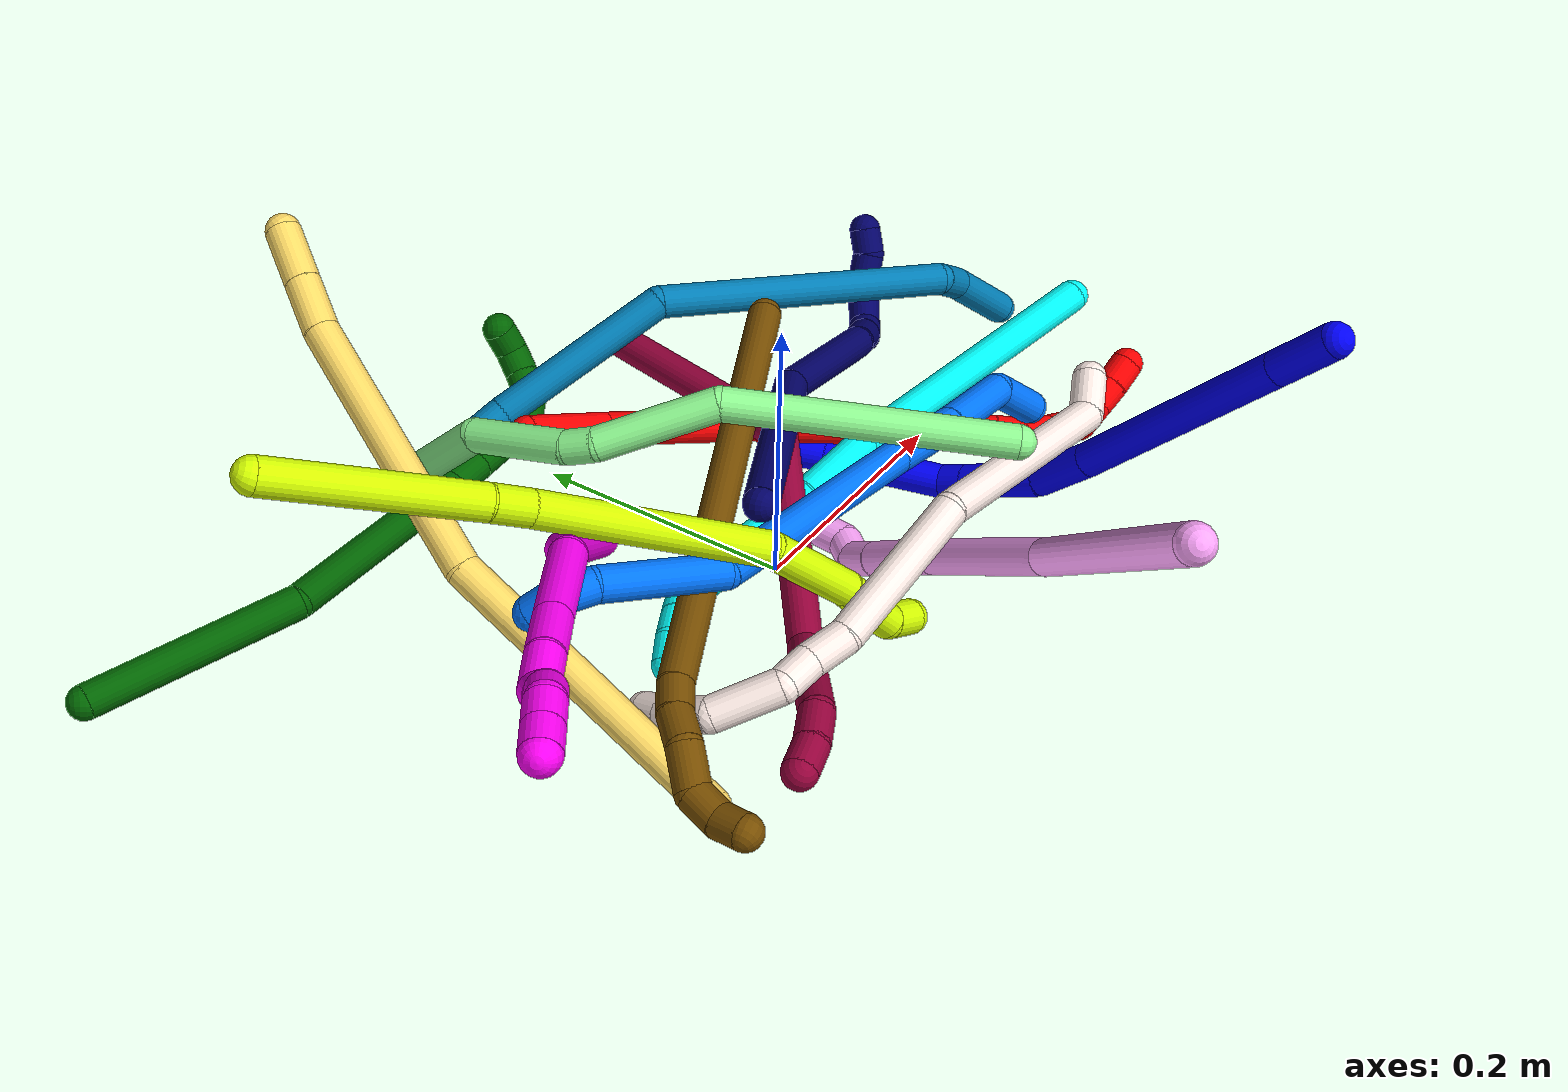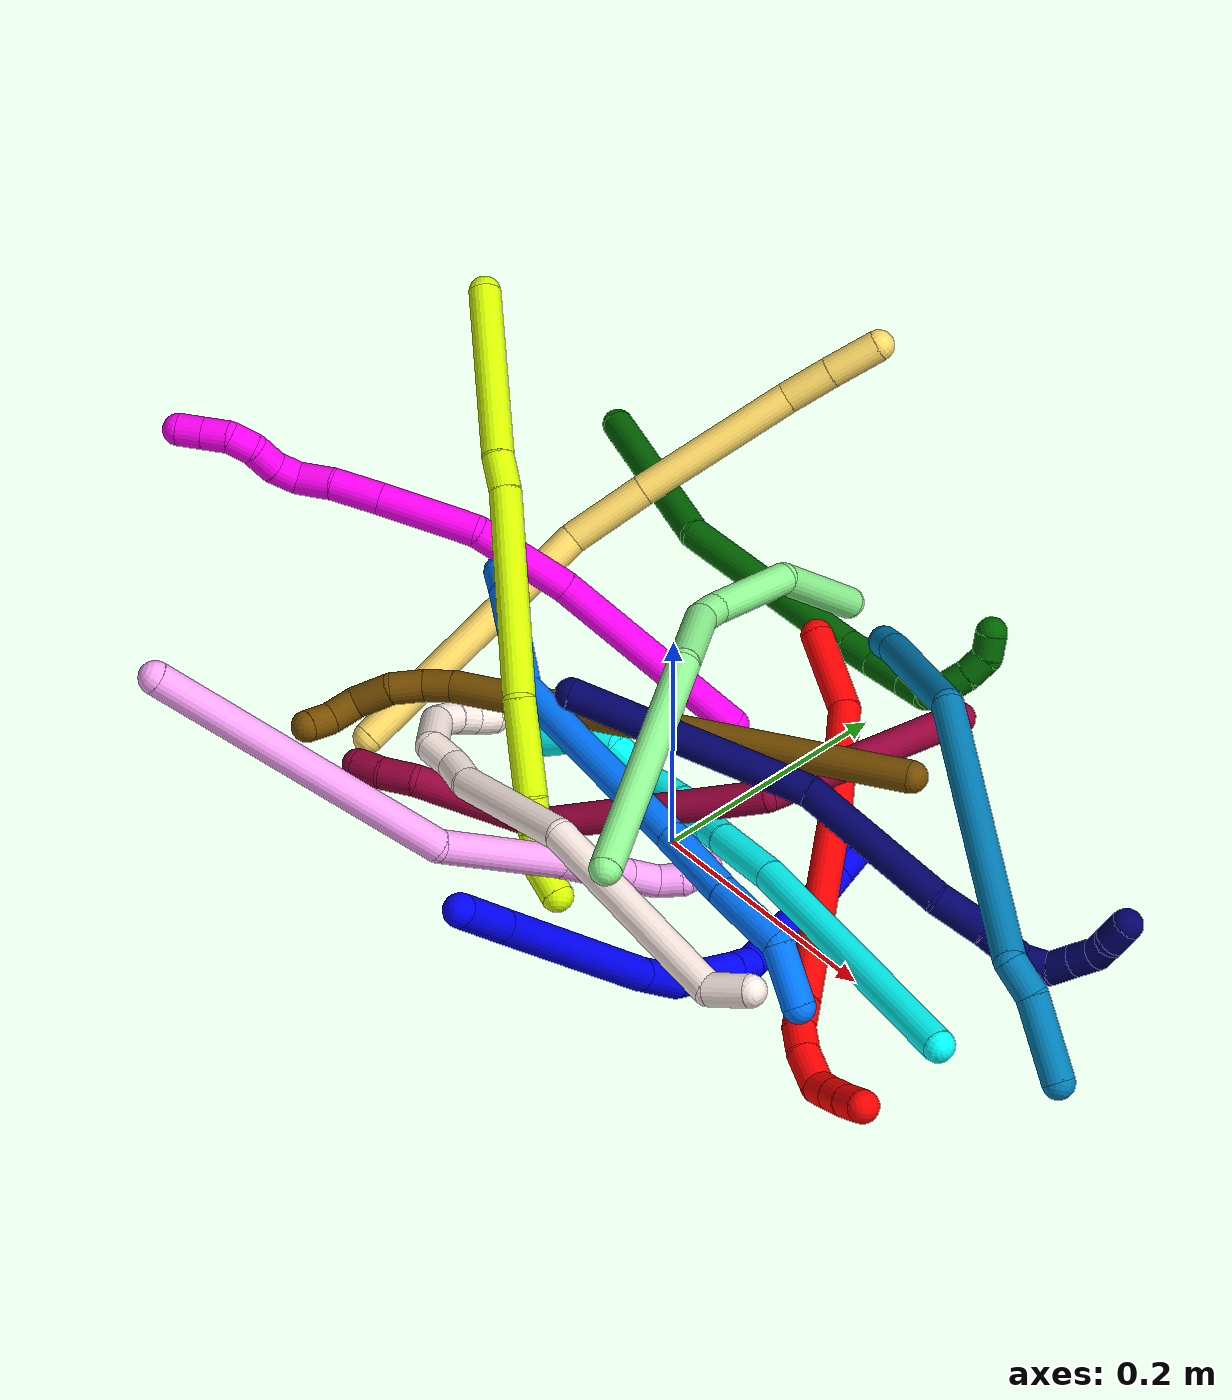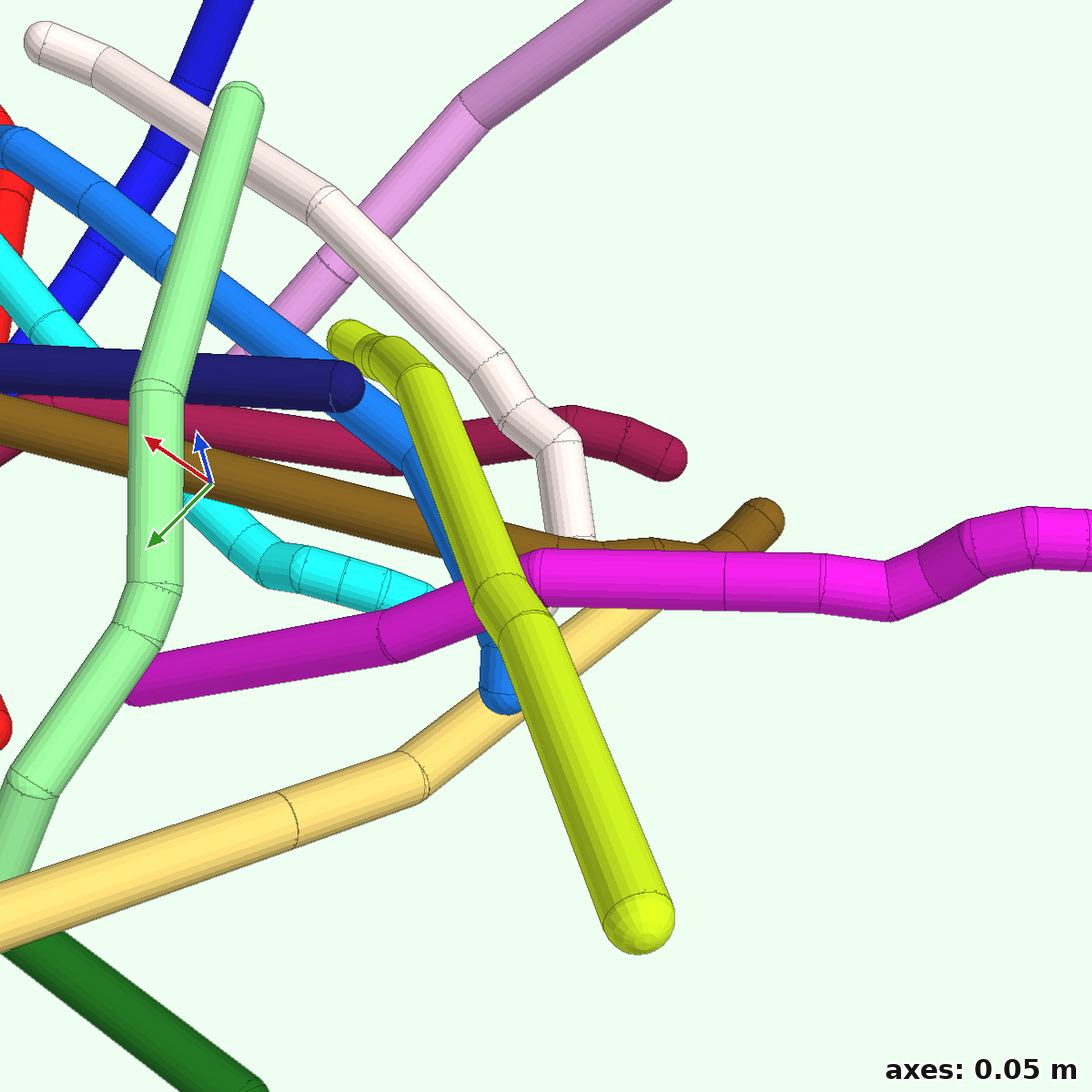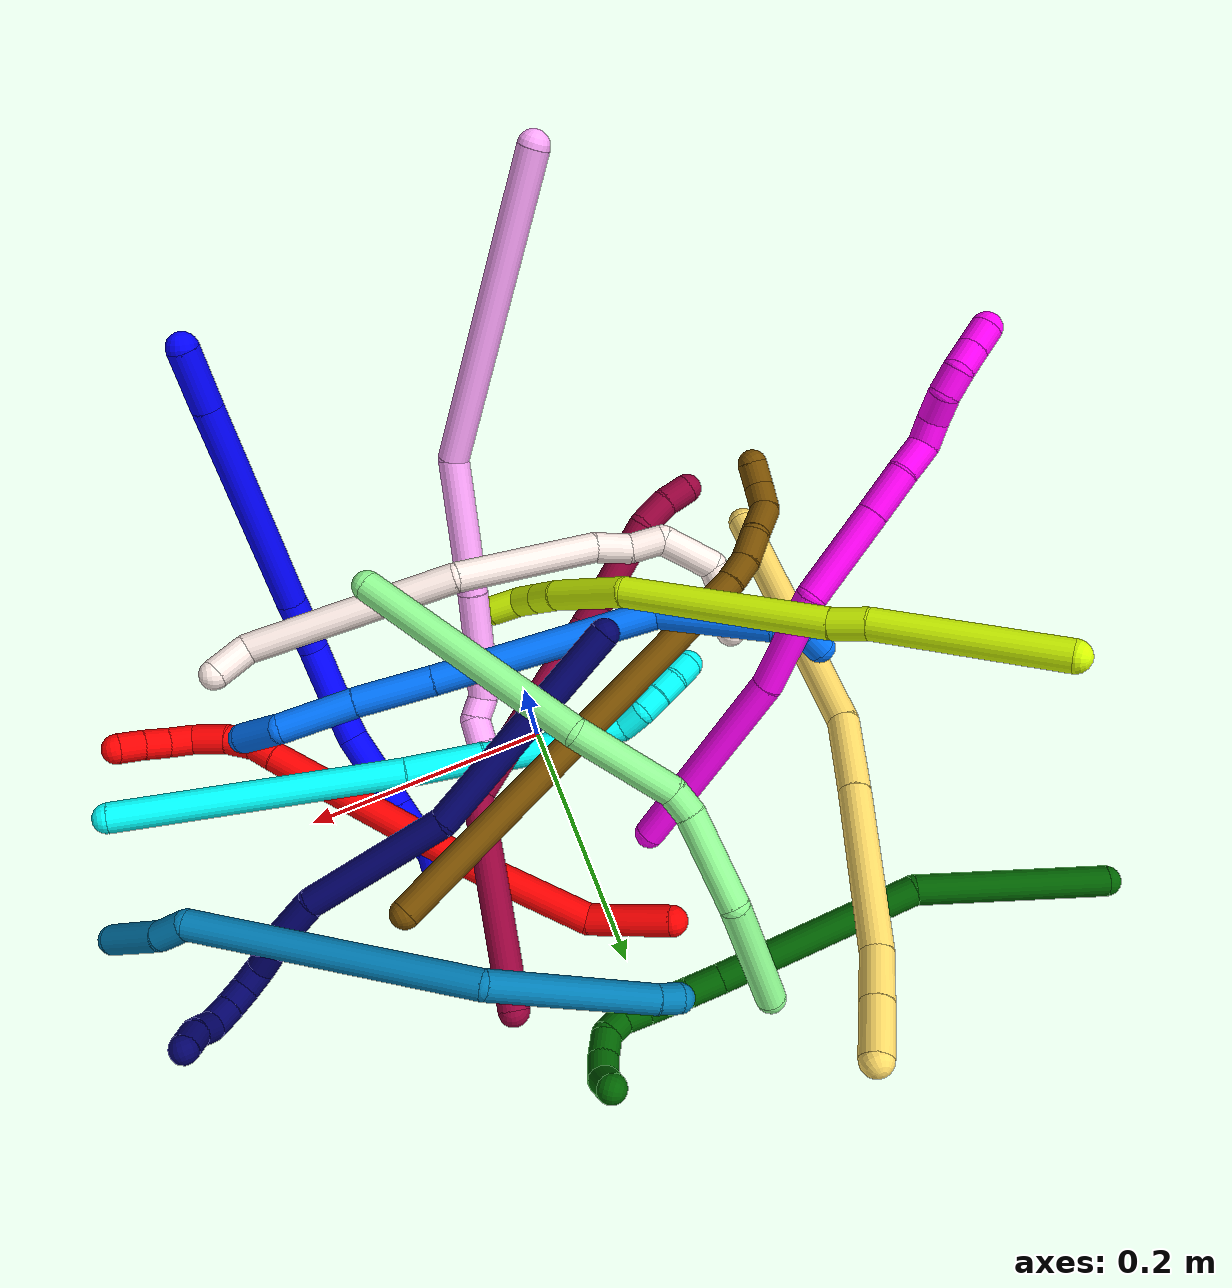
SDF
<sdf version="1.7">
 <world name="default">
  <plugin name="TubeGeneratorPlugin" filename="libtube_generator_plugin.so"/>
  <model name="photoneo_s_sensor">
   <static>1</static>
   <pose>0 0 2 1.57079 1.57079 3.14159</pose>
   <link name="link">
    <inertial><mass>0.1</mass></inertial>
    <sensor name="sensor" type="depth">
     <update_rate>30</update_rate>
     <camera>
      <horizontal_fov>1.22</horizontal_fov>
      <image><width>1920</width><height>1200</height><format>B8G8R8</format></image>
      <clip><near>0.1</near><far>4</far></clip>
      <depth_camera><output>points</output></depth_camera>
     </camera>
     <plugin name="camera_plugin" filename="libgazebo_ros_depth_camera.so">
      <baseline>0.2</baseline>
      <alwaysOn>1</alwaysOn>
      <updateRate>0.0</updateRate>
      <cameraName>camera_ir</cameraName>
      <imageTopicName>/camera/color/image_raw</imageTopicName>
      <cameraInfoTopicName>/camera/color/camera_info</cameraInfoTopicName>
      <depthImageTopicName>/camera/depth/image_raw</depthImageTopicName>
      <depthImageCameraInfoTopicName>/camera/depth/camera_info</depthImageCameraInfoTopicName>
      <pointCloudTopicName>/camera/depth/points</pointCloudTopicName>
      <frameName>fr_optical</frameName>
      <pointCloudCutoff>0.1</pointCloudCutoff>
      <pointCloudCutoffMax>2.0</pointCloudCutoffMax>
      <distortionK1>0</distortionK1>
      <distortionK2>0</distortionK2>
      <distortionK3>0</distortionK3>
      <distortionT1>0</distortionT1>
      <distortionT2>0</distortionT2>
      <CxPrime>0</CxPrime>
      <Cx>0</Cx>
      <Cy>0</Cy>
      <focalLength>0</focalLength>
      <hackBaseline>0</hackBaseline>
     </plugin>
    </sensor>
   </link>
  </model>
  <gravity>0 0 -9.8</gravity>
  <magnetic_field>6e-06 2.3e-05 -4.2e-05</magnetic_field>
  <atmosphere type="adiabatic"/>
  <physics name="default_physics" default="0" type="ode">
   <max_step_size>0.003</max_step_size>
   <real_time_factor>1</real_time_factor>
   <real_time_update_rate>1000</real_time_update_rate>
   <max_contacts>10000</max_contacts>
   <ode>
    <solver>
     <type>quick</type>
     <iters>100</iters>
     <sor>1.3</sor>
     <use_dynamic_moi_rescaling>0</use_dynamic_moi_rescaling>
    </solver>
    <constraints>
     <contact_max_correcting_vel>0</contact_max_correcting_vel>
     <contact_surface_layer>0.001</contact_surface_layer>
     <cfm>0</cfm>
     <erp>0.2</erp>
    </constraints>
   </ode>
  </physics>
  <scene><ambient>0.4 0.4 0.4 1</ambient><background>0.7 0.7 0.7 1</background><shadows>0</shadows></scene>
  <audio><device>default</device></audio>
  <spherical_coordinates>
   <surface_model>EARTH_WGS84</surface_model>
   <latitude_deg>0</latitude_deg>
   <longitude_deg>0</longitude_deg>
   <elevation>0</elevation>
   <heading_deg>0</heading_deg>
  </spherical_coordinates>
  <model name="bin">
   <static>1</static>
   <link name="bottom">
    <collision name="collision-bottom">
     <pose>0 0 -0.01 0 -0 0</pose>
     <geometry><box><size>0.8 0.6 0.02</size></box></geometry>
     <surface>
      <friction><ode><mu>100</mu><mu2>100</mu2></ode></friction>
      <contact><collide_bitmask>65535</collide_bitmask></contact>
     </surface>
    </collision>
   </link>
   <link name="west_wall">
    <collision name="collision-west_wall">
     <pose>-0.41 0 0.1 0 -0 0</pose>
     <geometry><box><size>0.02 0.6 0.2</size></box></geometry>
     <surface>
      <friction><ode><mu>100</mu><mu2>100</mu2></ode></friction>
      <contact><collide_bitmask>65535</collide_bitmask></contact>
     </surface>
    </collision>
   </link>
   <link name="east_wall">
    <collision name="collision-east_wall">
     <pose>0.41 0 0.1 0 -0 0</pose>
     <geometry><box><size>0.02 0.6 0.2</size></box></geometry>
     <surface>
      <friction><ode><mu>100</mu><mu2>100</mu2></ode></friction>
      <contact><collide_bitmask>65535</collide_bitmask></contact>
     </surface>
    </collision>
   </link>
   <link name="south_wall">
    <collision name="collision-south_wall">
     <pose>0 -0.31 0.1 0 -0 0</pose>
     <geometry><box><size>0.8 0.02 0.2</size></box></geometry>
     <surface>
      <friction><ode><mu>100</mu><mu2>100</mu2></ode></friction>
      <contact><collide_bitmask>65535</collide_bitmask></contact>
     </surface>
    </collision>
   </link>
   <link name="north_wall">
    <collision name="collision-north_wall">
     <pose>0 0.31 0.1 0 -0 0</pose>
     <geometry><box><size>0.8 0.02 0.2</size></box></geometry>
     <surface>
      <friction><ode><mu>100</mu><mu2>100</mu2></ode></friction>
      <contact><collide_bitmask>65535</collide_bitmask></contact>
     </surface>
    </collision>
   </link>
  </model>
  <model name="1">
   <static>0</static>
   <link name="1">
    <collision name="collision-cylinder-e_1_1_4">
     <pose>-0.006807 0.001019 -0.023368 -3.09799 -0.283187 2.83804</pose>
     <geometry><cylinder><radius>0.0125</radius><length>0.048721</length></cylinder></geometry>
     <surface>
      <friction><ode><mu>1.16</mu><mu2>1.16</mu2><slip1>0</slip1><slip2>0</slip2></ode></friction>
      <contact><ode><kp>1e+06</kp><kd>1</kd><max_vel>0</max_vel><min_depth>0.001</min_depth></ode></contact>
     </surface>
    </collision>
    <visual name="visual-cylinder-e_1_1_4">
     <pose>-0.006807 0.001019 -0.023368 -3.09799 -0.283187 2.83804</pose>
     <geometry><cylinder><radius>0.0125</radius><length>0.048721</length></cylinder></geometry>
     <material><ambient>0 0 1 1</ambient></material>
    </visual>
    <collision name="collision-cylinder-e_2_4_5">
     <pose>-0.038984 0.00664 -0.131739 -3.08752 -0.289648 2.7749</pose>
     <geometry><cylinder><radius>0.0125</radius><length>0.177655</length></cylinder></geometry>
     <surface>
      <friction><ode><mu>1.16</mu><mu2>1.16</mu2><slip1>0</slip1><slip2>0</slip2></ode></friction>
      <contact><ode><kp>1e+06</kp><kd>1</kd><max_vel>0</max_vel><min_depth>0.001</min_depth></ode></contact>
     </surface>
    </collision>
    <visual name="visual-cylinder-e_2_4_5">
     <pose>-0.038984 0.00664 -0.131739 -3.08752 -0.289648 2.7749</pose>
     <geometry><cylinder><radius>0.0125</radius><length>0.177655</length></cylinder></geometry>
     <material><ambient>0 0 1 1</ambient></material>
    </visual>
    <collision name="collision-cylinder-e_3_5_6">
     <pose>-0.07047 0.013985 -0.239317 -3.02064 -0.262702 2.28206</pose>
     <geometry><cylinder><radius>0.0125</radius><length>0.047098</length></cylinder></geometry>
     <surface>
      <friction><ode><mu>1.16</mu><mu2>1.16</mu2><slip1>0</slip1><slip2>0</slip2></ode></friction>
      <contact><ode><kp>1e+06</kp><kd>1</kd><max_vel>0</max_vel><min_depth>0.001</min_depth></ode></contact>
     </surface>
    </collision>
    <visual name="visual-cylinder-e_3_5_6">
     <pose>-0.07047 0.013985 -0.239317 -3.02064 -0.262702 2.28206</pose>
     <geometry><cylinder><radius>0.0125</radius><length>0.047098</length></cylinder></geometry>
     <material><ambient>0 0 1 1</ambient></material>
    </visual>
    <collision name="collision-cylinder-e_4_6_7">
     <pose>-0.077119 0.026643 -0.291394 -2.81739 -0.017132 0.104667</pose>
     <geometry><cylinder><radius>0.0125</radius><length>0.062255</length></cylinder></geometry>
     <surface>
      <friction><ode><mu>1.16</mu><mu2>1.16</mu2><slip1>0</slip1><slip2>0</slip2></ode></friction>
      <contact><ode><kp>1e+06</kp><kd>1</kd><max_vel>0</max_vel><min_depth>0.001</min_depth></ode></contact>
     </surface>
    </collision>
    <visual name="visual-cylinder-e_4_6_7">
     <pose>-0.077119 0.026643 -0.291394 -2.81739 -0.017132 0.104667</pose>
     <geometry><cylinder><radius>0.0125</radius><length>0.062255</length></cylinder></geometry>
     <material><ambient>0 0 1 1</ambient></material>
    </visual>
    <collision name="collision-cylinder-e_5_7_8">
     <pose>-0.077908 0.040352 -0.330504 -2.76549 -0.02479 0.130088</pose>
     <geometry><cylinder><radius>0.0125</radius><length>0.020668</length></cylinder></geometry>
     <surface>
      <friction><ode><mu>1.16</mu><mu2>1.16</mu2><slip1>0</slip1><slip2>0</slip2></ode></friction>
      <contact><ode><kp>1e+06</kp><kd>1</kd><max_vel>0</max_vel><min_depth>0.001</min_depth></ode></contact>
     </surface>
    </collision>
    <visual name="visual-cylinder-e_5_7_8">
     <pose>-0.077908 0.040352 -0.330504 -2.76549 -0.02479 0.130088</pose>
     <geometry><cylinder><radius>0.0125</radius><length>0.020668</length></cylinder></geometry>
     <material><ambient>0 0 1 1</ambient></material>
    </visual>
    <collision name="collision-cylinder-e_6_8_9">
     <pose>-0.072587 0.067849 -0.365858 -2.39749 0.158039 -0.4004</pose>
     <geometry><cylinder><radius>0.0125</radius><length>0.070873</length></cylinder></geometry>
     <surface>
      <friction><ode><mu>1.16</mu><mu2>1.16</mu2><slip1>0</slip1><slip2>0</slip2></ode></friction>
      <contact><ode><kp>1e+06</kp><kd>1</kd><max_vel>0</max_vel><min_depth>0.001</min_depth></ode></contact>
     </surface>
    </collision>
    <visual name="visual-cylinder-e_6_8_9">
     <pose>-0.072587 0.067849 -0.365858 -2.39749 0.158039 -0.4004</pose>
     <geometry><cylinder><radius>0.0125</radius><length>0.070873</length></cylinder></geometry>
     <material><ambient>0 0 1 1</ambient></material>
    </visual>
    <collision name="collision-cylinder-e_7_9_10">
     <pose>-0.065475 0.098316 -0.398965 -2.39833 0.152343 -0.386751</pose>
     <geometry><cylinder><radius>0.0125</radius><length>0.02023</length></cylinder></geometry>
     <surface>
      <friction><ode><mu>1.16</mu><mu2>1.16</mu2><slip1>0</slip1><slip2>0</slip2></ode></friction>
      <contact><ode><kp>1e+06</kp><kd>1</kd><max_vel>0</max_vel><min_depth>0.001</min_depth></ode></contact>
     </surface>
    </collision>
    <visual name="visual-cylinder-e_7_9_10">
     <pose>-0.065475 0.098316 -0.398965 -2.39833 0.152343 -0.386751</pose>
     <geometry><cylinder><radius>0.0125</radius><length>0.02023</length></cylinder></geometry>
     <material><ambient>0 0 1 1</ambient></material>
    </visual>
    <collision name="collision-cylinder-e_8_10_11">
     <pose>-0.062415 0.114844 -0.415464 -2.3232 0.113578 -0.260693</pose>
     <geometry><cylinder><radius>0.0125</radius><length>0.026917</length></cylinder></geometry>
     <surface>
      <friction><ode><mu>1.16</mu><mu2>1.16</mu2><slip1>0</slip1><slip2>0</slip2></ode></friction>
      <contact><ode><kp>1e+06</kp><kd>1</kd><max_vel>0</max_vel><min_depth>0.001</min_depth></ode></contact>
     </surface>
    </collision>
    <visual name="visual-cylinder-e_8_10_11">
     <pose>-0.062415 0.114844 -0.415464 -2.3232 0.113578 -0.260693</pose>
     <geometry><cylinder><radius>0.0125</radius><length>0.026917</length></cylinder></geometry>
     <material><ambient>0 0 1 1</ambient></material>
    </visual>
    <collision name="collision-cylinder-e_9_11_2">
     <pose>-0.052453 0.132928 -0.429419 -2.09543 0.72025 -1.15693</pose>
     <geometry><cylinder><radius>0.0125</radius><length>0.025582</length></cylinder></geometry>
     <surface>
      <friction><ode><mu>1.16</mu><mu2>1.16</mu2><slip1>0</slip1><slip2>0</slip2></ode></friction>
      <contact><ode><kp>1e+06</kp><kd>1</kd><max_vel>0</max_vel><min_depth>0.001</min_depth></ode></contact>
     </surface>
    </collision>
    <visual name="visual-cylinder-e_9_11_2">
     <pose>-0.052453 0.132928 -0.429419 -2.09543 0.72025 -1.15693</pose>
     <geometry><cylinder><radius>0.0125</radius><length>0.025582</length></cylinder></geometry>
     <material><ambient>0 0 1 1</ambient></material>
    </visual>
    <collision name="collision-sphere-2">
     <pose>-0.044016 0.141249 -0.434234 0 -0 0</pose>
     <geometry><sphere><radius>0.0125</radius></sphere></geometry>
     <surface>
      <friction><ode><mu>1.16</mu><mu2>1.16</mu2><slip1>0</slip1><slip2>0</slip2></ode></friction>
      <contact><ode><kp>1e+06</kp><kd>1</kd><max_vel>0</max_vel><min_depth>0.001</min_depth></ode></contact>
     </surface>
    </collision>
    <visual name="visual-sphere-2">
     <pose>-0.044016 0.141249 -0.434234 0 -0 0</pose>
     <geometry><sphere><radius>0.0125</radius></sphere></geometry>
     <material><ambient>0 0 1 1</ambient></material>
    </visual>
    <collision name="collision-sphere-11">
     <pose>-0.060889 0.124606 -0.424603 0 -0 0</pose>
     <geometry><sphere><radius>0.0125</radius></sphere></geometry>
     <surface>
      <friction><ode><mu>1.16</mu><mu2>1.16</mu2><slip1>0</slip1><slip2>0</slip2></ode></friction>
      <contact><ode><kp>1e+06</kp><kd>1</kd><max_vel>0</max_vel><min_depth>0.001</min_depth></ode></contact>
     </surface>
    </collision>
    <visual name="visual-sphere-11">
     <pose>-0.060889 0.124606 -0.424603 0 -0 0</pose>
     <geometry><sphere><radius>0.0125</radius></sphere></geometry>
     <material><ambient>0 0 1 1</ambient></material>
    </visual>
    <collision name="collision-sphere-10">
     <pose>-0.06394 0.105082 -0.406326 0 -0 0</pose>
     <geometry><sphere><radius>0.0125</radius></sphere></geometry>
     <surface>
      <friction><ode><mu>1.16</mu><mu2>1.16</mu2><slip1>0</slip1><slip2>0</slip2></ode></friction>
      <contact><ode><kp>1e+06</kp><kd>1</kd><max_vel>0</max_vel><min_depth>0.001</min_depth></ode></contact>
     </surface>
    </collision>
    <visual name="visual-sphere-10">
     <pose>-0.06394 0.105082 -0.406326 0 -0 0</pose>
     <geometry><sphere><radius>0.0125</radius></sphere></geometry>
     <material><ambient>0 0 1 1</ambient></material>
    </visual>
    <collision name="collision-sphere-9">
     <pose>-0.06701 0.091551 -0.391604 0 -0 0</pose>
     <geometry><sphere><radius>0.0125</radius></sphere></geometry>
     <surface>
      <friction><ode><mu>1.16</mu><mu2>1.16</mu2><slip1>0</slip1><slip2>0</slip2></ode></friction>
      <contact><ode><kp>1e+06</kp><kd>1</kd><max_vel>0</max_vel><min_depth>0.001</min_depth></ode></contact>
     </surface>
    </collision>
    <visual name="visual-sphere-9">
     <pose>-0.06701 0.091551 -0.391604 0 -0 0</pose>
     <geometry><sphere><radius>0.0125</radius></sphere></geometry>
     <material><ambient>0 0 1 1</ambient></material>
    </visual>
    <collision name="collision-sphere-4">
     <pose>-0.013614 0.002039 -0.046736 0 -0 0</pose>
     <geometry><sphere><radius>0.0125</radius></sphere></geometry>
     <surface>
      <friction><ode><mu>1.16</mu><mu2>1.16</mu2><slip1>0</slip1><slip2>0</slip2></ode></friction>
      <contact><ode><kp>1e+06</kp><kd>1</kd><max_vel>0</max_vel><min_depth>0.001</min_depth></ode></contact>
     </surface>
    </collision>
    <visual name="visual-sphere-4">
     <pose>-0.013614 0.002039 -0.046736 0 -0 0</pose>
     <geometry><sphere><radius>0.0125</radius></sphere></geometry>
     <material><ambient>0 0 1 1</ambient></material>
    </visual>
    <collision name="collision-sphere-1">
     <geometry><sphere><radius>0.0125</radius></sphere></geometry>
     <surface>
      <friction><ode><mu>1.16</mu><mu2>1.16</mu2><slip1>0</slip1><slip2>0</slip2></ode></friction>
      <contact><ode><kp>1e+06</kp><kd>1</kd><max_vel>0</max_vel><min_depth>0.001</min_depth></ode></contact>
     </surface>
    </collision>
    <visual name="visual-sphere-1">
     <geometry><sphere><radius>0.0125</radius></sphere></geometry>
     <material><ambient>0 0 1 1</ambient></material>
    </visual>
    <collision name="collision-sphere-8">
     <pose>-0.078164 0.044146 -0.340113 0 -0 0</pose>
     <geometry><sphere><radius>0.0125</radius></sphere></geometry>
     <surface>
      <friction><ode><mu>1.16</mu><mu2>1.16</mu2><slip1>0</slip1><slip2>0</slip2></ode></friction>
      <contact><ode><kp>1e+06</kp><kd>1</kd><max_vel>0</max_vel><min_depth>0.001</min_depth></ode></contact>
     </surface>
    </collision>
    <visual name="visual-sphere-8">
     <pose>-0.078164 0.044146 -0.340113 0 -0 0</pose>
     <geometry><sphere><radius>0.0125</radius></sphere></geometry>
     <material><ambient>0 0 1 1</ambient></material>
    </visual>
    <collision name="collision-sphere-5">
     <pose>-0.064354 0.011241 -0.216742 0 -0 0</pose>
     <geometry><sphere><radius>0.0125</radius></sphere></geometry>
     <surface>
      <friction><ode><mu>1.16</mu><mu2>1.16</mu2><slip1>0</slip1><slip2>0</slip2></ode></friction>
      <contact><ode><kp>1e+06</kp><kd>1</kd><max_vel>0</max_vel><min_depth>0.001</min_depth></ode></contact>
     </surface>
    </collision>
    <visual name="visual-sphere-5">
     <pose>-0.064354 0.011241 -0.216742 0 -0 0</pose>
     <geometry><sphere><radius>0.0125</radius></sphere></geometry>
     <material><ambient>0 0 1 1</ambient></material>
    </visual>
    <collision name="collision-sphere-6">
     <pose>-0.076585 0.016729 -0.261892 0 -0 0</pose>
     <geometry><sphere><radius>0.0125</radius></sphere></geometry>
     <surface>
      <friction><ode><mu>1.16</mu><mu2>1.16</mu2><slip1>0</slip1><slip2>0</slip2></ode></friction>
      <contact><ode><kp>1e+06</kp><kd>1</kd><max_vel>0</max_vel><min_depth>0.001</min_depth></ode></contact>
     </surface>
    </collision>
    <visual name="visual-sphere-6">
     <pose>-0.076585 0.016729 -0.261892 0 -0 0</pose>
     <geometry><sphere><radius>0.0125</radius></sphere></geometry>
     <material><ambient>0 0 1 1</ambient></material>
    </visual>
    <collision name="collision-sphere-7">
     <pose>-0.077652 0.036557 -0.320895 0 -0 0</pose>
     <geometry><sphere><radius>0.0125</radius></sphere></geometry>
     <surface>
      <friction><ode><mu>1.16</mu><mu2>1.16</mu2><slip1>0</slip1><slip2>0</slip2></ode></friction>
      <contact><ode><kp>1e+06</kp><kd>1</kd><max_vel>0</max_vel><min_depth>0.001</min_depth></ode></contact>
     </surface>
    </collision>
    <visual name="visual-sphere-7">
     <pose>-0.077652 0.036557 -0.320895 0 -0 0</pose>
     <geometry><sphere><radius>0.0125</radius></sphere></geometry>
     <material><ambient>0 0 1 1</ambient></material>
    </visual>
    <inertial>
     <pose>-0.052957 0.03534 -0.23391 0 -0 0</pose>
     <mass>0.5</mass>
     <inertia><ixx>-0.000226</ixx><ixy>0</ixy><ixz>0</ixz><iyy>0.00059</iyy><iyz>0</iyz><izz>4e-05</izz></inertia>
    </inertial>
   </link>
   <pose>0.14049 -0.321843 0.238821 0.642828 -0.808695 0.463553</pose>
  </model>
  <model name="2">
   <static>0</static>
   <link name="2">
    <collision name="collision-cylinder-e_1_1_4">
     <pose>0.008838 -0.032832 -0.002916 1.65939 0.261982 0.285967</pose>
     <geometry><cylinder><radius>0.0125</radius><length>0.068251</length></cylinder></geometry>
     <surface>
      <friction><ode><mu>1.16</mu><mu2>1.16</mu2><slip1>0</slip1><slip2>0</slip2></ode></friction>
      <contact><ode><kp>1e+06</kp><kd>1</kd><max_vel>0</max_vel><min_depth>0.001</min_depth></ode></contact>
     </surface>
    </collision>
    <visual name="visual-cylinder-e_1_1_4">
     <pose>0.008838 -0.032832 -0.002916 1.65939 0.261982 0.285967</pose>
     <geometry><cylinder><radius>0.0125</radius><length>0.068251</length></cylinder></geometry>
     <material><ambient>1 0 0 1</ambient></material>
    </visual>
    <collision name="collision-cylinder-e_2_4_5">
     <pose>0.02705 -0.11004 -0.033292 2.12493 0.177726 0.317135</pose>
     <geometry><cylinder><radius>0.0125</radius><length>0.106041</length></cylinder></geometry>
     <surface>
      <friction><ode><mu>1.16</mu><mu2>1.16</mu2><slip1>0</slip1><slip2>0</slip2></ode></friction>
      <contact><ode><kp>1e+06</kp><kd>1</kd><max_vel>0</max_vel><min_depth>0.001</min_depth></ode></contact>
     </surface>
    </collision>
    <visual name="visual-cylinder-e_2_4_5">
     <pose>0.02705 -0.11004 -0.033292 2.12493 0.177726 0.317135</pose>
     <geometry><cylinder><radius>0.0125</radius><length>0.106041</length></cylinder></geometry>
     <material><ambient>1 0 0 1</ambient></material>
    </visual>
    <collision name="collision-cylinder-e_3_5_6">
     <pose>0.056845 -0.229524 -0.112738 2.17623 0.219947 0.415352</pose>
     <geometry><cylinder><radius>0.0125</radius><length>0.187197</length></cylinder></geometry>
     <surface>
      <friction><ode><mu>1.16</mu><mu2>1.16</mu2><slip1>0</slip1><slip2>0</slip2></ode></friction>
      <contact><ode><kp>1e+06</kp><kd>1</kd><max_vel>0</max_vel><min_depth>0.001</min_depth></ode></contact>
     </surface>
    </collision>
    <visual name="visual-cylinder-e_3_5_6">
     <pose>0.056845 -0.229524 -0.112738 2.17623 0.219947 0.415352</pose>
     <geometry><cylinder><radius>0.0125</radius><length>0.187197</length></cylinder></geometry>
     <material><ambient>1 0 0 1</ambient></material>
    </visual>
    <collision name="collision-cylinder-e_4_6_7">
     <pose>0.080446 -0.313109 -0.17065 2.18091 0.298237 0.561432</pose>
     <geometry><cylinder><radius>0.0125</radius><length>0.021641</length></cylinder></geometry>
     <surface>
      <friction><ode><mu>1.16</mu><mu2>1.16</mu2><slip1>0</slip1><slip2>0</slip2></ode></friction>
      <contact><ode><kp>1e+06</kp><kd>1</kd><max_vel>0</max_vel><min_depth>0.001</min_depth></ode></contact>
     </surface>
    </collision>
    <visual name="visual-cylinder-e_4_6_7">
     <pose>0.080446 -0.313109 -0.17065 2.18091 0.298237 0.561432</pose>
     <geometry><cylinder><radius>0.0125</radius><length>0.021641</length></cylinder></geometry>
     <material><ambient>1 0 0 1</ambient></material>
    </visual>
    <collision name="collision-cylinder-e_5_7_8">
     <pose>0.08543 -0.332564 -0.180397 1.90577 0.154053 0.216326</pose>
     <geometry><cylinder><radius>0.0125</radius><length>0.023528</length></cylinder></geometry>
     <surface>
      <friction><ode><mu>1.16</mu><mu2>1.16</mu2><slip1>0</slip1><slip2>0</slip2></ode></friction>
      <contact><ode><kp>1e+06</kp><kd>1</kd><max_vel>0</max_vel><min_depth>0.001</min_depth></ode></contact>
     </surface>
    </collision>
    <visual name="visual-cylinder-e_5_7_8">
     <pose>0.08543 -0.332564 -0.180397 1.90577 0.154053 0.216326</pose>
     <geometry><cylinder><radius>0.0125</radius><length>0.023528</length></cylinder></geometry>
     <material><ambient>1 0 0 1</ambient></material>
    </visual>
    <collision name="collision-cylinder-e_6_8_9">
     <pose>0.088967 -0.358737 -0.186209 1.70102 0.112509 0.128164</pose>
     <geometry><cylinder><radius>0.0125</radius><length>0.030844</length></cylinder></geometry>
     <surface>
      <friction><ode><mu>1.16</mu><mu2>1.16</mu2><slip1>0</slip1><slip2>0</slip2></ode></friction>
      <contact><ode><kp>1e+06</kp><kd>1</kd><max_vel>0</max_vel><min_depth>0.001</min_depth></ode></contact>
     </surface>
    </collision>
    <visual name="visual-cylinder-e_6_8_9">
     <pose>0.088967 -0.358737 -0.186209 1.70102 0.112509 0.128164</pose>
     <geometry><cylinder><radius>0.0125</radius><length>0.030844</length></cylinder></geometry>
     <material><ambient>1 0 0 1</ambient></material>
    </visual>
    <collision name="collision-cylinder-e_7_9_10">
     <pose>0.085577 -0.382827 -0.189351 1.69961 -0.518833 -0.586566</pose>
     <geometry><cylinder><radius>0.0125</radius><length>0.020656</length></cylinder></geometry>
     <surface>
      <friction><ode><mu>1.16</mu><mu2>1.16</mu2><slip1>0</slip1><slip2>0</slip2></ode></friction>
      <contact><ode><kp>1e+06</kp><kd>1</kd><max_vel>0</max_vel><min_depth>0.001</min_depth></ode></contact>
     </surface>
    </collision>
    <visual name="visual-cylinder-e_7_9_10">
     <pose>0.085577 -0.382827 -0.189351 1.69961 -0.518833 -0.586566</pose>
     <geometry><cylinder><radius>0.0125</radius><length>0.020656</length></cylinder></geometry>
     <material><ambient>1 0 0 1</ambient></material>
    </visual>
    <collision name="collision-cylinder-e_8_10_11">
     <pose>0.075076 -0.400347 -0.192102 1.7541 -0.55012 -0.654292</pose>
     <geometry><cylinder><radius>0.0125</radius><length>0.020582</length></cylinder></geometry>
     <surface>
      <friction><ode><mu>1.16</mu><mu2>1.16</mu2><slip1>0</slip1><slip2>0</slip2></ode></friction>
      <contact><ode><kp>1e+06</kp><kd>1</kd><max_vel>0</max_vel><min_depth>0.001</min_depth></ode></contact>
     </surface>
    </collision>
    <visual name="visual-cylinder-e_8_10_11">
     <pose>0.075076 -0.400347 -0.192102 1.7541 -0.55012 -0.654292</pose>
     <geometry><cylinder><radius>0.0125</radius><length>0.020582</length></cylinder></geometry>
     <material><ambient>1 0 0 1</ambient></material>
    </visual>
    <collision name="collision-cylinder-e_9_11_2">
     <pose>0.063657 -0.417654 -0.194781 1.6946 -0.604109 -0.678272</pose>
     <geometry><cylinder><radius>0.0125</radius><length>0.02126</length></cylinder></geometry>
     <surface>
      <friction><ode><mu>1.16</mu><mu2>1.16</mu2><slip1>0</slip1><slip2>0</slip2></ode></friction>
      <contact><ode><kp>1e+06</kp><kd>1</kd><max_vel>0</max_vel><min_depth>0.001</min_depth></ode></contact>
     </surface>
    </collision>
    <visual name="visual-cylinder-e_9_11_2">
     <pose>0.063657 -0.417654 -0.194781 1.6946 -0.604109 -0.678272</pose>
     <geometry><cylinder><radius>0.0125</radius><length>0.02126</length></cylinder></geometry>
     <material><ambient>1 0 0 1</ambient></material>
    </visual>
    <collision name="collision-sphere-2">
     <pose>0.057619 -0.426336 -0.195862 0 -0 0</pose>
     <geometry><sphere><radius>0.0125</radius></sphere></geometry>
     <surface>
      <friction><ode><mu>1.16</mu><mu2>1.16</mu2><slip1>0</slip1><slip2>0</slip2></ode></friction>
      <contact><ode><kp>1e+06</kp><kd>1</kd><max_vel>0</max_vel><min_depth>0.001</min_depth></ode></contact>
     </surface>
    </collision>
    <visual name="visual-sphere-2">
     <pose>0.057619 -0.426336 -0.195862 0 -0 0</pose>
     <geometry><sphere><radius>0.0125</radius></sphere></geometry>
     <material><ambient>1 0 0 1</ambient></material>
    </visual>
    <collision name="collision-sphere-11">
     <pose>0.069696 -0.408972 -0.193701 0 -0 0</pose>
     <geometry><sphere><radius>0.0125</radius></sphere></geometry>
     <surface>
      <friction><ode><mu>1.16</mu><mu2>1.16</mu2><slip1>0</slip1><slip2>0</slip2></ode></friction>
      <contact><ode><kp>1e+06</kp><kd>1</kd><max_vel>0</max_vel><min_depth>0.001</min_depth></ode></contact>
     </surface>
    </collision>
    <visual name="visual-sphere-11">
     <pose>0.069696 -0.408972 -0.193701 0 -0 0</pose>
     <geometry><sphere><radius>0.0125</radius></sphere></geometry>
     <material><ambient>1 0 0 1</ambient></material>
    </visual>
    <collision name="collision-sphere-10">
     <pose>0.080455 -0.391721 -0.190503 0 -0 0</pose>
     <geometry><sphere><radius>0.0125</radius></sphere></geometry>
     <surface>
      <friction><ode><mu>1.16</mu><mu2>1.16</mu2><slip1>0</slip1><slip2>0</slip2></ode></friction>
      <contact><ode><kp>1e+06</kp><kd>1</kd><max_vel>0</max_vel><min_depth>0.001</min_depth></ode></contact>
     </surface>
    </collision>
    <visual name="visual-sphere-10">
     <pose>0.080455 -0.391721 -0.190503 0 -0 0</pose>
     <geometry><sphere><radius>0.0125</radius></sphere></geometry>
     <material><ambient>1 0 0 1</ambient></material>
    </visual>
    <collision name="collision-sphere-9">
     <pose>0.090698 -0.373932 -0.188199 0 -0 0</pose>
     <geometry><sphere><radius>0.0125</radius></sphere></geometry>
     <surface>
      <friction><ode><mu>1.16</mu><mu2>1.16</mu2><slip1>0</slip1><slip2>0</slip2></ode></friction>
      <contact><ode><kp>1e+06</kp><kd>1</kd><max_vel>0</max_vel><min_depth>0.001</min_depth></ode></contact>
     </surface>
    </collision>
    <visual name="visual-sphere-9">
     <pose>0.090698 -0.373932 -0.188199 0 -0 0</pose>
     <geometry><sphere><radius>0.0125</radius></sphere></geometry>
     <material><ambient>1 0 0 1</ambient></material>
    </visual>
    <collision name="collision-sphere-4">
     <pose>0.017677 -0.065664 -0.005832 0 -0 0</pose>
     <geometry><sphere><radius>0.0125</radius></sphere></geometry>
     <surface>
      <friction><ode><mu>1.16</mu><mu2>1.16</mu2><slip1>0</slip1><slip2>0</slip2></ode></friction>
      <contact><ode><kp>1e+06</kp><kd>1</kd><max_vel>0</max_vel><min_depth>0.001</min_depth></ode></contact>
     </surface>
    </collision>
    <visual name="visual-sphere-4">
     <pose>0.017677 -0.065664 -0.005832 0 -0 0</pose>
     <geometry><sphere><radius>0.0125</radius></sphere></geometry>
     <material><ambient>1 0 0 1</ambient></material>
    </visual>
    <collision name="collision-sphere-1">
     <geometry><sphere><radius>0.0125</radius></sphere></geometry>
     <surface>
      <friction><ode><mu>1.16</mu><mu2>1.16</mu2><slip1>0</slip1><slip2>0</slip2></ode></friction>
      <contact><ode><kp>1e+06</kp><kd>1</kd><max_vel>0</max_vel><min_depth>0.001</min_depth></ode></contact>
     </surface>
    </collision>
    <visual name="visual-sphere-1">
     <geometry><sphere><radius>0.0125</radius></sphere></geometry>
     <material><ambient>1 0 0 1</ambient></material>
    </visual>
    <collision name="collision-sphere-8">
     <pose>0.087235 -0.343543 -0.184219 0 -0 0</pose>
     <geometry><sphere><radius>0.0125</radius></sphere></geometry>
     <surface>
      <friction><ode><mu>1.16</mu><mu2>1.16</mu2><slip1>0</slip1><slip2>0</slip2></ode></friction>
      <contact><ode><kp>1e+06</kp><kd>1</kd><max_vel>0</max_vel><min_depth>0.001</min_depth></ode></contact>
     </surface>
    </collision>
    <visual name="visual-sphere-8">
     <pose>0.087235 -0.343543 -0.184219 0 -0 0</pose>
     <geometry><sphere><radius>0.0125</radius></sphere></geometry>
     <material><ambient>1 0 0 1</ambient></material>
    </visual>
    <collision name="collision-sphere-5">
     <pose>0.036424 -0.154416 -0.060753 0 -0 0</pose>
     <geometry><sphere><radius>0.0125</radius></sphere></geometry>
     <surface>
      <friction><ode><mu>1.16</mu><mu2>1.16</mu2><slip1>0</slip1><slip2>0</slip2></ode></friction>
      <contact><ode><kp>1e+06</kp><kd>1</kd><max_vel>0</max_vel><min_depth>0.001</min_depth></ode></contact>
     </surface>
    </collision>
    <visual name="visual-sphere-5">
     <pose>0.036424 -0.154416 -0.060753 0 -0 0</pose>
     <geometry><sphere><radius>0.0125</radius></sphere></geometry>
     <material><ambient>1 0 0 1</ambient></material>
    </visual>
    <collision name="collision-sphere-6">
     <pose>0.077266 -0.304632 -0.164724 0 -0 0</pose>
     <geometry><sphere><radius>0.0125</radius></sphere></geometry>
     <surface>
      <friction><ode><mu>1.16</mu><mu2>1.16</mu2><slip1>0</slip1><slip2>0</slip2></ode></friction>
      <contact><ode><kp>1e+06</kp><kd>1</kd><max_vel>0</max_vel><min_depth>0.001</min_depth></ode></contact>
     </surface>
    </collision>
    <visual name="visual-sphere-6">
     <pose>0.077266 -0.304632 -0.164724 0 -0 0</pose>
     <geometry><sphere><radius>0.0125</radius></sphere></geometry>
     <material><ambient>1 0 0 1</ambient></material>
    </visual>
    <collision name="collision-sphere-7">
     <pose>0.083625 -0.321585 -0.176575 0 -0 0</pose>
     <geometry><sphere><radius>0.0125</radius></sphere></geometry>
     <surface>
      <friction><ode><mu>1.16</mu><mu2>1.16</mu2><slip1>0</slip1><slip2>0</slip2></ode></friction>
      <contact><ode><kp>1e+06</kp><kd>1</kd><max_vel>0</max_vel><min_depth>0.001</min_depth></ode></contact>
     </surface>
    </collision>
    <visual name="visual-sphere-7">
     <pose>0.083625 -0.321585 -0.176575 0 -0 0</pose>
     <geometry><sphere><radius>0.0125</radius></sphere></geometry>
     <material><ambient>1 0 0 1</ambient></material>
    </visual>
    <inertial>
     <pose>0.050548 -0.215136 -0.101041 0 -0 0</pose>
     <mass>0.5</mass>
     <inertia>
      <ixx>0.00089</ixx>
      <ixy>0</ixy>
      <ixz>0</ixz>
      <iyy>-7.2e-05</iyy>
      <iyz>0</iyz>
      <izz>0.000409</izz>
     </inertia>
    </inertial>
   </link>
   <pose>-0.043234 0.187113 0.069082 2.86828 1.2116 -2.06179</pose>
  </model>
  <model name="3">
   <static>0</static>
   <link name="3">
    <collision name="collision-cylinder-e_1_1_4">
     <pose>0 0.010855 -0.11625 -3.04848 1e-06 -2.3e-05</pose>
     <geometry><cylinder><radius>0.0125</radius><length>0.233511</length></cylinder></geometry>
     <surface>
      <friction><ode><mu>1.16</mu><mu2>1.16</mu2><slip1>0</slip1><slip2>0</slip2></ode></friction>
      <contact><ode><kp>1e+06</kp><kd>1</kd><max_vel>0</max_vel><min_depth>0.001</min_depth></ode></contact>
     </surface>
    </collision>
    <visual name="visual-cylinder-e_1_1_4">
     <pose>0 0.010855 -0.11625 -3.04848 1e-06 -2.3e-05</pose>
     <geometry><cylinder><radius>0.0125</radius><length>0.233511</length></cylinder></geometry>
     <material><ambient>0.003922 1 0.996078 1</ambient></material>
    </visual>
    <collision name="collision-cylinder-e_2_4_5">
     <pose>-0.000985 0.021654 -0.264346 3.13983 -0.030936 -3.02752</pose>
     <geometry><cylinder><radius>0.0125</radius><length>0.063725</length></cylinder></geometry>
     <surface>
      <friction><ode><mu>1.16</mu><mu2>1.16</mu2><slip1>0</slip1><slip2>0</slip2></ode></friction>
      <contact><ode><kp>1e+06</kp><kd>1</kd><max_vel>0</max_vel><min_depth>0.001</min_depth></ode></contact>
     </surface>
    </collision>
    <visual name="visual-cylinder-e_2_4_5">
     <pose>-0.000985 0.021654 -0.264346 3.13983 -0.030936 -3.02752</pose>
     <geometry><cylinder><radius>0.0125</radius><length>0.063725</length></cylinder></geometry>
     <material><ambient>0.003922 1 0.996078 1</ambient></material>
    </visual>
    <collision name="collision-cylinder-e_3_5_6">
     <pose>-0.00097 0.020806 -0.307124 3.06933 0.091051 1.8001</pose>
     <geometry><cylinder><radius>0.0125</radius><length>0.02201</length></cylinder></geometry>
     <surface>
      <friction><ode><mu>1.16</mu><mu2>1.16</mu2><slip1>0</slip1><slip2>0</slip2></ode></friction>
      <contact><ode><kp>1e+06</kp><kd>1</kd><max_vel>0</max_vel><min_depth>0.001</min_depth></ode></contact>
     </surface>
    </collision>
    <visual name="visual-cylinder-e_3_5_6">
     <pose>-0.00097 0.020806 -0.307124 3.06933 0.091051 1.8001</pose>
     <geometry><cylinder><radius>0.0125</radius><length>0.02201</length></cylinder></geometry>
     <material><ambient>0.003922 1 0.996078 1</ambient></material>
    </visual>
    <collision name="collision-cylinder-e_4_6_7">
     <pose>-0.000843 0.02189 -0.338803 -3.05145 -0.041914 0.870064</pose>
     <geometry><cylinder><radius>0.0125</radius><length>0.0417</length></cylinder></geometry>
     <surface>
      <friction><ode><mu>1.16</mu><mu2>1.16</mu2><slip1>0</slip1><slip2>0</slip2></ode></friction>
      <contact><ode><kp>1e+06</kp><kd>1</kd><max_vel>0</max_vel><min_depth>0.001</min_depth></ode></contact>
     </surface>
    </collision>
    <visual name="visual-cylinder-e_4_6_7">
     <pose>-0.000843 0.02189 -0.338803 -3.05145 -0.041914 0.870064</pose>
     <geometry><cylinder><radius>0.0125</radius><length>0.0417</length></cylinder></geometry>
     <material><ambient>0.003922 1 0.996078 1</ambient></material>
    </visual>
    <collision name="collision-cylinder-e_5_7_8">
     <pose>-0.003542 0.023376 -0.377396 3.11974 -0.101904 -2.71945</pose>
     <geometry><cylinder><radius>0.0125</radius><length>0.035887</length></cylinder></geometry>
     <surface>
      <friction><ode><mu>1.16</mu><mu2>1.16</mu2><slip1>0</slip1><slip2>0</slip2></ode></friction>
      <contact><ode><kp>1e+06</kp><kd>1</kd><max_vel>0</max_vel><min_depth>0.001</min_depth></ode></contact>
     </surface>
    </collision>
    <visual name="visual-cylinder-e_5_7_8">
     <pose>-0.003542 0.023376 -0.377396 3.11974 -0.101904 -2.71945</pose>
     <geometry><cylinder><radius>0.0125</radius><length>0.035887</length></cylinder></geometry>
     <material><ambient>0.003922 1 0.996078 1</ambient></material>
    </visual>
    <collision name="collision-cylinder-e_6_8_9">
     <pose>-0.007283 0.025445 -0.405566 -2.90771 -0.178588 1.30245</pose>
     <geometry><cylinder><radius>0.0125</radius><length>0.021568</length></cylinder></geometry>
     <surface>
      <friction><ode><mu>1.16</mu><mu2>1.16</mu2><slip1>0</slip1><slip2>0</slip2></ode></friction>
      <contact><ode><kp>1e+06</kp><kd>1</kd><max_vel>0</max_vel><min_depth>0.001</min_depth></ode></contact>
     </surface>
    </collision>
    <visual name="visual-cylinder-e_6_8_9">
     <pose>-0.007283 0.025445 -0.405566 -2.90771 -0.178588 1.30245</pose>
     <geometry><cylinder><radius>0.0125</radius><length>0.021568</length></cylinder></geometry>
     <material><ambient>0.003922 1 0.996078 1</ambient></material>
    </visual>
    <collision name="collision-cylinder-e_7_9_10">
     <pose>-0.014927 0.032769 -0.423585 -2.57796 -0.561545 1.56688</pose>
     <geometry><cylinder><radius>0.0125</radius><length>0.021512</length></cylinder></geometry>
     <surface>
      <friction><ode><mu>1.16</mu><mu2>1.16</mu2><slip1>0</slip1><slip2>0</slip2></ode></friction>
      <contact><ode><kp>1e+06</kp><kd>1</kd><max_vel>0</max_vel><min_depth>0.001</min_depth></ode></contact>
     </surface>
    </collision>
    <visual name="visual-cylinder-e_7_9_10">
     <pose>-0.014927 0.032769 -0.423585 -2.57796 -0.561545 1.56688</pose>
     <geometry><cylinder><radius>0.0125</radius><length>0.021512</length></cylinder></geometry>
     <material><ambient>0.003922 1 0.996078 1</ambient></material>
    </visual>
    <collision name="collision-cylinder-e_8_10_11">
     <pose>-0.026123 0.03657 -0.439587 3.01426 -0.578604 -2.71961</pose>
     <geometry><cylinder><radius>0.0125</radius><length>0.020002</length></cylinder></geometry>
     <surface>
      <friction><ode><mu>1.16</mu><mu2>1.16</mu2><slip1>0</slip1><slip2>0</slip2></ode></friction>
      <contact><ode><kp>1e+06</kp><kd>1</kd><max_vel>0</max_vel><min_depth>0.001</min_depth></ode></contact>
     </surface>
    </collision>
    <visual name="visual-cylinder-e_8_10_11">
     <pose>-0.026123 0.03657 -0.439587 3.01426 -0.578604 -2.71961</pose>
     <geometry><cylinder><radius>0.0125</radius><length>0.020002</length></cylinder></geometry>
     <material><ambient>0.003922 1 0.996078 1</ambient></material>
    </visual>
    <collision name="collision-cylinder-e_9_11_12">
     <pose>-0.036938 0.033678 -0.456161 2.92404 -0.563083 -2.41952</pose>
     <geometry><cylinder><radius>0.0125</radius><length>0.020029</length></cylinder></geometry>
     <surface>
      <friction><ode><mu>1.16</mu><mu2>1.16</mu2><slip1>0</slip1><slip2>0</slip2></ode></friction>
      <contact><ode><kp>1e+06</kp><kd>1</kd><max_vel>0</max_vel><min_depth>0.001</min_depth></ode></contact>
     </surface>
    </collision>
    <visual name="visual-cylinder-e_9_11_12">
     <pose>-0.036938 0.033678 -0.456161 2.92404 -0.563083 -2.41952</pose>
     <geometry><cylinder><radius>0.0125</radius><length>0.020029</length></cylinder></geometry>
     <material><ambient>0.003922 1 0.996078 1</ambient></material>
    </visual>
    <collision name="collision-cylinder-e_10_12_2">
     <pose>-0.04682 0.027713 -0.472359 2.66063 -0.469351 -1.54542</pose>
     <geometry><cylinder><radius>0.0125</radius><length>0.020055</length></cylinder></geometry>
     <surface>
      <friction><ode><mu>1.16</mu><mu2>1.16</mu2><slip1>0</slip1><slip2>0</slip2></ode></friction>
      <contact><ode><kp>1e+06</kp><kd>1</kd><max_vel>0</max_vel><min_depth>0.001</min_depth></ode></contact>
     </surface>
    </collision>
    <visual name="visual-cylinder-e_10_12_2">
     <pose>-0.04682 0.027713 -0.472359 2.66063 -0.469351 -1.54542</pose>
     <geometry><cylinder><radius>0.0125</radius><length>0.020055</length></cylinder></geometry>
     <material><ambient>0.003922 1 0.996078 1</ambient></material>
    </visual>
    <collision name="collision-sphere-2">
     <pose>-0.051355 0.023576 -0.480287 0 -0 0</pose>
     <geometry><sphere><radius>0.0125</radius></sphere></geometry>
     <surface>
      <friction><ode><mu>1.16</mu><mu2>1.16</mu2><slip1>0</slip1><slip2>0</slip2></ode></friction>
      <contact><ode><kp>1e+06</kp><kd>1</kd><max_vel>0</max_vel><min_depth>0.001</min_depth></ode></contact>
     </surface>
    </collision>
    <visual name="visual-sphere-2">
     <pose>-0.051355 0.023576 -0.480287 0 -0 0</pose>
     <geometry><sphere><radius>0.0125</radius></sphere></geometry>
     <material><ambient>0.003922 1 0.996078 1</ambient></material>
    </visual>
    <collision name="collision-sphere-12">
     <pose>-0.042284 0.031851 -0.46443 0 -0 0</pose>
     <geometry><sphere><radius>0.0125</radius></sphere></geometry>
     <surface>
      <friction><ode><mu>1.16</mu><mu2>1.16</mu2><slip1>0</slip1><slip2>0</slip2></ode></friction>
      <contact><ode><kp>1e+06</kp><kd>1</kd><max_vel>0</max_vel><min_depth>0.001</min_depth></ode></contact>
     </surface>
    </collision>
    <visual name="visual-sphere-12">
     <pose>-0.042284 0.031851 -0.46443 0 -0 0</pose>
     <geometry><sphere><radius>0.0125</radius></sphere></geometry>
     <material><ambient>0.003922 1 0.996078 1</ambient></material>
    </visual>
    <collision name="collision-sphere-11">
     <pose>-0.031593 0.035506 -0.447893 0 -0 0</pose>
     <geometry><sphere><radius>0.0125</radius></sphere></geometry>
     <surface>
      <friction><ode><mu>1.16</mu><mu2>1.16</mu2><slip1>0</slip1><slip2>0</slip2></ode></friction>
      <contact><ode><kp>1e+06</kp><kd>1</kd><max_vel>0</max_vel><min_depth>0.001</min_depth></ode></contact>
     </surface>
    </collision>
    <visual name="visual-sphere-11">
     <pose>-0.031593 0.035506 -0.447893 0 -0 0</pose>
     <geometry><sphere><radius>0.0125</radius></sphere></geometry>
     <material><ambient>0.003922 1 0.996078 1</ambient></material>
    </visual>
    <collision name="collision-sphere-10">
     <pose>-0.020654 0.037633 -0.431282 0 -0 0</pose>
     <geometry><sphere><radius>0.0125</radius></sphere></geometry>
     <surface>
      <friction><ode><mu>1.16</mu><mu2>1.16</mu2><slip1>0</slip1><slip2>0</slip2></ode></friction>
      <contact><ode><kp>1e+06</kp><kd>1</kd><max_vel>0</max_vel><min_depth>0.001</min_depth></ode></contact>
     </surface>
    </collision>
    <visual name="visual-sphere-10">
     <pose>-0.020654 0.037633 -0.431282 0 -0 0</pose>
     <geometry><sphere><radius>0.0125</radius></sphere></geometry>
     <material><ambient>0.003922 1 0.996078 1</ambient></material>
    </visual>
    <collision name="collision-sphere-9">
     <pose>-0.009199 0.027905 -0.415889 0 -0 0</pose>
     <geometry><sphere><radius>0.0125</radius></sphere></geometry>
     <surface>
      <friction><ode><mu>1.16</mu><mu2>1.16</mu2><slip1>0</slip1><slip2>0</slip2></ode></friction>
      <contact><ode><kp>1e+06</kp><kd>1</kd><max_vel>0</max_vel><min_depth>0.001</min_depth></ode></contact>
     </surface>
    </collision>
    <visual name="visual-sphere-9">
     <pose>-0.009199 0.027905 -0.415889 0 -0 0</pose>
     <geometry><sphere><radius>0.0125</radius></sphere></geometry>
     <material><ambient>0.003922 1 0.996078 1</ambient></material>
    </visual>
    <collision name="collision-sphere-4">
     <pose>0 0.02171 -0.232499 0 -0 0</pose>
     <geometry><sphere><radius>0.0125</radius></sphere></geometry>
     <surface>
      <friction><ode><mu>1.16</mu><mu2>1.16</mu2><slip1>0</slip1><slip2>0</slip2></ode></friction>
      <contact><ode><kp>1e+06</kp><kd>1</kd><max_vel>0</max_vel><min_depth>0.001</min_depth></ode></contact>
     </surface>
    </collision>
    <visual name="visual-sphere-4">
     <pose>0 0.02171 -0.232499 0 -0 0</pose>
     <geometry><sphere><radius>0.0125</radius></sphere></geometry>
     <material><ambient>0.003922 1 0.996078 1</ambient></material>
    </visual>
    <collision name="collision-sphere-1">
     <geometry><sphere><radius>0.0125</radius></sphere></geometry>
     <surface>
      <friction><ode><mu>1.16</mu><mu2>1.16</mu2><slip1>0</slip1><slip2>0</slip2></ode></friction>
      <contact><ode><kp>1e+06</kp><kd>1</kd><max_vel>0</max_vel><min_depth>0.001</min_depth></ode></contact>
     </surface>
    </collision>
    <visual name="visual-sphere-1">
     <geometry><sphere><radius>0.0125</radius></sphere></geometry>
     <material><ambient>0.003922 1 0.996078 1</ambient></material>
    </visual>
    <collision name="collision-sphere-8">
     <pose>-0.005368 0.022986 -0.395242 0 -0 0</pose>
     <geometry><sphere><radius>0.0125</radius></sphere></geometry>
     <surface>
      <friction><ode><mu>1.16</mu><mu2>1.16</mu2><slip1>0</slip1><slip2>0</slip2></ode></friction>
      <contact><ode><kp>1e+06</kp><kd>1</kd><max_vel>0</max_vel><min_depth>0.001</min_depth></ode></contact>
     </surface>
    </collision>
    <visual name="visual-sphere-8">
     <pose>-0.005368 0.022986 -0.395242 0 -0 0</pose>
     <geometry><sphere><radius>0.0125</radius></sphere></geometry>
     <material><ambient>0.003922 1 0.996078 1</ambient></material>
    </visual>
    <collision name="collision-sphere-5">
     <pose>-0.001971 0.021598 -0.296193 0 -0 0</pose>
     <geometry><sphere><radius>0.0125</radius></sphere></geometry>
     <surface>
      <friction><ode><mu>1.16</mu><mu2>1.16</mu2><slip1>0</slip1><slip2>0</slip2></ode></friction>
      <contact><ode><kp>1e+06</kp><kd>1</kd><max_vel>0</max_vel><min_depth>0.001</min_depth></ode></contact>
     </surface>
    </collision>
    <visual name="visual-sphere-5">
     <pose>-0.001971 0.021598 -0.296193 0 -0 0</pose>
     <geometry><sphere><radius>0.0125</radius></sphere></geometry>
     <material><ambient>0.003922 1 0.996078 1</ambient></material>
    </visual>
    <collision name="collision-sphere-6">
     <pose>3e-05 0.020015 -0.318056 0 -0 0</pose>
     <geometry><sphere><radius>0.0125</radius></sphere></geometry>
     <surface>
      <friction><ode><mu>1.16</mu><mu2>1.16</mu2><slip1>0</slip1><slip2>0</slip2></ode></friction>
      <contact><ode><kp>1e+06</kp><kd>1</kd><max_vel>0</max_vel><min_depth>0.001</min_depth></ode></contact>
     </surface>
    </collision>
    <visual name="visual-sphere-6">
     <pose>3e-05 0.020015 -0.318056 0 -0 0</pose>
     <geometry><sphere><radius>0.0125</radius></sphere></geometry>
     <material><ambient>0.003922 1 0.996078 1</ambient></material>
    </visual>
    <collision name="collision-sphere-7">
     <pose>-0.001717 0.023766 -0.35955 0 -0 0</pose>
     <geometry><sphere><radius>0.0125</radius></sphere></geometry>
     <surface>
      <friction><ode><mu>1.16</mu><mu2>1.16</mu2><slip1>0</slip1><slip2>0</slip2></ode></friction>
      <contact><ode><kp>1e+06</kp><kd>1</kd><max_vel>0</max_vel><min_depth>0.001</min_depth></ode></contact>
     </surface>
    </collision>
    <visual name="visual-sphere-7">
     <pose>-0.001717 0.023766 -0.35955 0 -0 0</pose>
     <geometry><sphere><radius>0.0125</radius></sphere></geometry>
     <material><ambient>0.003922 1 0.996078 1</ambient></material>
    </visual>
    <inertial>
     <pose>-0.005852 0.01868 -0.247369 0 -0 0</pose>
     <mass>0.5</mass>
     <inertia>
      <ixx>0.001044</ixx>
      <ixy>0</ixy>
      <ixz>0</ixz>
      <iyy>-0.001034</iyy>
      <iyz>0</iyz>
      <izz>-0.000133</izz>
     </inertia>
    </inertial>
   </link>
   <pose>0.338331 -0.051588 0.074238 1.35364 0.297037 1.32396</pose>
  </model>
  <model name="4">
   <static>0</static>
   <link name="4">
    <collision name="collision-cylinder-e_1_1_4">
     <pose>-0.005483 -0.000521 -0.126102 3.13746 -0.043451 -2.95201</pose>
     <geometry><cylinder><radius>0.0125</radius><length>0.252445</length></cylinder></geometry>
     <surface>
      <friction><ode><mu>1.16</mu><mu2>1.16</mu2><slip1>0</slip1><slip2>0</slip2></ode></friction>
      <contact><ode><kp>1e+06</kp><kd>1</kd><max_vel>0</max_vel><min_depth>0.001</min_depth></ode></contact>
     </surface>
    </collision>
    <visual name="visual-cylinder-e_1_1_4">
     <pose>-0.005483 -0.000521 -0.126102 3.13746 -0.043451 -2.95201</pose>
     <geometry><cylinder><radius>0.0125</radius><length>0.252445</length></cylinder></geometry>
     <material><ambient>1 0.65098 0.996078 1</ambient></material>
    </visual>
    <collision name="collision-cylinder-e_2_4_5">
     <pose>-0.018392 0.021445 -0.303106 -2.7256 -0.132668 0.609894</pose>
     <geometry><cylinder><radius>0.0125</radius><length>0.11228</length></cylinder></geometry>
     <surface>
      <friction><ode><mu>1.16</mu><mu2>1.16</mu2><slip1>0</slip1><slip2>0</slip2></ode></friction>
      <contact><ode><kp>1e+06</kp><kd>1</kd><max_vel>0</max_vel><min_depth>0.001</min_depth></ode></contact>
     </surface>
    </collision>
    <visual name="visual-cylinder-e_2_4_5">
     <pose>-0.018392 0.021445 -0.303106 -2.7256 -0.132668 0.609894</pose>
     <geometry><cylinder><radius>0.0125</radius><length>0.11228</length></cylinder></geometry>
     <material><ambient>1 0.65098 0.996078 1</ambient></material>
    </visual>
    <collision name="collision-cylinder-e_3_5_6">
     <pose>-0.030745 0.055436 -0.384094 -2.7764 -0.151776 0.781223</pose>
     <geometry><cylinder><radius>0.0125</radius><length>0.065173</length></cylinder></geometry>
     <surface>
      <friction><ode><mu>1.16</mu><mu2>1.16</mu2><slip1>0</slip1><slip2>0</slip2></ode></friction>
      <contact><ode><kp>1e+06</kp><kd>1</kd><max_vel>0</max_vel><min_depth>0.001</min_depth></ode></contact>
     </surface>
    </collision>
    <visual name="visual-cylinder-e_3_5_6">
     <pose>-0.030745 0.055436 -0.384094 -2.7764 -0.151776 0.781223</pose>
     <geometry><cylinder><radius>0.0125</radius><length>0.065173</length></cylinder></geometry>
     <material><ambient>1 0.65098 0.996078 1</ambient></material>
    </visual>
    <collision name="collision-cylinder-e_4_6_7">
     <pose>-0.037119 0.071513 -0.427608 -2.81327 -0.101668 0.595982</pose>
     <geometry><cylinder><radius>0.0125</radius><length>0.028515</length></cylinder></geometry>
     <surface>
      <friction><ode><mu>1.16</mu><mu2>1.16</mu2><slip1>0</slip1><slip2>0</slip2></ode></friction>
      <contact><ode><kp>1e+06</kp><kd>1</kd><max_vel>0</max_vel><min_depth>0.001</min_depth></ode></contact>
     </surface>
    </collision>
    <visual name="visual-cylinder-e_4_6_7">
     <pose>-0.037119 0.071513 -0.427608 -2.81327 -0.101668 0.595982</pose>
     <geometry><cylinder><radius>0.0125</radius><length>0.028515</length></cylinder></geometry>
     <material><ambient>1 0.65098 0.996078 1</ambient></material>
    </visual>
    <collision name="collision-cylinder-e_5_7_8">
     <pose>-0.033024 0.079371 -0.448753 -2.73929 0.583867 -1.94927</pose>
     <geometry><cylinder><radius>0.0125</radius><length>0.020108</length></cylinder></geometry>
     <surface>
      <friction><ode><mu>1.16</mu><mu2>1.16</mu2><slip1>0</slip1><slip2>0</slip2></ode></friction>
      <contact><ode><kp>1e+06</kp><kd>1</kd><max_vel>0</max_vel><min_depth>0.001</min_depth></ode></contact>
     </surface>
    </collision>
    <visual name="visual-cylinder-e_5_7_8">
     <pose>-0.033024 0.079371 -0.448753 -2.73929 0.583867 -1.94927</pose>
     <geometry><cylinder><radius>0.0125</radius><length>0.020108</length></cylinder></geometry>
     <material><ambient>1 0.65098 0.996078 1</ambient></material>
    </visual>
    <collision name="collision-cylinder-e_6_8_2">
     <pose>-0.025759 0.090886 -0.463152 -2.2526 0.161044 -0.335672</pose>
     <geometry><cylinder><radius>0.0125</radius><length>0.021479</length></cylinder></geometry>
     <surface>
      <friction><ode><mu>1.16</mu><mu2>1.16</mu2><slip1>0</slip1><slip2>0</slip2></ode></friction>
      <contact><ode><kp>1e+06</kp><kd>1</kd><max_vel>0</max_vel><min_depth>0.001</min_depth></ode></contact>
     </surface>
    </collision>
    <visual name="visual-cylinder-e_6_8_2">
     <pose>-0.025759 0.090886 -0.463152 -2.2526 0.161044 -0.335672</pose>
     <geometry><cylinder><radius>0.0125</radius><length>0.021479</length></cylinder></geometry>
     <material><ambient>1 0.65098 0.996078 1</ambient></material>
    </visual>
    <collision name="collision-sphere-2">
     <pose>-0.024037 0.099117 -0.469832 0 -0 0</pose>
     <geometry><sphere><radius>0.0125</radius></sphere></geometry>
     <surface>
      <friction><ode><mu>1.16</mu><mu2>1.16</mu2><slip1>0</slip1><slip2>0</slip2></ode></friction>
      <contact><ode><kp>1e+06</kp><kd>1</kd><max_vel>0</max_vel><min_depth>0.001</min_depth></ode></contact>
     </surface>
    </collision>
    <visual name="visual-sphere-2">
     <pose>-0.024037 0.099117 -0.469832 0 -0 0</pose>
     <geometry><sphere><radius>0.0125</radius></sphere></geometry>
     <material><ambient>1 0.65098 0.996078 1</ambient></material>
    </visual>
    <collision name="collision-sphere-4">
     <pose>-0.010966 -0.001042 -0.252205 0 -0 0</pose>
     <geometry><sphere><radius>0.0125</radius></sphere></geometry>
     <surface>
      <friction><ode><mu>1.16</mu><mu2>1.16</mu2><slip1>0</slip1><slip2>0</slip2></ode></friction>
      <contact><ode><kp>1e+06</kp><kd>1</kd><max_vel>0</max_vel><min_depth>0.001</min_depth></ode></contact>
     </surface>
    </collision>
    <visual name="visual-sphere-4">
     <pose>-0.010966 -0.001042 -0.252205 0 -0 0</pose>
     <geometry><sphere><radius>0.0125</radius></sphere></geometry>
     <material><ambient>1 0.65098 0.996078 1</ambient></material>
    </visual>
    <collision name="collision-sphere-1">
     <geometry><sphere><radius>0.0125</radius></sphere></geometry>
     <surface>
      <friction><ode><mu>1.16</mu><mu2>1.16</mu2><slip1>0</slip1><slip2>0</slip2></ode></friction>
      <contact><ode><kp>1e+06</kp><kd>1</kd><max_vel>0</max_vel><min_depth>0.001</min_depth></ode></contact>
     </surface>
    </collision>
    <visual name="visual-sphere-1">
     <geometry><sphere><radius>0.0125</radius></sphere></geometry>
     <material><ambient>1 0.65098 0.996078 1</ambient></material>
    </visual>
    <collision name="collision-sphere-8">
     <pose>-0.027481 0.082655 -0.456472 0 -0 0</pose>
     <geometry><sphere><radius>0.0125</radius></sphere></geometry>
     <surface>
      <friction><ode><mu>1.16</mu><mu2>1.16</mu2><slip1>0</slip1><slip2>0</slip2></ode></friction>
      <contact><ode><kp>1e+06</kp><kd>1</kd><max_vel>0</max_vel><min_depth>0.001</min_depth></ode></contact>
     </surface>
    </collision>
    <visual name="visual-sphere-8">
     <pose>-0.027481 0.082655 -0.456472 0 -0 0</pose>
     <geometry><sphere><radius>0.0125</radius></sphere></geometry>
     <material><ambient>1 0.65098 0.996078 1</ambient></material>
    </visual>
    <collision name="collision-sphere-5">
     <pose>-0.025818 0.043932 -0.354006 0 -0 0</pose>
     <geometry><sphere><radius>0.0125</radius></sphere></geometry>
     <surface>
      <friction><ode><mu>1.16</mu><mu2>1.16</mu2><slip1>0</slip1><slip2>0</slip2></ode></friction>
      <contact><ode><kp>1e+06</kp><kd>1</kd><max_vel>0</max_vel><min_depth>0.001</min_depth></ode></contact>
     </surface>
    </collision>
    <visual name="visual-sphere-5">
     <pose>-0.025818 0.043932 -0.354006 0 -0 0</pose>
     <geometry><sphere><radius>0.0125</radius></sphere></geometry>
     <material><ambient>1 0.65098 0.996078 1</ambient></material>
    </visual>
    <collision name="collision-sphere-6">
     <pose>-0.035672 0.066939 -0.414182 0 -0 0</pose>
     <geometry><sphere><radius>0.0125</radius></sphere></geometry>
     <surface>
      <friction><ode><mu>1.16</mu><mu2>1.16</mu2><slip1>0</slip1><slip2>0</slip2></ode></friction>
      <contact><ode><kp>1e+06</kp><kd>1</kd><max_vel>0</max_vel><min_depth>0.001</min_depth></ode></contact>
     </surface>
    </collision>
    <visual name="visual-sphere-6">
     <pose>-0.035672 0.066939 -0.414182 0 -0 0</pose>
     <geometry><sphere><radius>0.0125</radius></sphere></geometry>
     <material><ambient>1 0.65098 0.996078 1</ambient></material>
    </visual>
    <collision name="collision-sphere-7">
     <pose>-0.038566 0.076087 -0.441034 0 -0 0</pose>
     <geometry><sphere><radius>0.0125</radius></sphere></geometry>
     <surface>
      <friction><ode><mu>1.16</mu><mu2>1.16</mu2><slip1>0</slip1><slip2>0</slip2></ode></friction>
      <contact><ode><kp>1e+06</kp><kd>1</kd><max_vel>0</max_vel><min_depth>0.001</min_depth></ode></contact>
     </surface>
    </collision>
    <visual name="visual-sphere-7">
     <pose>-0.038566 0.076087 -0.441034 0 -0 0</pose>
     <geometry><sphere><radius>0.0125</radius></sphere></geometry>
     <material><ambient>1 0.65098 0.996078 1</ambient></material>
    </visual>
    <inertial>
     <pose>-0.015457 0.022953 -0.244128 0 -0 0</pose>
     <mass>0.5</mass>
     <inertia>
      <ixx>-0.001373</ixx>
      <ixy>0</ixy>
      <ixz>0</ixz>
      <iyy>0.001061</iyy>
      <iyz>0</iyz>
      <izz>-1.4e-05</izz>
     </inertia>
    </inertial>
   </link>
   <pose>-0.149545 -0.356191 0.278467 0.496873 -0.81776 0.166486</pose>
  </model>
  <model name="5">
   <static>0</static>
   <link name="5">
    <collision name="collision-cylinder-e_1_1_4">
     <pose>0.002308 0.015967 0.109147 -0.14526 0.02092 -0.001522</pose>
     <geometry><cylinder><radius>0.0125</radius><length>0.220666</length></cylinder></geometry>
     <surface>
      <friction><ode><mu>1.16</mu><mu2>1.16</mu2><slip1>0</slip1><slip2>0</slip2></ode></friction>
      <contact><ode><kp>1e+06</kp><kd>1</kd><max_vel>0</max_vel><min_depth>0.001</min_depth></ode></contact>
     </surface>
    </collision>
    <visual name="visual-cylinder-e_1_1_4">
     <pose>0.002308 0.015967 0.109147 -0.14526 0.02092 -0.001522</pose>
     <geometry><cylinder><radius>0.0125</radius><length>0.220666</length></cylinder></geometry>
     <material><ambient>1 0.858824 0.4 1</ambient></material>
    </visual>
    <collision name="collision-cylinder-e_2_4_5">
     <pose>0.011823 0.03047 0.250419 0.045551 0.220478 0.005043</pose>
     <geometry><cylinder><radius>0.0125</radius><length>0.065912</length></cylinder></geometry>
     <surface>
      <friction><ode><mu>1.16</mu><mu2>1.16</mu2><slip1>0</slip1><slip2>0</slip2></ode></friction>
      <contact><ode><kp>1e+06</kp><kd>1</kd><max_vel>0</max_vel><min_depth>0.001</min_depth></ode></contact>
     </surface>
    </collision>
    <visual name="visual-cylinder-e_2_4_5">
     <pose>0.011823 0.03047 0.250419 0.045551 0.220478 0.005043</pose>
     <geometry><cylinder><radius>0.0125</radius><length>0.065912</length></cylinder></geometry>
     <material><ambient>1 0.858824 0.4 1</ambient></material>
    </visual>
    <collision name="collision-cylinder-e_3_5_6">
     <pose>0.035341 0.026884 0.346502 0.033154 0.249561 0.004159</pose>
     <geometry><cylinder><radius>0.0125</radius><length>0.132078</length></cylinder></geometry>
     <surface>
      <friction><ode><mu>1.16</mu><mu2>1.16</mu2><slip1>0</slip1><slip2>0</slip2></ode></friction>
      <contact><ode><kp>1e+06</kp><kd>1</kd><max_vel>0</max_vel><min_depth>0.001</min_depth></ode></contact>
     </surface>
    </collision>
    <visual name="visual-cylinder-e_3_5_6">
     <pose>0.035341 0.026884 0.346502 0.033154 0.249561 0.004159</pose>
     <geometry><cylinder><radius>0.0125</radius><length>0.132078</length></cylinder></geometry>
     <material><ambient>1 0.858824 0.4 1</ambient></material>
    </visual>
    <collision name="collision-cylinder-e_4_6_7">
     <pose>0.057473 0.02143 0.428778 0.180007 0.303067 0.02756</pose>
     <geometry><cylinder><radius>0.0125</radius><length>0.039016</length></cylinder></geometry>
     <surface>
      <friction><ode><mu>1.16</mu><mu2>1.16</mu2><slip1>0</slip1><slip2>0</slip2></ode></friction>
      <contact><ode><kp>1e+06</kp><kd>1</kd><max_vel>0</max_vel><min_depth>0.001</min_depth></ode></contact>
     </surface>
    </collision>
    <visual name="visual-cylinder-e_4_6_7">
     <pose>0.057473 0.02143 0.428778 0.180007 0.303067 0.02756</pose>
     <geometry><cylinder><radius>0.0125</radius><length>0.039016</length></cylinder></geometry>
     <material><ambient>1 0.858824 0.4 1</ambient></material>
    </visual>
    <collision name="collision-cylinder-e_5_7_2">
     <pose>0.070056 0.014714 0.466864 0.169484 0.325157 0.027865</pose>
     <geometry><cylinder><radius>0.0125</radius><length>0.042328</length></cylinder></geometry>
     <surface>
      <friction><ode><mu>1.16</mu><mu2>1.16</mu2><slip1>0</slip1><slip2>0</slip2></ode></friction>
      <contact><ode><kp>1e+06</kp><kd>1</kd><max_vel>0</max_vel><min_depth>0.001</min_depth></ode></contact>
     </surface>
    </collision>
    <visual name="visual-cylinder-e_5_7_2">
     <pose>0.070056 0.014714 0.466864 0.169484 0.325157 0.027865</pose>
     <geometry><cylinder><radius>0.0125</radius><length>0.042328</length></cylinder></geometry>
     <material><ambient>1 0.858824 0.4 1</ambient></material>
    </visual>
    <collision name="collision-sphere-2">
     <pose>0.076817 0.011331 0.486632 0 -0 0</pose>
     <geometry><sphere><radius>0.0125</radius></sphere></geometry>
     <surface>
      <friction><ode><mu>1.16</mu><mu2>1.16</mu2><slip1>0</slip1><slip2>0</slip2></ode></friction>
      <contact><ode><kp>1e+06</kp><kd>1</kd><max_vel>0</max_vel><min_depth>0.001</min_depth></ode></contact>
     </surface>
    </collision>
    <visual name="visual-sphere-2">
     <pose>0.076817 0.011331 0.486632 0 -0 0</pose>
     <geometry><sphere><radius>0.0125</radius></sphere></geometry>
     <material><ambient>1 0.858824 0.4 1</ambient></material>
    </visual>
    <collision name="collision-sphere-7">
     <pose>0.063295 0.018096 0.447096 0 -0 0</pose>
     <geometry><sphere><radius>0.0125</radius></sphere></geometry>
     <surface>
      <friction><ode><mu>1.16</mu><mu2>1.16</mu2><slip1>0</slip1><slip2>0</slip2></ode></friction>
      <contact><ode><kp>1e+06</kp><kd>1</kd><max_vel>0</max_vel><min_depth>0.001</min_depth></ode></contact>
     </surface>
    </collision>
    <visual name="visual-sphere-7">
     <pose>0.063295 0.018096 0.447096 0 -0 0</pose>
     <geometry><sphere><radius>0.0125</radius></sphere></geometry>
     <material><ambient>1 0.858824 0.4 1</ambient></material>
    </visual>
    <collision name="collision-sphere-6">
     <pose>0.051651 0.024763 0.41046 0 -0 0</pose>
     <geometry><sphere><radius>0.0125</radius></sphere></geometry>
     <surface>
      <friction><ode><mu>1.16</mu><mu2>1.16</mu2><slip1>0</slip1><slip2>0</slip2></ode></friction>
      <contact><ode><kp>1e+06</kp><kd>1</kd><max_vel>0</max_vel><min_depth>0.001</min_depth></ode></contact>
     </surface>
    </collision>
    <visual name="visual-sphere-6">
     <pose>0.051651 0.024763 0.41046 0 -0 0</pose>
     <geometry><sphere><radius>0.0125</radius></sphere></geometry>
     <material><ambient>1 0.858824 0.4 1</ambient></material>
    </visual>
    <collision name="collision-sphere-5">
     <pose>0.019031 0.029006 0.282544 0 -0 0</pose>
     <geometry><sphere><radius>0.0125</radius></sphere></geometry>
     <surface>
      <friction><ode><mu>1.16</mu><mu2>1.16</mu2><slip1>0</slip1><slip2>0</slip2></ode></friction>
      <contact><ode><kp>1e+06</kp><kd>1</kd><max_vel>0</max_vel><min_depth>0.001</min_depth></ode></contact>
     </surface>
    </collision>
    <visual name="visual-sphere-5">
     <pose>0.019031 0.029006 0.282544 0 -0 0</pose>
     <geometry><sphere><radius>0.0125</radius></sphere></geometry>
     <material><ambient>1 0.858824 0.4 1</ambient></material>
    </visual>
    <collision name="collision-sphere-1">
     <geometry><sphere><radius>0.0125</radius></sphere></geometry>
     <surface>
      <friction><ode><mu>1.16</mu><mu2>1.16</mu2><slip1>0</slip1><slip2>0</slip2></ode></friction>
      <contact><ode><kp>1e+06</kp><kd>1</kd><max_vel>0</max_vel><min_depth>0.001</min_depth></ode></contact>
     </surface>
    </collision>
    <visual name="visual-sphere-1">
     <geometry><sphere><radius>0.0125</radius></sphere></geometry>
     <material><ambient>1 0.858824 0.4 1</ambient></material>
    </visual>
    <collision name="collision-sphere-4">
     <pose>0.004616 0.031934 0.218294 0 -0 0</pose>
     <geometry><sphere><radius>0.0125</radius></sphere></geometry>
     <surface>
      <friction><ode><mu>1.16</mu><mu2>1.16</mu2><slip1>0</slip1><slip2>0</slip2></ode></friction>
      <contact><ode><kp>1e+06</kp><kd>1</kd><max_vel>0</max_vel><min_depth>0.001</min_depth></ode></contact>
     </surface>
    </collision>
    <visual name="visual-sphere-4">
     <pose>0.004616 0.031934 0.218294 0 -0 0</pose>
     <geometry><sphere><radius>0.0125</radius></sphere></geometry>
     <material><ambient>1 0.858824 0.4 1</ambient></material>
    </visual>
    <inertial>
     <pose>0.022328 0.021083 0.245693 0 -0 0</pose>
     <mass>0.5</mass>
     <inertia>
      <ixx>0.00114</ixx>
      <ixy>0</ixy>
      <ixz>0</ixz>
      <iyy>0.001133</iyy>
      <iyz>0</iyz>
      <izz>-0.000161</izz>
     </inertia>
    </inertial>
   </link>
   <pose>-0.231814 -0.104447 0.01149 -0.935418 0.451738 0.206304</pose>
  </model>
  <model name="6">
   <static>0</static>
   <link name="6">
    <collision name="collision-cylinder-e_1_1_4">
     <pose>0.024496 0.015455 -0.074023 -2.93577 0.313265 -1.98329</pose>
     <geometry><cylinder><radius>0.0125</radius><length>0.158976</length></cylinder></geometry>
     <surface>
      <friction><ode><mu>1.16</mu><mu2>1.16</mu2><slip1>0</slip1><slip2>0</slip2></ode></friction>
      <contact><ode><kp>1e+06</kp><kd>1</kd><max_vel>0</max_vel><min_depth>0.001</min_depth></ode></contact>
     </surface>
    </collision>
    <visual name="visual-cylinder-e_1_1_4">
     <pose>0.024496 0.015455 -0.074023 -2.93577 0.313265 -1.98329</pose>
     <geometry><cylinder><radius>0.0125</radius><length>0.158976</length></cylinder></geometry>
     <material><ambient>0 0.392157 0.003922 1</ambient></material>
    </visual>
    <collision name="collision-cylinder-e_2_4_5">
     <pose>0.077695 0.077452 -0.214966 -2.53389 0.338586 -0.998176</pose>
     <geometry><cylinder><radius>0.0125</radius><length>0.172839</length></cylinder></geometry>
     <surface>
      <friction><ode><mu>1.16</mu><mu2>1.16</mu2><slip1>0</slip1><slip2>0</slip2></ode></friction>
      <contact><ode><kp>1e+06</kp><kd>1</kd><max_vel>0</max_vel><min_depth>0.001</min_depth></ode></contact>
     </surface>
    </collision>
    <visual name="visual-cylinder-e_2_4_5">
     <pose>0.077695 0.077452 -0.214966 -2.53389 0.338586 -0.998176</pose>
     <geometry><cylinder><radius>0.0125</radius><length>0.172839</length></cylinder></geometry>
     <material><ambient>0 0.392157 0.003922 1</ambient></material>
    </visual>
    <collision name="collision-cylinder-e_3_5_6">
     <pose>0.11231 0.130946 -0.293084 -2.58606 0.421464 -1.28725</pose>
     <geometry><cylinder><radius>0.0125</radius><length>0.028891</length></cylinder></geometry>
     <surface>
      <friction><ode><mu>1.16</mu><mu2>1.16</mu2><slip1>0</slip1><slip2>0</slip2></ode></friction>
      <contact><ode><kp>1e+06</kp><kd>1</kd><max_vel>0</max_vel><min_depth>0.001</min_depth></ode></contact>
     </surface>
    </collision>
    <visual name="visual-cylinder-e_3_5_6">
     <pose>0.11231 0.130946 -0.293084 -2.58606 0.421464 -1.28725</pose>
     <geometry><cylinder><radius>0.0125</radius><length>0.028891</length></cylinder></geometry>
     <material><ambient>0 0.392157 0.003922 1</ambient></material>
    </visual>
    <collision name="collision-cylinder-e_4_6_7">
     <pose>0.126043 0.146024 -0.31814 -2.61125 0.45325 -1.40793</pose>
     <geometry><cylinder><radius>0.0125</radius><length>0.035736</length></cylinder></geometry>
     <surface>
      <friction><ode><mu>1.16</mu><mu2>1.16</mu2><slip1>0</slip1><slip2>0</slip2></ode></friction>
      <contact><ode><kp>1e+06</kp><kd>1</kd><max_vel>0</max_vel><min_depth>0.001</min_depth></ode></contact>
     </surface>
    </collision>
    <visual name="visual-cylinder-e_4_6_7">
     <pose>0.126043 0.146024 -0.31814 -2.61125 0.45325 -1.40793</pose>
     <geometry><cylinder><radius>0.0125</radius><length>0.035736</length></cylinder></geometry>
     <material><ambient>0 0.392157 0.003922 1</ambient></material>
    </visual>
    <collision name="collision-cylinder-e_5_7_8">
     <pose>0.138763 0.158969 -0.340637 -2.63273 0.459461 -1.46477</pose>
     <geometry><cylinder><radius>0.0125</radius><length>0.022077</length></cylinder></geometry>
     <surface>
      <friction><ode><mu>1.16</mu><mu2>1.16</mu2><slip1>0</slip1><slip2>0</slip2></ode></friction>
      <contact><ode><kp>1e+06</kp><kd>1</kd><max_vel>0</max_vel><min_depth>0.001</min_depth></ode></contact>
     </surface>
    </collision>
    <visual name="visual-cylinder-e_5_7_8">
     <pose>0.138763 0.158969 -0.340637 -2.63273 0.459461 -1.46477</pose>
     <geometry><cylinder><radius>0.0125</radius><length>0.022077</length></cylinder></geometry>
     <material><ambient>0 0.392157 0.003922 1</ambient></material>
    </visual>
    <collision name="collision-cylinder-e_6_8_9">
     <pose>0.153257 0.167097 -0.352489 -2.34146 1.12312 -1.95801</pose>
     <geometry><cylinder><radius>0.0125</radius><length>0.021298</length></cylinder></geometry>
     <surface>
      <friction><ode><mu>1.16</mu><mu2>1.16</mu2><slip1>0</slip1><slip2>0</slip2></ode></friction>
      <contact><ode><kp>1e+06</kp><kd>1</kd><max_vel>0</max_vel><min_depth>0.001</min_depth></ode></contact>
     </surface>
    </collision>
    <visual name="visual-cylinder-e_6_8_9">
     <pose>0.153257 0.167097 -0.352489 -2.34146 1.12312 -1.95801</pose>
     <geometry><cylinder><radius>0.0125</radius><length>0.021298</length></cylinder></geometry>
     <material><ambient>0 0.392157 0.003922 1</ambient></material>
    </visual>
    <collision name="collision-cylinder-e_7_9_10">
     <pose>0.171053 0.175904 -0.353912 -1.25663 0.956256 -0.720196</pose>
     <geometry><cylinder><radius>0.0125</radius><length>0.020062</length></cylinder></geometry>
     <surface>
      <friction><ode><mu>1.16</mu><mu2>1.16</mu2><slip1>0</slip1><slip2>0</slip2></ode></friction>
      <contact><ode><kp>1e+06</kp><kd>1</kd><max_vel>0</max_vel><min_depth>0.001</min_depth></ode></contact>
     </surface>
    </collision>
    <visual name="visual-cylinder-e_7_9_10">
     <pose>0.171053 0.175904 -0.353912 -1.25663 0.956256 -0.720196</pose>
     <geometry><cylinder><radius>0.0125</radius><length>0.020062</length></cylinder></geometry>
     <material><ambient>0 0.392157 0.003922 1</ambient></material>
    </visual>
    <collision name="collision-cylinder-e_8_10_11">
     <pose>0.187953 0.185462 -0.349217 -0.948863 1.05014 -0.578341</pose>
     <geometry><cylinder><radius>0.0125</radius><length>0.02007</length></cylinder></geometry>
     <surface>
      <friction><ode><mu>1.16</mu><mu2>1.16</mu2><slip1>0</slip1><slip2>0</slip2></ode></friction>
      <contact><ode><kp>1e+06</kp><kd>1</kd><max_vel>0</max_vel><min_depth>0.001</min_depth></ode></contact>
     </surface>
    </collision>
    <visual name="visual-cylinder-e_8_10_11">
     <pose>0.187953 0.185462 -0.349217 -0.948863 1.05014 -0.578341</pose>
     <geometry><cylinder><radius>0.0125</radius><length>0.02007</length></cylinder></geometry>
     <material><ambient>0 0.392157 0.003922 1</ambient></material>
    </visual>
    <collision name="collision-cylinder-e_9_11_2">
     <pose>0.205037 0.187813 -0.341073 0.314977 0.98942 0.170917</pose>
     <geometry><cylinder><radius>0.0125</radius><length>0.020052</length></cylinder></geometry>
     <surface>
      <friction><ode><mu>1.16</mu><mu2>1.16</mu2><slip1>0</slip1><slip2>0</slip2></ode></friction>
      <contact><ode><kp>1e+06</kp><kd>1</kd><max_vel>0</max_vel><min_depth>0.001</min_depth></ode></contact>
     </surface>
    </collision>
    <visual name="visual-cylinder-e_9_11_2">
     <pose>0.205037 0.187813 -0.341073 0.314977 0.98942 0.170917</pose>
     <geometry><cylinder><radius>0.0125</radius><length>0.020052</length></cylinder></geometry>
     <material><ambient>0 0.392157 0.003922 1</ambient></material>
    </visual>
    <collision name="collision-sphere-2">
     <pose>0.213416 0.186107 -0.335838 0 -0 0</pose>
     <geometry><sphere><radius>0.0125</radius></sphere></geometry>
     <surface>
      <friction><ode><mu>1.16</mu><mu2>1.16</mu2><slip1>0</slip1><slip2>0</slip2></ode></friction>
      <contact><ode><kp>1e+06</kp><kd>1</kd><max_vel>0</max_vel><min_depth>0.001</min_depth></ode></contact>
     </surface>
    </collision>
    <visual name="visual-sphere-2">
     <pose>0.213416 0.186107 -0.335838 0 -0 0</pose>
     <geometry><sphere><radius>0.0125</radius></sphere></geometry>
     <material><ambient>0 0.392157 0.003922 1</ambient></material>
    </visual>
    <collision name="collision-sphere-11">
     <pose>0.196658 0.189519 -0.346309 0 -0 0</pose>
     <geometry><sphere><radius>0.0125</radius></sphere></geometry>
     <surface>
      <friction><ode><mu>1.16</mu><mu2>1.16</mu2><slip1>0</slip1><slip2>0</slip2></ode></friction>
      <contact><ode><kp>1e+06</kp><kd>1</kd><max_vel>0</max_vel><min_depth>0.001</min_depth></ode></contact>
     </surface>
    </collision>
    <visual name="visual-sphere-11">
     <pose>0.196658 0.189519 -0.346309 0 -0 0</pose>
     <geometry><sphere><radius>0.0125</radius></sphere></geometry>
     <material><ambient>0 0.392157 0.003922 1</ambient></material>
    </visual>
    <collision name="collision-sphere-10">
     <pose>0.179248 0.181405 -0.352125 0 -0 0</pose>
     <geometry><sphere><radius>0.0125</radius></sphere></geometry>
     <surface>
      <friction><ode><mu>1.16</mu><mu2>1.16</mu2><slip1>0</slip1><slip2>0</slip2></ode></friction>
      <contact><ode><kp>1e+06</kp><kd>1</kd><max_vel>0</max_vel><min_depth>0.001</min_depth></ode></contact>
     </surface>
    </collision>
    <visual name="visual-sphere-10">
     <pose>0.179248 0.181405 -0.352125 0 -0 0</pose>
     <geometry><sphere><radius>0.0125</radius></sphere></geometry>
     <material><ambient>0 0.392157 0.003922 1</ambient></material>
    </visual>
    <collision name="collision-sphere-9">
     <pose>0.162857 0.170404 -0.3557 0 -0 0</pose>
     <geometry><sphere><radius>0.0125</radius></sphere></geometry>
     <surface>
      <friction><ode><mu>1.16</mu><mu2>1.16</mu2><slip1>0</slip1><slip2>0</slip2></ode></friction>
      <contact><ode><kp>1e+06</kp><kd>1</kd><max_vel>0</max_vel><min_depth>0.001</min_depth></ode></contact>
     </surface>
    </collision>
    <visual name="visual-sphere-9">
     <pose>0.162857 0.170404 -0.3557 0 -0 0</pose>
     <geometry><sphere><radius>0.0125</radius></sphere></geometry>
     <material><ambient>0 0.392157 0.003922 1</ambient></material>
    </visual>
    <collision name="collision-sphere-4">
     <pose>0.048991 0.030909 -0.148047 0 -0 0</pose>
     <geometry><sphere><radius>0.0125</radius></sphere></geometry>
     <surface>
      <friction><ode><mu>1.16</mu><mu2>1.16</mu2><slip1>0</slip1><slip2>0</slip2></ode></friction>
      <contact><ode><kp>1e+06</kp><kd>1</kd><max_vel>0</max_vel><min_depth>0.001</min_depth></ode></contact>
     </surface>
    </collision>
    <visual name="visual-sphere-4">
     <pose>0.048991 0.030909 -0.148047 0 -0 0</pose>
     <geometry><sphere><radius>0.0125</radius></sphere></geometry>
     <material><ambient>0 0.392157 0.003922 1</ambient></material>
    </visual>
    <collision name="collision-sphere-1">
     <geometry><sphere><radius>0.0125</radius></sphere></geometry>
     <surface>
      <friction><ode><mu>1.16</mu><mu2>1.16</mu2><slip1>0</slip1><slip2>0</slip2></ode></friction>
      <contact><ode><kp>1e+06</kp><kd>1</kd><max_vel>0</max_vel><min_depth>0.001</min_depth></ode></contact>
     </surface>
    </collision>
    <visual name="visual-sphere-1">
     <geometry><sphere><radius>0.0125</radius></sphere></geometry>
     <material><ambient>0 0.392157 0.003922 1</ambient></material>
    </visual>
    <collision name="collision-sphere-8">
     <pose>0.143658 0.16379 -0.349278 0 -0 0</pose>
     <geometry><sphere><radius>0.0125</radius></sphere></geometry>
     <surface>
      <friction><ode><mu>1.16</mu><mu2>1.16</mu2><slip1>0</slip1><slip2>0</slip2></ode></friction>
      <contact><ode><kp>1e+06</kp><kd>1</kd><max_vel>0</max_vel><min_depth>0.001</min_depth></ode></contact>
     </surface>
    </collision>
    <visual name="visual-sphere-8">
     <pose>0.143658 0.16379 -0.349278 0 -0 0</pose>
     <geometry><sphere><radius>0.0125</radius></sphere></geometry>
     <material><ambient>0 0.392157 0.003922 1</ambient></material>
    </visual>
    <collision name="collision-sphere-5">
     <pose>0.1064 0.123995 -0.281885 0 -0 0</pose>
     <geometry><sphere><radius>0.0125</radius></sphere></geometry>
     <surface>
      <friction><ode><mu>1.16</mu><mu2>1.16</mu2><slip1>0</slip1><slip2>0</slip2></ode></friction>
      <contact><ode><kp>1e+06</kp><kd>1</kd><max_vel>0</max_vel><min_depth>0.001</min_depth></ode></contact>
     </surface>
    </collision>
    <visual name="visual-sphere-5">
     <pose>0.1064 0.123995 -0.281885 0 -0 0</pose>
     <geometry><sphere><radius>0.0125</radius></sphere></geometry>
     <material><ambient>0 0.392157 0.003922 1</ambient></material>
    </visual>
    <collision name="collision-sphere-6">
     <pose>0.118219 0.137898 -0.304283 0 -0 0</pose>
     <geometry><sphere><radius>0.0125</radius></sphere></geometry>
     <surface>
      <friction><ode><mu>1.16</mu><mu2>1.16</mu2><slip1>0</slip1><slip2>0</slip2></ode></friction>
      <contact><ode><kp>1e+06</kp><kd>1</kd><max_vel>0</max_vel><min_depth>0.001</min_depth></ode></contact>
     </surface>
    </collision>
    <visual name="visual-sphere-6">
     <pose>0.118219 0.137898 -0.304283 0 -0 0</pose>
     <geometry><sphere><radius>0.0125</radius></sphere></geometry>
     <material><ambient>0 0.392157 0.003922 1</ambient></material>
    </visual>
    <collision name="collision-sphere-7">
     <pose>0.133868 0.154149 -0.331997 0 -0 0</pose>
     <geometry><sphere><radius>0.0125</radius></sphere></geometry>
     <surface>
      <friction><ode><mu>1.16</mu><mu2>1.16</mu2><slip1>0</slip1><slip2>0</slip2></ode></friction>
      <contact><ode><kp>1e+06</kp><kd>1</kd><max_vel>0</max_vel><min_depth>0.001</min_depth></ode></contact>
     </surface>
    </collision>
    <visual name="visual-sphere-7">
     <pose>0.133868 0.154149 -0.331997 0 -0 0</pose>
     <geometry><sphere><radius>0.0125</radius></sphere></geometry>
     <material><ambient>0 0.392157 0.003922 1</ambient></material>
    </visual>
    <inertial>
     <pose>0.085429 0.085861 -0.209469 0 -0 0</pose>
     <mass>0.5</mass>
     <inertia>
      <ixx>-0.000541</ixx>
      <ixy>0</ixy>
      <ixz>0</ixz>
      <iyy>-0.000605</iyy>
      <iyz>0</iyz>
      <izz>-0.000594</izz>
     </inertia>
    </inertial>
   </link>
   <pose>-0.387845 0.288062 0.011498 -1.21687 -1.10938 0.607845</pose>
  </model>
  <model name="7">
   <static>0</static>
   <link name="7">
    <collision name="collision-cylinder-e_1_1_4">
     <pose>0.071436 0.042609 0.048639 -0.719416 0.835122 -0.330641</pose>
     <geometry><cylinder><radius>0.0125</radius><length>0.192711</length></cylinder></geometry>
     <surface>
      <friction><ode><mu>1.16</mu><mu2>1.16</mu2><slip1>0</slip1><slip2>0</slip2></ode></friction>
      <contact><ode><kp>1e+06</kp><kd>1</kd><max_vel>0</max_vel><min_depth>0.001</min_depth></ode></contact>
     </surface>
    </collision>
    <visual name="visual-cylinder-e_1_1_4">
     <pose>0.071436 0.042609 0.048639 -0.719416 0.835122 -0.330641</pose>
     <geometry><cylinder><radius>0.0125</radius><length>0.192711</length></cylinder></geometry>
     <material><ambient>0.003922 0 0.403922 1</ambient></material>
    </visual>
    <collision name="collision-cylinder-e_2_4_5">
     <pose>0.191277 0.123834 0.110722 -1.23576 0.869373 -0.637471</pose>
     <geometry><cylinder><radius>0.0125</radius><length>0.126728</length></cylinder></geometry>
     <surface>
      <friction><ode><mu>1.16</mu><mu2>1.16</mu2><slip1>0</slip1><slip2>0</slip2></ode></friction>
      <contact><ode><kp>1e+06</kp><kd>1</kd><max_vel>0</max_vel><min_depth>0.001</min_depth></ode></contact>
     </surface>
    </collision>
    <visual name="visual-cylinder-e_2_4_5">
     <pose>0.191277 0.123834 0.110722 -1.23576 0.869373 -0.637471</pose>
     <geometry><cylinder><radius>0.0125</radius><length>0.126728</length></cylinder></geometry>
     <material><ambient>0.003922 0 0.403922 1</ambient></material>
    </visual>
    <collision name="collision-cylinder-e_3_5_6">
     <pose>0.251902 0.175326 0.133517 -0.94274 0.654847 -0.342834</pose>
     <geometry><cylinder><radius>0.0125</radius><length>0.040126</length></cylinder></geometry>
     <surface>
      <friction><ode><mu>1.16</mu><mu2>1.16</mu2><slip1>0</slip1><slip2>0</slip2></ode></friction>
      <contact><ode><kp>1e+06</kp><kd>1</kd><max_vel>0</max_vel><min_depth>0.001</min_depth></ode></contact>
     </surface>
    </collision>
    <visual name="visual-cylinder-e_3_5_6">
     <pose>0.251902 0.175326 0.133517 -0.94274 0.654847 -0.342834</pose>
     <geometry><cylinder><radius>0.0125</radius><length>0.040126</length></cylinder></geometry>
     <material><ambient>0.003922 0 0.403922 1</ambient></material>
    </visual>
    <collision name="collision-cylinder-e_4_6_7">
     <pose>0.271917 0.20203 0.152695 -0.952908 0.430787 -0.224885</pose>
     <geometry><cylinder><radius>0.0125</radius><length>0.037341</length></cylinder></geometry>
     <surface>
      <friction><ode><mu>1.16</mu><mu2>1.16</mu2><slip1>0</slip1><slip2>0</slip2></ode></friction>
      <contact><ode><kp>1e+06</kp><kd>1</kd><max_vel>0</max_vel><min_depth>0.001</min_depth></ode></contact>
     </surface>
    </collision>
    <visual name="visual-cylinder-e_4_6_7">
     <pose>0.271917 0.20203 0.152695 -0.952908 0.430787 -0.224885</pose>
     <geometry><cylinder><radius>0.0125</radius><length>0.037341</length></cylinder></geometry>
     <material><ambient>0.003922 0 0.403922 1</ambient></material>
    </visual>
    <collision name="collision-cylinder-e_5_7_8">
     <pose>0.287641 0.219824 0.168388 -0.594545 0.841751 -0.272559</pose>
     <geometry><cylinder><radius>0.0125</radius><length>0.021259</length></cylinder></geometry>
     <surface>
      <friction><ode><mu>1.16</mu><mu2>1.16</mu2><slip1>0</slip1><slip2>0</slip2></ode></friction>
      <contact><ode><kp>1e+06</kp><kd>1</kd><max_vel>0</max_vel><min_depth>0.001</min_depth></ode></contact>
     </surface>
    </collision>
    <visual name="visual-cylinder-e_5_7_8">
     <pose>0.287641 0.219824 0.168388 -0.594545 0.841751 -0.272559</pose>
     <geometry><cylinder><radius>0.0125</radius><length>0.021259</length></cylinder></geometry>
     <material><ambient>0.003922 0 0.403922 1</ambient></material>
    </visual>
    <collision name="collision-cylinder-e_6_8_9">
     <pose>0.30494 0.220309 0.178441 0.693709 1.04437 0.410178</pose>
     <geometry><cylinder><radius>0.0125</radius><length>0.021677</length></cylinder></geometry>
     <surface>
      <friction><ode><mu>1.16</mu><mu2>1.16</mu2><slip1>0</slip1><slip2>0</slip2></ode></friction>
      <contact><ode><kp>1e+06</kp><kd>1</kd><max_vel>0</max_vel><min_depth>0.001</min_depth></ode></contact>
     </surface>
    </collision>
    <visual name="visual-cylinder-e_6_8_9">
     <pose>0.30494 0.220309 0.178441 0.693709 1.04437 0.410178</pose>
     <geometry><cylinder><radius>0.0125</radius><length>0.021677</length></cylinder></geometry>
     <material><ambient>0.003922 0 0.403922 1</ambient></material>
    </visual>
    <collision name="collision-cylinder-e_7_9_10">
     <pose>0.323253 0.213774 0.186132 0.716684 1.09155 0.447275</pose>
     <geometry><cylinder><radius>0.0125</radius><length>0.020155</length></cylinder></geometry>
     <surface>
      <friction><ode><mu>1.16</mu><mu2>1.16</mu2><slip1>0</slip1><slip2>0</slip2></ode></friction>
      <contact><ode><kp>1e+06</kp><kd>1</kd><max_vel>0</max_vel><min_depth>0.001</min_depth></ode></contact>
     </surface>
    </collision>
    <visual name="visual-cylinder-e_7_9_10">
     <pose>0.323253 0.213774 0.186132 0.716684 1.09155 0.447275</pose>
     <geometry><cylinder><radius>0.0125</radius><length>0.020155</length></cylinder></geometry>
     <material><ambient>0.003922 0 0.403922 1</ambient></material>
    </visual>
    <collision name="collision-cylinder-e_8_10_11">
     <pose>0.340121 0.204658 0.188968 1.68056 0.914763 1.00479</pose>
     <geometry><cylinder><radius>0.0125</radius><length>0.020003</length></cylinder></geometry>
     <surface>
      <friction><ode><mu>1.16</mu><mu2>1.16</mu2><slip1>0</slip1><slip2>0</slip2></ode></friction>
      <contact><ode><kp>1e+06</kp><kd>1</kd><max_vel>0</max_vel><min_depth>0.001</min_depth></ode></contact>
     </surface>
    </collision>
    <visual name="visual-cylinder-e_8_10_11">
     <pose>0.340121 0.204658 0.188968 1.68056 0.914763 1.00479</pose>
     <geometry><cylinder><radius>0.0125</radius><length>0.020003</length></cylinder></geometry>
     <material><ambient>0.003922 0 0.403922 1</ambient></material>
    </visual>
    <collision name="collision-cylinder-e_9_11_2">
     <pose>0.355002 0.192019 0.191196 1.15585 0.769171 0.516171</pose>
     <geometry><cylinder><radius>0.0125</radius><length>0.02</length></cylinder></geometry>
     <surface>
      <friction><ode><mu>1.16</mu><mu2>1.16</mu2><slip1>0</slip1><slip2>0</slip2></ode></friction>
      <contact><ode><kp>1e+06</kp><kd>1</kd><max_vel>0</max_vel><min_depth>0.001</min_depth></ode></contact>
     </surface>
    </collision>
    <visual name="visual-cylinder-e_9_11_2">
     <pose>0.355002 0.192019 0.191196 1.15585 0.769171 0.516171</pose>
     <geometry><cylinder><radius>0.0125</radius><length>0.02</length></cylinder></geometry>
     <material><ambient>0.003922 0 0.403922 1</ambient></material>
    </visual>
    <collision name="collision-sphere-2">
     <pose>0.361957 0.185443 0.194092 0 -0 0</pose>
     <geometry><sphere><radius>0.0125</radius></sphere></geometry>
     <surface>
      <friction><ode><mu>1.16</mu><mu2>1.16</mu2><slip1>0</slip1><slip2>0</slip2></ode></friction>
      <contact><ode><kp>1e+06</kp><kd>1</kd><max_vel>0</max_vel><min_depth>0.001</min_depth></ode></contact>
     </surface>
    </collision>
    <visual name="visual-sphere-2">
     <pose>0.361957 0.185443 0.194092 0 -0 0</pose>
     <geometry><sphere><radius>0.0125</radius></sphere></geometry>
     <material><ambient>0.003922 0 0.403922 1</ambient></material>
    </visual>
    <collision name="collision-sphere-11">
     <pose>0.348046 0.198594 0.188299 0 -0 0</pose>
     <geometry><sphere><radius>0.0125</radius></sphere></geometry>
     <surface>
      <friction><ode><mu>1.16</mu><mu2>1.16</mu2><slip1>0</slip1><slip2>0</slip2></ode></friction>
      <contact><ode><kp>1e+06</kp><kd>1</kd><max_vel>0</max_vel><min_depth>0.001</min_depth></ode></contact>
     </surface>
    </collision>
    <visual name="visual-sphere-11">
     <pose>0.348046 0.198594 0.188299 0 -0 0</pose>
     <geometry><sphere><radius>0.0125</radius></sphere></geometry>
     <material><ambient>0.003922 0 0.403922 1</ambient></material>
    </visual>
    <collision name="collision-sphere-10">
     <pose>0.332196 0.210721 0.189636 0 -0 0</pose>
     <geometry><sphere><radius>0.0125</radius></sphere></geometry>
     <surface>
      <friction><ode><mu>1.16</mu><mu2>1.16</mu2><slip1>0</slip1><slip2>0</slip2></ode></friction>
      <contact><ode><kp>1e+06</kp><kd>1</kd><max_vel>0</max_vel><min_depth>0.001</min_depth></ode></contact>
     </surface>
    </collision>
    <visual name="visual-sphere-10">
     <pose>0.332196 0.210721 0.189636 0 -0 0</pose>
     <geometry><sphere><radius>0.0125</radius></sphere></geometry>
     <material><ambient>0.003922 0 0.403922 1</ambient></material>
    </visual>
    <collision name="collision-sphere-9">
     <pose>0.314311 0.216826 0.182628 0 -0 0</pose>
     <geometry><sphere><radius>0.0125</radius></sphere></geometry>
     <surface>
      <friction><ode><mu>1.16</mu><mu2>1.16</mu2><slip1>0</slip1><slip2>0</slip2></ode></friction>
      <contact><ode><kp>1e+06</kp><kd>1</kd><max_vel>0</max_vel><min_depth>0.001</min_depth></ode></contact>
     </surface>
    </collision>
    <visual name="visual-sphere-9">
     <pose>0.314311 0.216826 0.182628 0 -0 0</pose>
     <geometry><sphere><radius>0.0125</radius></sphere></geometry>
     <material><ambient>0.003922 0 0.403922 1</ambient></material>
    </visual>
    <collision name="collision-sphere-4">
     <pose>0.142872 0.085218 0.097278 0 -0 0</pose>
     <geometry><sphere><radius>0.0125</radius></sphere></geometry>
     <surface>
      <friction><ode><mu>1.16</mu><mu2>1.16</mu2><slip1>0</slip1><slip2>0</slip2></ode></friction>
      <contact><ode><kp>1e+06</kp><kd>1</kd><max_vel>0</max_vel><min_depth>0.001</min_depth></ode></contact>
     </surface>
    </collision>
    <visual name="visual-sphere-4">
     <pose>0.142872 0.085218 0.097278 0 -0 0</pose>
     <geometry><sphere><radius>0.0125</radius></sphere></geometry>
     <material><ambient>0.003922 0 0.403922 1</ambient></material>
    </visual>
    <collision name="collision-sphere-1">
     <geometry><sphere><radius>0.0125</radius></sphere></geometry>
     <surface>
      <friction><ode><mu>1.16</mu><mu2>1.16</mu2><slip1>0</slip1><slip2>0</slip2></ode></friction>
      <contact><ode><kp>1e+06</kp><kd>1</kd><max_vel>0</max_vel><min_depth>0.001</min_depth></ode></contact>
     </surface>
    </collision>
    <visual name="visual-sphere-1">
     <geometry><sphere><radius>0.0125</radius></sphere></geometry>
     <material><ambient>0.003922 0 0.403922 1</ambient></material>
    </visual>
    <collision name="collision-sphere-8">
     <pose>0.295569 0.223791 0.174254 0 -0 0</pose>
     <geometry><sphere><radius>0.0125</radius></sphere></geometry>
     <surface>
      <friction><ode><mu>1.16</mu><mu2>1.16</mu2><slip1>0</slip1><slip2>0</slip2></ode></friction>
      <contact><ode><kp>1e+06</kp><kd>1</kd><max_vel>0</max_vel><min_depth>0.001</min_depth></ode></contact>
     </surface>
    </collision>
    <visual name="visual-sphere-8">
     <pose>0.295569 0.223791 0.174254 0 -0 0</pose>
     <geometry><sphere><radius>0.0125</radius></sphere></geometry>
     <material><ambient>0.003922 0 0.403922 1</ambient></material>
    </visual>
    <collision name="collision-sphere-5">
     <pose>0.239683 0.16245 0.124167 0 -0 0</pose>
     <geometry><sphere><radius>0.0125</radius></sphere></geometry>
     <surface>
      <friction><ode><mu>1.16</mu><mu2>1.16</mu2><slip1>0</slip1><slip2>0</slip2></ode></friction>
      <contact><ode><kp>1e+06</kp><kd>1</kd><max_vel>0</max_vel><min_depth>0.001</min_depth></ode></contact>
     </surface>
    </collision>
    <visual name="visual-sphere-5">
     <pose>0.239683 0.16245 0.124167 0 -0 0</pose>
     <geometry><sphere><radius>0.0125</radius></sphere></geometry>
     <material><ambient>0.003922 0 0.403922 1</ambient></material>
    </visual>
    <collision name="collision-sphere-6">
     <pose>0.264121 0.188202 0.142867 0 -0 0</pose>
     <geometry><sphere><radius>0.0125</radius></sphere></geometry>
     <surface>
      <friction><ode><mu>1.16</mu><mu2>1.16</mu2><slip1>0</slip1><slip2>0</slip2></ode></friction>
      <contact><ode><kp>1e+06</kp><kd>1</kd><max_vel>0</max_vel><min_depth>0.001</min_depth></ode></contact>
     </surface>
    </collision>
    <visual name="visual-sphere-6">
     <pose>0.264121 0.188202 0.142867 0 -0 0</pose>
     <geometry><sphere><radius>0.0125</radius></sphere></geometry>
     <material><ambient>0.003922 0 0.403922 1</ambient></material>
    </visual>
    <collision name="collision-sphere-7">
     <pose>0.279714 0.215858 0.162523 0 -0 0</pose>
     <geometry><sphere><radius>0.0125</radius></sphere></geometry>
     <surface>
      <friction><ode><mu>1.16</mu><mu2>1.16</mu2><slip1>0</slip1><slip2>0</slip2></ode></friction>
      <contact><ode><kp>1e+06</kp><kd>1</kd><max_vel>0</max_vel><min_depth>0.001</min_depth></ode></contact>
     </surface>
    </collision>
    <visual name="visual-sphere-7">
     <pose>0.279714 0.215858 0.162523 0 -0 0</pose>
     <geometry><sphere><radius>0.0125</radius></sphere></geometry>
     <material><ambient>0.003922 0 0.403922 1</ambient></material>
    </visual>
    <inertial>
     <pose>0.182824 0.120351 0.106535 0 -0 0</pose>
     <mass>0.5</mass>
     <inertia>
      <ixx>0.000316</ixx>
      <ixy>0</ixy>
      <ixz>0</ixz>
      <iyy>0.000476</iyy>
      <iyz>0</iyz>
      <izz>-0.000959</izz>
     </inertia>
    </inertial>
   </link>
   <pose>-0.07489 -0.034476 0.120012 -1.78853 -0.435057 0.053281</pose>
  </model>
  <model name="8">
   <static>0</static>
   <link name="8">
    <collision name="collision-cylinder-e_1_1_4">
     <pose>-0.027754 -0.067378 0.043032 1.00243 -0.334132 -0.184264</pose>
     <geometry><cylinder><radius>0.0125</radius><length>0.169255</length></cylinder></geometry>
     <surface>
      <friction><ode><mu>1.16</mu><mu2>1.16</mu2><slip1>0</slip1><slip2>0</slip2></ode></friction>
      <contact><ode><kp>1e+06</kp><kd>1</kd><max_vel>0</max_vel><min_depth>0.001</min_depth></ode></contact>
     </surface>
    </collision>
    <visual name="visual-cylinder-e_1_1_4">
     <pose>-0.027754 -0.067378 0.043032 1.00243 -0.334132 -0.184264</pose>
     <geometry><cylinder><radius>0.0125</radius><length>0.169255</length></cylinder></geometry>
     <material><ambient>0.584314 0 0.227451 1</ambient></material>
    </visual>
    <collision name="collision-cylinder-e_2_4_5">
     <pose>-0.133616 -0.178302 0.098051 1.30218 -1.04654 -0.828279</pose>
     <geometry><cylinder><radius>0.0125</radius><length>0.180453</length></cylinder></geometry>
     <surface>
      <friction><ode><mu>1.16</mu><mu2>1.16</mu2><slip1>0</slip1><slip2>0</slip2></ode></friction>
      <contact><ode><kp>1e+06</kp><kd>1</kd><max_vel>0</max_vel><min_depth>0.001</min_depth></ode></contact>
     </surface>
    </collision>
    <visual name="visual-cylinder-e_2_4_5">
     <pose>-0.133616 -0.178302 0.098051 1.30218 -1.04654 -0.828279</pose>
     <geometry><cylinder><radius>0.0125</radius><length>0.180453</length></cylinder></geometry>
     <material><ambient>0.584314 0 0.227451 1</ambient></material>
    </visual>
    <collision name="collision-cylinder-e_3_5_6">
     <pose>-0.220598 -0.223617 0.116888 0.252847 -0.897664 -0.122275</pose>
     <geometry><cylinder><radius>0.0125</radius><length>0.022698</length></cylinder></geometry>
     <surface>
      <friction><ode><mu>1.16</mu><mu2>1.16</mu2><slip1>0</slip1><slip2>0</slip2></ode></friction>
      <contact><ode><kp>1e+06</kp><kd>1</kd><max_vel>0</max_vel><min_depth>0.001</min_depth></ode></contact>
     </surface>
    </collision>
    <visual name="visual-cylinder-e_3_5_6">
     <pose>-0.220598 -0.223617 0.116888 0.252847 -0.897664 -0.122275</pose>
     <geometry><cylinder><radius>0.0125</radius><length>0.022698</length></cylinder></geometry>
     <material><ambient>0.584314 0 0.227451 1</ambient></material>
    </visual>
    <collision name="collision-cylinder-e_4_6_7">
     <pose>-0.258549 -0.232869 0.147501 0.305065 -0.862381 -0.141212</pose>
     <geometry><cylinder><radius>0.0125</radius><length>0.076581</length></cylinder></geometry>
     <surface>
      <friction><ode><mu>1.16</mu><mu2>1.16</mu2><slip1>0</slip1><slip2>0</slip2></ode></friction>
      <contact><ode><kp>1e+06</kp><kd>1</kd><max_vel>0</max_vel><min_depth>0.001</min_depth></ode></contact>
     </surface>
    </collision>
    <visual name="visual-cylinder-e_4_6_7">
     <pose>-0.258549 -0.232869 0.147501 0.305065 -0.862381 -0.141212</pose>
     <geometry><cylinder><radius>0.0125</radius><length>0.076581</length></cylinder></geometry>
     <material><ambient>0.584314 0 0.227451 1</ambient></material>
    </visual>
    <collision name="collision-cylinder-e_5_7_8">
     <pose>-0.300614 -0.243123 0.174856 0.657053 -1.23469 -0.474857</pose>
     <geometry><cylinder><radius>0.0125</radius><length>0.027516</length></cylinder></geometry>
     <surface>
      <friction><ode><mu>1.16</mu><mu2>1.16</mu2><slip1>0</slip1><slip2>0</slip2></ode></friction>
      <contact><ode><kp>1e+06</kp><kd>1</kd><max_vel>0</max_vel><min_depth>0.001</min_depth></ode></contact>
     </surface>
    </collision>
    <visual name="visual-cylinder-e_5_7_8">
     <pose>-0.300614 -0.243123 0.174856 0.657053 -1.23469 -0.474857</pose>
     <geometry><cylinder><radius>0.0125</radius><length>0.027516</length></cylinder></geometry>
     <material><ambient>0.584314 0 0.227451 1</ambient></material>
    </visual>
    <collision name="collision-cylinder-e_6_8_2">
     <pose>-0.325245 -0.246467 0.179915 0.3719 -1.43647 -0.325903</pose>
     <geometry><cylinder><radius>0.0125</radius><length>0.023497</length></cylinder></geometry>
     <surface>
      <friction><ode><mu>1.16</mu><mu2>1.16</mu2><slip1>0</slip1><slip2>0</slip2></ode></friction>
      <contact><ode><kp>1e+06</kp><kd>1</kd><max_vel>0</max_vel><min_depth>0.001</min_depth></ode></contact>
     </surface>
    </collision>
    <visual name="visual-cylinder-e_6_8_2">
     <pose>-0.325245 -0.246467 0.179915 0.3719 -1.43647 -0.325903</pose>
     <geometry><cylinder><radius>0.0125</radius><length>0.023497</length></cylinder></geometry>
     <material><ambient>0.584314 0 0.227451 1</ambient></material>
    </visual>
    <collision name="collision-sphere-2">
     <pose>-0.336888 -0.247038 0.181381 0 -0 0</pose>
     <geometry><sphere><radius>0.0125</radius></sphere></geometry>
     <surface>
      <friction><ode><mu>1.16</mu><mu2>1.16</mu2><slip1>0</slip1><slip2>0</slip2></ode></friction>
      <contact><ode><kp>1e+06</kp><kd>1</kd><max_vel>0</max_vel><min_depth>0.001</min_depth></ode></contact>
     </surface>
    </collision>
    <visual name="visual-sphere-2">
     <pose>-0.336888 -0.247038 0.181381 0 -0 0</pose>
     <geometry><sphere><radius>0.0125</radius></sphere></geometry>
     <material><ambient>0.584314 0 0.227451 1</ambient></material>
    </visual>
    <collision name="collision-sphere-4">
     <pose>-0.055507 -0.134757 0.086064 0 -0 0</pose>
     <geometry><sphere><radius>0.0125</radius></sphere></geometry>
     <surface>
      <friction><ode><mu>1.16</mu><mu2>1.16</mu2><slip1>0</slip1><slip2>0</slip2></ode></friction>
      <contact><ode><kp>1e+06</kp><kd>1</kd><max_vel>0</max_vel><min_depth>0.001</min_depth></ode></contact>
     </surface>
    </collision>
    <visual name="visual-sphere-4">
     <pose>-0.055507 -0.134757 0.086064 0 -0 0</pose>
     <geometry><sphere><radius>0.0125</radius></sphere></geometry>
     <material><ambient>0.584314 0 0.227451 1</ambient></material>
    </visual>
    <collision name="collision-sphere-1">
     <geometry><sphere><radius>0.0125</radius></sphere></geometry>
     <surface>
      <friction><ode><mu>1.16</mu><mu2>1.16</mu2><slip1>0</slip1><slip2>0</slip2></ode></friction>
      <contact><ode><kp>1e+06</kp><kd>1</kd><max_vel>0</max_vel><min_depth>0.001</min_depth></ode></contact>
     </surface>
    </collision>
    <visual name="visual-sphere-1">
     <geometry><sphere><radius>0.0125</radius></sphere></geometry>
     <material><ambient>0.584314 0 0.227451 1</ambient></material>
    </visual>
    <collision name="collision-sphere-8">
     <pose>-0.313603 -0.245895 0.178449 0 -0 0</pose>
     <geometry><sphere><radius>0.0125</radius></sphere></geometry>
     <surface>
      <friction><ode><mu>1.16</mu><mu2>1.16</mu2><slip1>0</slip1><slip2>0</slip2></ode></friction>
      <contact><ode><kp>1e+06</kp><kd>1</kd><max_vel>0</max_vel><min_depth>0.001</min_depth></ode></contact>
     </surface>
    </collision>
    <visual name="visual-sphere-8">
     <pose>-0.313603 -0.245895 0.178449 0 -0 0</pose>
     <geometry><sphere><radius>0.0125</radius></sphere></geometry>
     <material><ambient>0.584314 0 0.227451 1</ambient></material>
    </visual>
    <collision name="collision-sphere-5">
     <pose>-0.211725 -0.221847 0.110037 0 -0 0</pose>
     <geometry><sphere><radius>0.0125</radius></sphere></geometry>
     <surface>
      <friction><ode><mu>1.16</mu><mu2>1.16</mu2><slip1>0</slip1><slip2>0</slip2></ode></friction>
      <contact><ode><kp>1e+06</kp><kd>1</kd><max_vel>0</max_vel><min_depth>0.001</min_depth></ode></contact>
     </surface>
    </collision>
    <visual name="visual-sphere-5">
     <pose>-0.211725 -0.221847 0.110037 0 -0 0</pose>
     <geometry><sphere><radius>0.0125</radius></sphere></geometry>
     <material><ambient>0.584314 0 0.227451 1</ambient></material>
    </visual>
    <collision name="collision-sphere-6">
     <pose>-0.229471 -0.225386 0.123738 0 -0 0</pose>
     <geometry><sphere><radius>0.0125</radius></sphere></geometry>
     <surface>
      <friction><ode><mu>1.16</mu><mu2>1.16</mu2><slip1>0</slip1><slip2>0</slip2></ode></friction>
      <contact><ode><kp>1e+06</kp><kd>1</kd><max_vel>0</max_vel><min_depth>0.001</min_depth></ode></contact>
     </surface>
    </collision>
    <visual name="visual-sphere-6">
     <pose>-0.229471 -0.225386 0.123738 0 -0 0</pose>
     <geometry><sphere><radius>0.0125</radius></sphere></geometry>
     <material><ambient>0.584314 0 0.227451 1</ambient></material>
    </visual>
    <collision name="collision-sphere-7">
     <pose>-0.287626 -0.240352 0.171263 0 -0 0</pose>
     <geometry><sphere><radius>0.0125</radius></sphere></geometry>
     <surface>
      <friction><ode><mu>1.16</mu><mu2>1.16</mu2><slip1>0</slip1><slip2>0</slip2></ode></friction>
      <contact><ode><kp>1e+06</kp><kd>1</kd><max_vel>0</max_vel><min_depth>0.001</min_depth></ode></contact>
     </surface>
    </collision>
    <visual name="visual-sphere-7">
     <pose>-0.287626 -0.240352 0.171263 0 -0 0</pose>
     <geometry><sphere><radius>0.0125</radius></sphere></geometry>
     <material><ambient>0.584314 0 0.227451 1</ambient></material>
    </visual>
    <inertial>
     <pose>-0.13906 -0.157938 0.095929 0 -0 0</pose>
     <mass>0.5</mass>
     <inertia>
      <ixx>0.000293</ixx>
      <ixy>0</ixy>
      <ixz>0</ixz>
      <iyy>0.000401</iyy>
      <iyz>0</iyz>
      <izz>0.001191</izz>
     </inertia>
    </inertial>
   </link>
   <pose>0.095519 0.204732 0.06664 0.489527 -0.227684 0.146604</pose>
  </model>
  <model name="9">
   <static>0</static>
   <link name="9">
    <collision name="collision-cylinder-e_1_1_4">
     <pose>-0.014734 0.006146 0.02837 -0.213331 -0.469699 0.051226</pose>
     <geometry><cylinder><radius>0.0125</radius><length>0.065107</length></cylinder></geometry>
     <surface>
      <friction><ode><mu>1.16</mu><mu2>1.16</mu2><slip1>0</slip1><slip2>0</slip2></ode></friction>
      <contact><ode><kp>1e+06</kp><kd>1</kd><max_vel>0</max_vel><min_depth>0.001</min_depth></ode></contact>
     </surface>
    </collision>
    <visual name="visual-cylinder-e_1_1_4">
     <pose>-0.014734 0.006146 0.02837 -0.213331 -0.469699 0.051226</pose>
     <geometry><cylinder><radius>0.0125</radius><length>0.065107</length></cylinder></geometry>
     <material><ambient>0 0.490196 0.709804 1</ambient></material>
    </visual>
    <collision name="collision-cylinder-e_2_4_5">
     <pose>-0.039391 0.01589 0.067347 -0.327098 -0.724935 0.124998</pose>
     <geometry><cylinder><radius>0.0125</radius><length>0.029927</length></cylinder></geometry>
     <surface>
      <friction><ode><mu>1.16</mu><mu2>1.16</mu2><slip1>0</slip1><slip2>0</slip2></ode></friction>
      <contact><ode><kp>1e+06</kp><kd>1</kd><max_vel>0</max_vel><min_depth>0.001</min_depth></ode></contact>
     </surface>
    </collision>
    <visual name="visual-cylinder-e_2_4_5">
     <pose>-0.039391 0.01589 0.067347 -0.327098 -0.724935 0.124998</pose>
     <geometry><cylinder><radius>0.0125</radius><length>0.029927</length></cylinder></geometry>
     <material><ambient>0 0.490196 0.709804 1</ambient></material>
    </visual>
    <collision name="collision-cylinder-e_3_5_6">
     <pose>-0.07596 0.102171 0.161676 -0.779151 -0.222708 0.09175</pose>
     <geometry><cylinder><radius>0.0125</radius><length>0.241295</length></cylinder></geometry>
     <surface>
      <friction><ode><mu>1.16</mu><mu2>1.16</mu2><slip1>0</slip1><slip2>0</slip2></ode></friction>
      <contact><ode><kp>1e+06</kp><kd>1</kd><max_vel>0</max_vel><min_depth>0.001</min_depth></ode></contact>
     </surface>
    </collision>
    <visual name="visual-cylinder-e_3_5_6">
     <pose>-0.07596 0.102171 0.161676 -0.779151 -0.222708 0.09175</pose>
     <geometry><cylinder><radius>0.0125</radius><length>0.241295</length></cylinder></geometry>
     <material><ambient>0 0.490196 0.709804 1</ambient></material>
    </visual>
    <collision name="collision-cylinder-e_4_6_7">
     <pose>-0.11531 0.253911 0.260369 -1.35731 -0.177856 0.143563</pose>
     <geometry><cylinder><radius>0.0125</radius><length>0.143588</length></cylinder></geometry>
     <surface>
      <friction><ode><mu>1.16</mu><mu2>1.16</mu2><slip1>0</slip1><slip2>0</slip2></ode></friction>
      <contact><ode><kp>1e+06</kp><kd>1</kd><max_vel>0</max_vel><min_depth>0.001</min_depth></ode></contact>
     </surface>
    </collision>
    <visual name="visual-cylinder-e_4_6_7">
     <pose>-0.11531 0.253911 0.260369 -1.35731 -0.177856 0.143563</pose>
     <geometry><cylinder><radius>0.0125</radius><length>0.143588</length></cylinder></geometry>
     <material><ambient>0 0.490196 0.709804 1</ambient></material>
    </visual>
    <collision name="collision-cylinder-e_5_7_2">
     <pose>-0.130893 0.332431 0.277068 -1.39012 -0.291057 0.243227</pose>
     <geometry><cylinder><radius>0.0125</radius><length>0.020083</length></cylinder></geometry>
     <surface>
      <friction><ode><mu>1.16</mu><mu2>1.16</mu2><slip1>0</slip1><slip2>0</slip2></ode></friction>
      <contact><ode><kp>1e+06</kp><kd>1</kd><max_vel>0</max_vel><min_depth>0.001</min_depth></ode></contact>
     </surface>
    </collision>
    <visual name="visual-cylinder-e_5_7_2">
     <pose>-0.130893 0.332431 0.277068 -1.39012 -0.291057 0.243227</pose>
     <geometry><cylinder><radius>0.0125</radius><length>0.020083</length></cylinder></geometry>
     <material><ambient>0 0.490196 0.709804 1</ambient></material>
    </visual>
    <collision name="collision-sphere-2">
     <pose>-0.133775 0.341893 0.278797 0 -0 0</pose>
     <geometry><sphere><radius>0.0125</radius></sphere></geometry>
     <surface>
      <friction><ode><mu>1.16</mu><mu2>1.16</mu2><slip1>0</slip1><slip2>0</slip2></ode></friction>
      <contact><ode><kp>1e+06</kp><kd>1</kd><max_vel>0</max_vel><min_depth>0.001</min_depth></ode></contact>
     </surface>
    </collision>
    <visual name="visual-sphere-2">
     <pose>-0.133775 0.341893 0.278797 0 -0 0</pose>
     <geometry><sphere><radius>0.0125</radius></sphere></geometry>
     <material><ambient>0 0.490196 0.709804 1</ambient></material>
    </visual>
    <collision name="collision-sphere-7">
     <pose>-0.128012 0.322969 0.27534 0 -0 0</pose>
     <geometry><sphere><radius>0.0125</radius></sphere></geometry>
     <surface>
      <friction><ode><mu>1.16</mu><mu2>1.16</mu2><slip1>0</slip1><slip2>0</slip2></ode></friction>
      <contact><ode><kp>1e+06</kp><kd>1</kd><max_vel>0</max_vel><min_depth>0.001</min_depth></ode></contact>
     </surface>
    </collision>
    <visual name="visual-sphere-7">
     <pose>-0.128012 0.322969 0.27534 0 -0 0</pose>
     <geometry><sphere><radius>0.0125</radius></sphere></geometry>
     <material><ambient>0 0.490196 0.709804 1</ambient></material>
    </visual>
    <collision name="collision-sphere-6">
     <pose>-0.102608 0.184854 0.245398 0 -0 0</pose>
     <geometry><sphere><radius>0.0125</radius></sphere></geometry>
     <surface>
      <friction><ode><mu>1.16</mu><mu2>1.16</mu2><slip1>0</slip1><slip2>0</slip2></ode></friction>
      <contact><ode><kp>1e+06</kp><kd>1</kd><max_vel>0</max_vel><min_depth>0.001</min_depth></ode></contact>
     </surface>
    </collision>
    <visual name="visual-sphere-6">
     <pose>-0.102608 0.184854 0.245398 0 -0 0</pose>
     <geometry><sphere><radius>0.0125</radius></sphere></geometry>
     <material><ambient>0 0.490196 0.709804 1</ambient></material>
    </visual>
    <collision name="collision-sphere-5">
     <pose>-0.049313 0.019489 0.077954 0 -0 0</pose>
     <geometry><sphere><radius>0.0125</radius></sphere></geometry>
     <surface>
      <friction><ode><mu>1.16</mu><mu2>1.16</mu2><slip1>0</slip1><slip2>0</slip2></ode></friction>
      <contact><ode><kp>1e+06</kp><kd>1</kd><max_vel>0</max_vel><min_depth>0.001</min_depth></ode></contact>
     </surface>
    </collision>
    <visual name="visual-sphere-5">
     <pose>-0.049313 0.019489 0.077954 0 -0 0</pose>
     <geometry><sphere><radius>0.0125</radius></sphere></geometry>
     <material><ambient>0 0.490196 0.709804 1</ambient></material>
    </visual>
    <collision name="collision-sphere-1">
     <geometry><sphere><radius>0.0125</radius></sphere></geometry>
     <surface>
      <friction><ode><mu>1.16</mu><mu2>1.16</mu2><slip1>0</slip1><slip2>0</slip2></ode></friction>
      <contact><ode><kp>1e+06</kp><kd>1</kd><max_vel>0</max_vel><min_depth>0.001</min_depth></ode></contact>
     </surface>
    </collision>
    <visual name="visual-sphere-1">
     <geometry><sphere><radius>0.0125</radius></sphere></geometry>
     <material><ambient>0 0.490196 0.709804 1</ambient></material>
    </visual>
    <collision name="collision-sphere-4">
     <pose>-0.029469 0.012291 0.05674 0 -0 0</pose>
     <geometry><sphere><radius>0.0125</radius></sphere></geometry>
     <surface>
      <friction><ode><mu>1.16</mu><mu2>1.16</mu2><slip1>0</slip1><slip2>0</slip2></ode></friction>
      <contact><ode><kp>1e+06</kp><kd>1</kd><max_vel>0</max_vel><min_depth>0.001</min_depth></ode></contact>
     </surface>
    </collision>
    <visual name="visual-sphere-4">
     <pose>-0.029469 0.012291 0.05674 0 -0 0</pose>
     <geometry><sphere><radius>0.0125</radius></sphere></geometry>
     <material><ambient>0 0.490196 0.709804 1</ambient></material>
    </visual>
    <inertial>
     <pose>-0.079306 0.137328 0.171649 0 -0 0</pose>
     <mass>0.5</mass>
     <inertia>
      <ixx>0.001551</ixx>
      <ixy>0</ixy>
      <ixz>0</ixz>
      <iyy>0.00111</iyy>
      <iyz>0</iyz>
      <izz>-0.000717</izz>
     </inertia>
    </inertial>
   </link>
   <pose>0.380517 0.03074 0.011984 -0.69172 0.230156 0.800176</pose>
  </model>
  <model name="10">
   <static>0</static>
   <link name="10">
    <collision name="collision-cylinder-e_1_1_4">
     <pose>-0.004871 0.021014 0.082036 -0.250766 -0.057452 0.007243</pose>
     <geometry><cylinder><radius>0.0125</radius><length>0.169649</length></cylinder></geometry>
     <surface>
      <friction><ode><mu>1.16</mu><mu2>1.16</mu2><slip1>0</slip1><slip2>0</slip2></ode></friction>
      <contact><ode><kp>1e+06</kp><kd>1</kd><max_vel>0</max_vel><min_depth>0.001</min_depth></ode></contact>
     </surface>
    </collision>
    <visual name="visual-cylinder-e_1_1_4">
     <pose>-0.004871 0.021014 0.082036 -0.250766 -0.057452 0.007243</pose>
     <geometry><cylinder><radius>0.0125</radius><length>0.169649</length></cylinder></geometry>
     <material><ambient>1 0 0.964706 1</ambient></material>
    </visual>
    <collision name="collision-cylinder-e_2_4_5">
     <pose>-0.004568 0.053204 0.20314 -0.278615 0.12663 -0.017779</pose>
     <geometry><cylinder><radius>0.0125</radius><length>0.081926</length></cylinder></geometry>
     <surface>
      <friction><ode><mu>1.16</mu><mu2>1.16</mu2><slip1>0</slip1><slip2>0</slip2></ode></friction>
      <contact><ode><kp>1e+06</kp><kd>1</kd><max_vel>0</max_vel><min_depth>0.001</min_depth></ode></contact>
     </surface>
    </collision>
    <visual name="visual-cylinder-e_2_4_5">
     <pose>-0.004568 0.053204 0.20314 -0.278615 0.12663 -0.017779</pose>
     <geometry><cylinder><radius>0.0125</radius><length>0.081926</length></cylinder></geometry>
     <material><ambient>1 0 0.964706 1</ambient></material>
    </visual>
    <collision name="collision-cylinder-e_3_5_6">
     <pose>0.002096 0.056789 0.280062 0.197914 0.038594 0.003832</pose>
     <geometry><cylinder><radius>0.0125</radius><length>0.077272</length></cylinder></geometry>
     <surface>
      <friction><ode><mu>1.16</mu><mu2>1.16</mu2><slip1>0</slip1><slip2>0</slip2></ode></friction>
      <contact><ode><kp>1e+06</kp><kd>1</kd><max_vel>0</max_vel><min_depth>0.001</min_depth></ode></contact>
     </surface>
    </collision>
    <visual name="visual-cylinder-e_3_5_6">
     <pose>0.002096 0.056789 0.280062 0.197914 0.038594 0.003832</pose>
     <geometry><cylinder><radius>0.0125</radius><length>0.077272</length></cylinder></geometry>
     <material><ambient>1 0 0.964706 1</ambient></material>
    </visual>
    <collision name="collision-cylinder-e_4_6_7">
     <pose>0.00456 0.045064 0.336834 0.215134 0.05023 0.005425</pose>
     <geometry><cylinder><radius>0.0125</radius><length>0.038777</length></cylinder></geometry>
     <surface>
      <friction><ode><mu>1.16</mu><mu2>1.16</mu2><slip1>0</slip1><slip2>0</slip2></ode></friction>
      <contact><ode><kp>1e+06</kp><kd>1</kd><max_vel>0</max_vel><min_depth>0.001</min_depth></ode></contact>
     </surface>
    </collision>
    <visual name="visual-cylinder-e_4_6_7">
     <pose>0.00456 0.045064 0.336834 0.215134 0.05023 0.005425</pose>
     <geometry><cylinder><radius>0.0125</radius><length>0.038777</length></cylinder></geometry>
     <material><ambient>1 0 0.964706 1</ambient></material>
    </visual>
    <collision name="collision-cylinder-e_5_7_8">
     <pose>0.006268 0.035239 0.368843 0.410067 0.051369 0.010685</pose>
     <geometry><cylinder><radius>0.0125</radius><length>0.028587</length></cylinder></geometry>
     <surface>
      <friction><ode><mu>1.16</mu><mu2>1.16</mu2><slip1>0</slip1><slip2>0</slip2></ode></friction>
      <contact><ode><kp>1e+06</kp><kd>1</kd><max_vel>0</max_vel><min_depth>0.001</min_depth></ode></contact>
     </surface>
    </collision>
    <visual name="visual-cylinder-e_5_7_8">
     <pose>0.006268 0.035239 0.368843 0.410067 0.051369 0.010685</pose>
     <geometry><cylinder><radius>0.0125</radius><length>0.028587</length></cylinder></geometry>
     <material><ambient>1 0 0.964706 1</ambient></material>
    </visual>
    <collision name="collision-cylinder-e_6_8_9">
     <pose>0.0095 0.031703 0.39164 -0.218441 0.246169 -0.02713</pose>
     <geometry><cylinder><radius>0.0125</radius><length>0.020503</length></cylinder></geometry>
     <surface>
      <friction><ode><mu>1.16</mu><mu2>1.16</mu2><slip1>0</slip1><slip2>0</slip2></ode></friction>
      <contact><ode><kp>1e+06</kp><kd>1</kd><max_vel>0</max_vel><min_depth>0.001</min_depth></ode></contact>
     </surface>
    </collision>
    <visual name="visual-cylinder-e_6_8_9">
     <pose>0.0095 0.031703 0.39164 -0.218441 0.246169 -0.02713</pose>
     <geometry><cylinder><radius>0.0125</radius><length>0.020503</length></cylinder></geometry>
     <material><ambient>1 0 0.964706 1</ambient></material>
    </visual>
    <collision name="collision-cylinder-e_7_9_10">
     <pose>0.013439 0.039506 0.411036 -0.527861 0.127755 -0.034567</pose>
     <geometry><cylinder><radius>0.0125</radius><length>0.022616</length></cylinder></geometry>
     <surface>
      <friction><ode><mu>1.16</mu><mu2>1.16</mu2><slip1>0</slip1><slip2>0</slip2></ode></friction>
      <contact><ode><kp>1e+06</kp><kd>1</kd><max_vel>0</max_vel><min_depth>0.001</min_depth></ode></contact>
     </surface>
    </collision>
    <visual name="visual-cylinder-e_7_9_10">
     <pose>0.013439 0.039506 0.411036 -0.527861 0.127755 -0.034567</pose>
     <geometry><cylinder><radius>0.0125</radius><length>0.022616</length></cylinder></geometry>
     <material><ambient>1 0 0.964706 1</ambient></material>
    </visual>
    <collision name="collision-cylinder-e_8_10_11">
     <pose>0.015937 0.046218 0.430817 -0.104923 0.103841 -0.005458</pose>
     <geometry><cylinder><radius>0.0125</radius><length>0.020406</length></cylinder></geometry>
     <surface>
      <friction><ode><mu>1.16</mu><mu2>1.16</mu2><slip1>0</slip1><slip2>0</slip2></ode></friction>
      <contact><ode><kp>1e+06</kp><kd>1</kd><max_vel>0</max_vel><min_depth>0.001</min_depth></ode></contact>
     </surface>
    </collision>
    <visual name="visual-cylinder-e_8_10_11">
     <pose>0.015937 0.046218 0.430817 -0.104923 0.103841 -0.005458</pose>
     <geometry><cylinder><radius>0.0125</radius><length>0.020406</length></cylinder></geometry>
     <material><ambient>1 0 0.964706 1</ambient></material>
    </visual>
    <collision name="collision-cylinder-e_9_11_12">
     <pose>0.018156 0.043679 0.450229 0.368843 0.115746 0.021615</pose>
     <geometry><cylinder><radius>0.0125</radius><length>0.020119</length></cylinder></geometry>
     <surface>
      <friction><ode><mu>1.16</mu><mu2>1.16</mu2><slip1>0</slip1><slip2>0</slip2></ode></friction>
      <contact><ode><kp>1e+06</kp><kd>1</kd><max_vel>0</max_vel><min_depth>0.001</min_depth></ode></contact>
     </surface>
    </collision>
    <visual name="visual-cylinder-e_9_11_12">
     <pose>0.018156 0.043679 0.450229 0.368843 0.115746 0.021615</pose>
     <geometry><cylinder><radius>0.0125</radius><length>0.020119</length></cylinder></geometry>
     <material><ambient>1 0 0.964706 1</ambient></material>
    </visual>
    <collision name="collision-cylinder-e_10_12_2">
     <pose>0.020432 0.036484 0.468893 0.367027 0.110819 0.020589</pose>
     <geometry><cylinder><radius>0.0125</radius><length>0.020144</length></cylinder></geometry>
     <surface>
      <friction><ode><mu>1.16</mu><mu2>1.16</mu2><slip1>0</slip1><slip2>0</slip2></ode></friction>
      <contact><ode><kp>1e+06</kp><kd>1</kd><max_vel>0</max_vel><min_depth>0.001</min_depth></ode></contact>
     </surface>
    </collision>
    <visual name="visual-cylinder-e_10_12_2">
     <pose>0.020432 0.036484 0.468893 0.367027 0.110819 0.020589</pose>
     <geometry><cylinder><radius>0.0125</radius><length>0.020144</length></cylinder></geometry>
     <material><ambient>1 0 0.964706 1</ambient></material>
    </visual>
    <collision name="collision-sphere-2">
     <pose>0.021546 0.032892 0.478236 0 -0 0</pose>
     <geometry><sphere><radius>0.0125</radius></sphere></geometry>
     <surface>
      <friction><ode><mu>1.16</mu><mu2>1.16</mu2><slip1>0</slip1><slip2>0</slip2></ode></friction>
      <contact><ode><kp>1e+06</kp><kd>1</kd><max_vel>0</max_vel><min_depth>0.001</min_depth></ode></contact>
     </surface>
    </collision>
    <visual name="visual-sphere-2">
     <pose>0.021546 0.032892 0.478236 0 -0 0</pose>
     <geometry><sphere><radius>0.0125</radius></sphere></geometry>
     <material><ambient>1 0 0.964706 1</ambient></material>
    </visual>
    <collision name="collision-sphere-12">
     <pose>0.019318 0.040076 0.459549 0 -0 0</pose>
     <geometry><sphere><radius>0.0125</radius></sphere></geometry>
     <surface>
      <friction><ode><mu>1.16</mu><mu2>1.16</mu2><slip1>0</slip1><slip2>0</slip2></ode></friction>
      <contact><ode><kp>1e+06</kp><kd>1</kd><max_vel>0</max_vel><min_depth>0.001</min_depth></ode></contact>
     </surface>
    </collision>
    <visual name="visual-sphere-12">
     <pose>0.019318 0.040076 0.459549 0 -0 0</pose>
     <geometry><sphere><radius>0.0125</radius></sphere></geometry>
     <material><ambient>1 0 0.964706 1</ambient></material>
    </visual>
    <collision name="collision-sphere-11">
     <pose>0.016995 0.047281 0.440909 0 -0 0</pose>
     <geometry><sphere><radius>0.0125</radius></sphere></geometry>
     <surface>
      <friction><ode><mu>1.16</mu><mu2>1.16</mu2><slip1>0</slip1><slip2>0</slip2></ode></friction>
      <contact><ode><kp>1e+06</kp><kd>1</kd><max_vel>0</max_vel><min_depth>0.001</min_depth></ode></contact>
     </surface>
    </collision>
    <visual name="visual-sphere-11">
     <pose>0.016995 0.047281 0.440909 0 -0 0</pose>
     <geometry><sphere><radius>0.0125</radius></sphere></geometry>
     <material><ambient>1 0 0.964706 1</ambient></material>
    </visual>
    <collision name="collision-sphere-10">
     <pose>0.014879 0.045156 0.420725 0 -0 0</pose>
     <geometry><sphere><radius>0.0125</radius></sphere></geometry>
     <surface>
      <friction><ode><mu>1.16</mu><mu2>1.16</mu2><slip1>0</slip1><slip2>0</slip2></ode></friction>
      <contact><ode><kp>1e+06</kp><kd>1</kd><max_vel>0</max_vel><min_depth>0.001</min_depth></ode></contact>
     </surface>
    </collision>
    <visual name="visual-sphere-10">
     <pose>0.014879 0.045156 0.420725 0 -0 0</pose>
     <geometry><sphere><radius>0.0125</radius></sphere></geometry>
     <material><ambient>1 0 0.964706 1</ambient></material>
    </visual>
    <collision name="collision-sphere-9">
     <pose>0.011998 0.033857 0.401346 0 -0 0</pose>
     <geometry><sphere><radius>0.0125</radius></sphere></geometry>
     <surface>
      <friction><ode><mu>1.16</mu><mu2>1.16</mu2><slip1>0</slip1><slip2>0</slip2></ode></friction>
      <contact><ode><kp>1e+06</kp><kd>1</kd><max_vel>0</max_vel><min_depth>0.001</min_depth></ode></contact>
     </surface>
    </collision>
    <visual name="visual-sphere-9">
     <pose>0.011998 0.033857 0.401346 0 -0 0</pose>
     <geometry><sphere><radius>0.0125</radius></sphere></geometry>
     <material><ambient>1 0 0.964706 1</ambient></material>
    </visual>
    <collision name="collision-sphere-4">
     <pose>-0.009741 0.042028 0.164072 0 -0 0</pose>
     <geometry><sphere><radius>0.0125</radius></sphere></geometry>
     <surface>
      <friction><ode><mu>1.16</mu><mu2>1.16</mu2><slip1>0</slip1><slip2>0</slip2></ode></friction>
      <contact><ode><kp>1e+06</kp><kd>1</kd><max_vel>0</max_vel><min_depth>0.001</min_depth></ode></contact>
     </surface>
    </collision>
    <visual name="visual-sphere-4">
     <pose>-0.009741 0.042028 0.164072 0 -0 0</pose>
     <geometry><sphere><radius>0.0125</radius></sphere></geometry>
     <material><ambient>1 0 0.964706 1</ambient></material>
    </visual>
    <collision name="collision-sphere-1">
     <geometry><sphere><radius>0.0125</radius></sphere></geometry>
     <surface>
      <friction><ode><mu>1.16</mu><mu2>1.16</mu2><slip1>0</slip1><slip2>0</slip2></ode></friction>
      <contact><ode><kp>1e+06</kp><kd>1</kd><max_vel>0</max_vel><min_depth>0.001</min_depth></ode></contact>
     </surface>
    </collision>
    <visual name="visual-sphere-1">
     <geometry><sphere><radius>0.0125</radius></sphere></geometry>
     <material><ambient>1 0 0.964706 1</ambient></material>
    </visual>
    <collision name="collision-sphere-8">
     <pose>0.007002 0.029548 0.381934 0 -0 0</pose>
     <geometry><sphere><radius>0.0125</radius></sphere></geometry>
     <surface>
      <friction><ode><mu>1.16</mu><mu2>1.16</mu2><slip1>0</slip1><slip2>0</slip2></ode></friction>
      <contact><ode><kp>1e+06</kp><kd>1</kd><max_vel>0</max_vel><min_depth>0.001</min_depth></ode></contact>
     </surface>
    </collision>
    <visual name="visual-sphere-8">
     <pose>0.007002 0.029548 0.381934 0 -0 0</pose>
     <geometry><sphere><radius>0.0125</radius></sphere></geometry>
     <material><ambient>1 0 0.964706 1</ambient></material>
    </visual>
    <collision name="collision-sphere-5">
     <pose>0.000605 0.06438 0.242209 0 -0 0</pose>
     <geometry><sphere><radius>0.0125</radius></sphere></geometry>
     <surface>
      <friction><ode><mu>1.16</mu><mu2>1.16</mu2><slip1>0</slip1><slip2>0</slip2></ode></friction>
      <contact><ode><kp>1e+06</kp><kd>1</kd><max_vel>0</max_vel><min_depth>0.001</min_depth></ode></contact>
     </surface>
    </collision>
    <visual name="visual-sphere-5">
     <pose>0.000605 0.06438 0.242209 0 -0 0</pose>
     <geometry><sphere><radius>0.0125</radius></sphere></geometry>
     <material><ambient>1 0 0.964706 1</ambient></material>
    </visual>
    <collision name="collision-sphere-6">
     <pose>0.003587 0.049197 0.317916 0 -0 0</pose>
     <geometry><sphere><radius>0.0125</radius></sphere></geometry>
     <surface>
      <friction><ode><mu>1.16</mu><mu2>1.16</mu2><slip1>0</slip1><slip2>0</slip2></ode></friction>
      <contact><ode><kp>1e+06</kp><kd>1</kd><max_vel>0</max_vel><min_depth>0.001</min_depth></ode></contact>
     </surface>
    </collision>
    <visual name="visual-sphere-6">
     <pose>0.003587 0.049197 0.317916 0 -0 0</pose>
     <geometry><sphere><radius>0.0125</radius></sphere></geometry>
     <material><ambient>1 0 0.964706 1</ambient></material>
    </visual>
    <collision name="collision-sphere-7">
     <pose>0.005534 0.04093 0.355751 0 -0 0</pose>
     <geometry><sphere><radius>0.0125</radius></sphere></geometry>
     <surface>
      <friction><ode><mu>1.16</mu><mu2>1.16</mu2><slip1>0</slip1><slip2>0</slip2></ode></friction>
      <contact><ode><kp>1e+06</kp><kd>1</kd><max_vel>0</max_vel><min_depth>0.001</min_depth></ode></contact>
     </surface>
    </collision>
    <visual name="visual-sphere-7">
     <pose>0.005534 0.04093 0.355751 0 -0 0</pose>
     <geometry><sphere><radius>0.0125</radius></sphere></geometry>
     <material><ambient>1 0 0.964706 1</ambient></material>
    </visual>
    <inertial>
     <pose>0.001836 0.038334 0.240854 0 -0 0</pose>
     <mass>0.5</mass>
     <inertia>
      <ixx>0.000524</ixx>
      <ixy>0</ixy>
      <ixz>0</ixz>
      <iyy>0.00051</iyy>
      <iyz>0</iyz>
      <izz>-5.4e-05</izz>
     </inertia>
    </inertial>
   </link>
   <pose>-0.056385 0.113042 0.012319 1.20206 0.096982 -1.08401</pose>
  </model>
  <model name="11">
   <static>0</static>
   <link name="11">
    <collision name="collision-cylinder-e_1_1_4">
     <pose>0.003467 -0.008188 -0.014255 2.62019 0.20785 0.7454</pose>
     <geometry><cylinder><radius>0.0125</radius><length>0.033602</length></cylinder></geometry>
     <surface>
      <friction><ode><mu>1.16</mu><mu2>1.16</mu2><slip1>0</slip1><slip2>0</slip2></ode></friction>
      <contact><ode><kp>1e+06</kp><kd>1</kd><max_vel>0</max_vel><min_depth>0.001</min_depth></ode></contact>
     </surface>
    </collision>
    <visual name="visual-cylinder-e_1_1_4">
     <pose>0.003467 -0.008188 -0.014255 2.62019 0.20785 0.7454</pose>
     <geometry><cylinder><radius>0.0125</radius><length>0.033602</length></cylinder></geometry>
     <material><ambient>1 0.933333 0.909804 1</ambient></material>
    </visual>
    <collision name="collision-cylinder-e_2_4_5">
     <pose>-0.029604 -0.039464 -0.106147 2.85255 -0.423766 -1.95196</pose>
     <geometry><cylinder><radius>0.0125</radius><length>0.177714</length></cylinder></geometry>
     <surface>
      <friction><ode><mu>1.16</mu><mu2>1.16</mu2><slip1>0</slip1><slip2>0</slip2></ode></friction>
      <contact><ode><kp>1e+06</kp><kd>1</kd><max_vel>0</max_vel><min_depth>0.001</min_depth></ode></contact>
     </surface>
    </collision>
    <visual name="visual-cylinder-e_2_4_5">
     <pose>-0.029604 -0.039464 -0.106147 2.85255 -0.423766 -1.95196</pose>
     <geometry><cylinder><radius>0.0125</radius><length>0.177714</length></cylinder></geometry>
     <material><ambient>1 0.933333 0.909804 1</ambient></material>
    </visual>
    <collision name="collision-cylinder-e_3_5_6">
     <pose>-0.069686 -0.069605 -0.243657 3.02431 -0.058727 -0.927745</pose>
     <geometry><cylinder><radius>0.0125</radius><length>0.120783</length></cylinder></geometry>
     <surface>
      <friction><ode><mu>1.16</mu><mu2>1.16</mu2><slip1>0</slip1><slip2>0</slip2></ode></friction>
      <contact><ode><kp>1e+06</kp><kd>1</kd><max_vel>0</max_vel><min_depth>0.001</min_depth></ode></contact>
     </surface>
    </collision>
    <visual name="visual-cylinder-e_3_5_6">
     <pose>-0.069686 -0.069605 -0.243657 3.02431 -0.058727 -0.927745</pose>
     <geometry><cylinder><radius>0.0125</radius><length>0.120783</length></cylinder></geometry>
     <material><ambient>1 0.933333 0.909804 1</ambient></material>
    </visual>
    <collision name="collision-cylinder-e_4_6_7">
     <pose>-0.076352 -0.074884 -0.318379 -3.02253 -0.205761 2.09447</pose>
     <geometry><cylinder><radius>0.0125</radius><length>0.030553</length></cylinder></geometry>
     <surface>
      <friction><ode><mu>1.16</mu><mu2>1.16</mu2><slip1>0</slip1><slip2>0</slip2></ode></friction>
      <contact><ode><kp>1e+06</kp><kd>1</kd><max_vel>0</max_vel><min_depth>0.001</min_depth></ode></contact>
     </surface>
    </collision>
    <visual name="visual-cylinder-e_4_6_7">
     <pose>-0.076352 -0.074884 -0.318379 -3.02253 -0.205761 2.09447</pose>
     <geometry><cylinder><radius>0.0125</radius><length>0.030553</length></cylinder></geometry>
     <material><ambient>1 0.933333 0.909804 1</ambient></material>
    </visual>
    <collision name="collision-cylinder-e_5_7_8">
     <pose>-0.083267 -0.07595 -0.346376 2.92866 -0.274924 -1.82604</pose>
     <geometry><cylinder><radius>0.0125</radius><length>0.027954</length></cylinder></geometry>
     <surface>
      <friction><ode><mu>1.16</mu><mu2>1.16</mu2><slip1>0</slip1><slip2>0</slip2></ode></friction>
      <contact><ode><kp>1e+06</kp><kd>1</kd><max_vel>0</max_vel><min_depth>0.001</min_depth></ode></contact>
     </surface>
    </collision>
    <visual name="visual-cylinder-e_5_7_8">
     <pose>-0.083267 -0.07595 -0.346376 2.92866 -0.274924 -1.82604</pose>
     <geometry><cylinder><radius>0.0125</radius><length>0.027954</length></cylinder></geometry>
     <material><ambient>1 0.933333 0.909804 1</ambient></material>
    </visual>
    <collision name="collision-cylinder-e_6_8_9">
     <pose>-0.091344 -0.066158 -0.380263 -2.59441 -0.174553 0.604492</pose>
     <geometry><cylinder><radius>0.0125</radius><length>0.049318</length></cylinder></geometry>
     <surface>
      <friction><ode><mu>1.16</mu><mu2>1.16</mu2><slip1>0</slip1><slip2>0</slip2></ode></friction>
      <contact><ode><kp>1e+06</kp><kd>1</kd><max_vel>0</max_vel><min_depth>0.001</min_depth></ode></contact>
     </surface>
    </collision>
    <visual name="visual-cylinder-e_6_8_9">
     <pose>-0.091344 -0.066158 -0.380263 -2.59441 -0.174553 0.604492</pose>
     <geometry><cylinder><radius>0.0125</radius><length>0.049318</length></cylinder></geometry>
     <material><ambient>1 0.933333 0.909804 1</ambient></material>
    </visual>
    <collision name="collision-cylinder-e_7_9_10">
     <pose>-0.096018 -0.044199 -0.404602 -1.93924 -0.039167 0.057097</pose>
     <geometry><cylinder><radius>0.0125</radius><length>0.020007</length></cylinder></geometry>
     <surface>
      <friction><ode><mu>1.16</mu><mu2>1.16</mu2><slip1>0</slip1><slip2>0</slip2></ode></friction>
      <contact><ode><kp>1e+06</kp><kd>1</kd><max_vel>0</max_vel><min_depth>0.001</min_depth></ode></contact>
     </surface>
    </collision>
    <visual name="visual-cylinder-e_7_9_10">
     <pose>-0.096018 -0.044199 -0.404602 -1.93924 -0.039167 0.057097</pose>
     <geometry><cylinder><radius>0.0125</radius><length>0.020007</length></cylinder></geometry>
     <material><ambient>1 0.933333 0.909804 1</ambient></material>
    </visual>
    <collision name="collision-cylinder-e_8_10_11">
     <pose>-0.095404 -0.025325 -0.411041 -1.85975 0.100673 -0.134865</pose>
     <geometry><cylinder><radius>0.0125</radius><length>0.020025</length></cylinder></geometry>
     <surface>
      <friction><ode><mu>1.16</mu><mu2>1.16</mu2><slip1>0</slip1><slip2>0</slip2></ode></friction>
      <contact><ode><kp>1e+06</kp><kd>1</kd><max_vel>0</max_vel><min_depth>0.001</min_depth></ode></contact>
     </surface>
    </collision>
    <visual name="visual-cylinder-e_8_10_11">
     <pose>-0.095404 -0.025325 -0.411041 -1.85975 0.100673 -0.134865</pose>
     <geometry><cylinder><radius>0.0125</radius><length>0.020025</length></cylinder></geometry>
     <material><ambient>1 0.933333 0.909804 1</ambient></material>
    </visual>
    <collision name="collision-cylinder-e_9_11_2">
     <pose>-0.094324 -0.005803 -0.414865 -1.66932 0.0073 -0.008058</pose>
     <geometry><cylinder><radius>0.0125</radius><length>0.020044</length></cylinder></geometry>
     <surface>
      <friction><ode><mu>1.16</mu><mu2>1.16</mu2><slip1>0</slip1><slip2>0</slip2></ode></friction>
      <contact><ode><kp>1e+06</kp><kd>1</kd><max_vel>0</max_vel><min_depth>0.001</min_depth></ode></contact>
     </surface>
    </collision>
    <visual name="visual-cylinder-e_9_11_2">
     <pose>-0.094324 -0.005803 -0.414865 -1.66932 0.0073 -0.008058</pose>
     <geometry><cylinder><radius>0.0125</radius><length>0.020044</length></cylinder></geometry>
     <material><ambient>1 0.933333 0.909804 1</ambient></material>
    </visual>
    <collision name="collision-sphere-2">
     <pose>-0.094251 0.00417 -0.415851 0 -0 0</pose>
     <geometry><sphere><radius>0.0125</radius></sphere></geometry>
     <surface>
      <friction><ode><mu>1.16</mu><mu2>1.16</mu2><slip1>0</slip1><slip2>0</slip2></ode></friction>
      <contact><ode><kp>1e+06</kp><kd>1</kd><max_vel>0</max_vel><min_depth>0.001</min_depth></ode></contact>
     </surface>
    </collision>
    <visual name="visual-sphere-2">
     <pose>-0.094251 0.00417 -0.415851 0 -0 0</pose>
     <geometry><sphere><radius>0.0125</radius></sphere></geometry>
     <material><ambient>1 0.933333 0.909804 1</ambient></material>
    </visual>
    <collision name="collision-sphere-11">
     <pose>-0.094397 -0.015776 -0.41388 0 -0 0</pose>
     <geometry><sphere><radius>0.0125</radius></sphere></geometry>
     <surface>
      <friction><ode><mu>1.16</mu><mu2>1.16</mu2><slip1>0</slip1><slip2>0</slip2></ode></friction>
      <contact><ode><kp>1e+06</kp><kd>1</kd><max_vel>0</max_vel><min_depth>0.001</min_depth></ode></contact>
     </surface>
    </collision>
    <visual name="visual-sphere-11">
     <pose>-0.094397 -0.015776 -0.41388 0 -0 0</pose>
     <geometry><sphere><radius>0.0125</radius></sphere></geometry>
     <material><ambient>1 0.933333 0.909804 1</ambient></material>
    </visual>
    <collision name="collision-sphere-10">
     <pose>-0.09641 -0.034874 -0.408202 0 -0 0</pose>
     <geometry><sphere><radius>0.0125</radius></sphere></geometry>
     <surface>
      <friction><ode><mu>1.16</mu><mu2>1.16</mu2><slip1>0</slip1><slip2>0</slip2></ode></friction>
      <contact><ode><kp>1e+06</kp><kd>1</kd><max_vel>0</max_vel><min_depth>0.001</min_depth></ode></contact>
     </surface>
    </collision>
    <visual name="visual-sphere-10">
     <pose>-0.09641 -0.034874 -0.408202 0 -0 0</pose>
     <geometry><sphere><radius>0.0125</radius></sphere></geometry>
     <material><ambient>1 0.933333 0.909804 1</ambient></material>
    </visual>
    <collision name="collision-sphere-9">
     <pose>-0.095627 -0.053524 -0.401002 0 -0 0</pose>
     <geometry><sphere><radius>0.0125</radius></sphere></geometry>
     <surface>
      <friction><ode><mu>1.16</mu><mu2>1.16</mu2><slip1>0</slip1><slip2>0</slip2></ode></friction>
      <contact><ode><kp>1e+06</kp><kd>1</kd><max_vel>0</max_vel><min_depth>0.001</min_depth></ode></contact>
     </surface>
    </collision>
    <visual name="visual-sphere-9">
     <pose>-0.095627 -0.053524 -0.401002 0 -0 0</pose>
     <geometry><sphere><radius>0.0125</radius></sphere></geometry>
     <material><ambient>1 0.933333 0.909804 1</ambient></material>
    </visual>
    <collision name="collision-sphere-4">
     <pose>0.006934 -0.016377 -0.02851 0 -0 0</pose>
     <geometry><sphere><radius>0.0125</radius></sphere></geometry>
     <surface>
      <friction><ode><mu>1.16</mu><mu2>1.16</mu2><slip1>0</slip1><slip2>0</slip2></ode></friction>
      <contact><ode><kp>1e+06</kp><kd>1</kd><max_vel>0</max_vel><min_depth>0.001</min_depth></ode></contact>
     </surface>
    </collision>
    <visual name="visual-sphere-4">
     <pose>0.006934 -0.016377 -0.02851 0 -0 0</pose>
     <geometry><sphere><radius>0.0125</radius></sphere></geometry>
     <material><ambient>1 0.933333 0.909804 1</ambient></material>
    </visual>
    <collision name="collision-sphere-1">
     <geometry><sphere><radius>0.0125</radius></sphere></geometry>
     <surface>
      <friction><ode><mu>1.16</mu><mu2>1.16</mu2><slip1>0</slip1><slip2>0</slip2></ode></friction>
      <contact><ode><kp>1e+06</kp><kd>1</kd><max_vel>0</max_vel><min_depth>0.001</min_depth></ode></contact>
     </surface>
    </collision>
    <visual name="visual-sphere-1">
     <geometry><sphere><radius>0.0125</radius></sphere></geometry>
     <material><ambient>1 0.933333 0.909804 1</ambient></material>
    </visual>
    <collision name="collision-sphere-8">
     <pose>-0.087062 -0.078793 -0.359524 0 -0 0</pose>
     <geometry><sphere><radius>0.0125</radius></sphere></geometry>
     <surface>
      <friction><ode><mu>1.16</mu><mu2>1.16</mu2><slip1>0</slip1><slip2>0</slip2></ode></friction>
      <contact><ode><kp>1e+06</kp><kd>1</kd><max_vel>0</max_vel><min_depth>0.001</min_depth></ode></contact>
     </surface>
    </collision>
    <visual name="visual-sphere-8">
     <pose>-0.087062 -0.078793 -0.359524 0 -0 0</pose>
     <geometry><sphere><radius>0.0125</radius></sphere></geometry>
     <material><ambient>1 0.933333 0.909804 1</ambient></material>
    </visual>
    <collision name="collision-sphere-5">
     <pose>-0.066141 -0.062551 -0.183784 0 -0 0</pose>
     <geometry><sphere><radius>0.0125</radius></sphere></geometry>
     <surface>
      <friction><ode><mu>1.16</mu><mu2>1.16</mu2><slip1>0</slip1><slip2>0</slip2></ode></friction>
      <contact><ode><kp>1e+06</kp><kd>1</kd><max_vel>0</max_vel><min_depth>0.001</min_depth></ode></contact>
     </surface>
    </collision>
    <visual name="visual-sphere-5">
     <pose>-0.066141 -0.062551 -0.183784 0 -0 0</pose>
     <geometry><sphere><radius>0.0125</radius></sphere></geometry>
     <material><ambient>1 0.933333 0.909804 1</ambient></material>
    </visual>
    <collision name="collision-sphere-6">
     <pose>-0.07323 -0.07666 -0.303531 0 -0 0</pose>
     <geometry><sphere><radius>0.0125</radius></sphere></geometry>
     <surface>
      <friction><ode><mu>1.16</mu><mu2>1.16</mu2><slip1>0</slip1><slip2>0</slip2></ode></friction>
      <contact><ode><kp>1e+06</kp><kd>1</kd><max_vel>0</max_vel><min_depth>0.001</min_depth></ode></contact>
     </surface>
    </collision>
    <visual name="visual-sphere-6">
     <pose>-0.07323 -0.07666 -0.303531 0 -0 0</pose>
     <geometry><sphere><radius>0.0125</radius></sphere></geometry>
     <material><ambient>1 0.933333 0.909804 1</ambient></material>
    </visual>
    <collision name="collision-sphere-7">
     <pose>-0.079473 -0.073107 -0.333228 0 -0 0</pose>
     <geometry><sphere><radius>0.0125</radius></sphere></geometry>
     <surface>
      <friction><ode><mu>1.16</mu><mu2>1.16</mu2><slip1>0</slip1><slip2>0</slip2></ode></friction>
      <contact><ode><kp>1e+06</kp><kd>1</kd><max_vel>0</max_vel><min_depth>0.001</min_depth></ode></contact>
     </surface>
    </collision>
    <visual name="visual-sphere-7">
     <pose>-0.079473 -0.073107 -0.333228 0 -0 0</pose>
     <geometry><sphere><radius>0.0125</radius></sphere></geometry>
     <material><ambient>1 0.933333 0.909804 1</ambient></material>
    </visual>
    <inertial>
     <pose>-0.056898 -0.049754 -0.223156 0 -0 0</pose>
     <mass>0.5</mass>
     <inertia>
      <ixx>-0.000576</ixx>
      <ixy>0</ixy>
      <ixz>0</ixz>
      <iyy>-0.00039</iyy>
      <iyz>0</iyz>
      <izz>0.000307</izz>
     </inertia>
    </inertial>
   </link>
   <pose>0.22127 -0.125092 0.090252 -0.72214 1.04139 -0.960795</pose>
  </model>
  <model name="12">
   <static>0</static>
   <link name="12">
    <collision name="collision-cylinder-e_1_1_4">
     <pose>-0.064347 0.010714 0.175646 -0.060924 -0.350563 0.010793</pose>
     <geometry><cylinder><radius>0.0125</radius><length>0.374736</length></cylinder></geometry>
     <surface>
      <friction><ode><mu>1.16</mu><mu2>1.16</mu2><slip1>0</slip1><slip2>0</slip2></ode></friction>
      <contact><ode><kp>1e+06</kp><kd>1</kd><max_vel>0</max_vel><min_depth>0.001</min_depth></ode></contact>
     </surface>
    </collision>
    <visual name="visual-cylinder-e_1_1_4">
     <pose>-0.064347 0.010714 0.175646 -0.060924 -0.350563 0.010793</pose>
     <geometry><cylinder><radius>0.0125</radius><length>0.374736</length></cylinder></geometry>
     <material><ambient>0.466667 0.301961 0 1</ambient></material>
    </visual>
    <collision name="collision-cylinder-e_2_4_5">
     <pose>-0.133525 0.023817 0.361695 -0.225635 -0.424952 0.048875</pose>
     <geometry><cylinder><radius>0.0125</radius><length>0.023434</length></cylinder></geometry>
     <surface>
      <friction><ode><mu>1.16</mu><mu2>1.16</mu2><slip1>0</slip1><slip2>0</slip2></ode></friction>
      <contact><ode><kp>1e+06</kp><kd>1</kd><max_vel>0</max_vel><min_depth>0.001</min_depth></ode></contact>
     </surface>
    </collision>
    <visual name="visual-cylinder-e_2_4_5">
     <pose>-0.133525 0.023817 0.361695 -0.225635 -0.424952 0.048875</pose>
     <geometry><cylinder><radius>0.0125</radius><length>0.023434</length></cylinder></geometry>
     <material><ambient>0.466667 0.301961 0 1</ambient></material>
    </visual>
    <collision name="collision-cylinder-e_3_5_6">
     <pose>-0.1455 0.030794 0.382088 -0.430712 -0.576338 0.129502</pose>
     <geometry><cylinder><radius>0.0125</radius><length>0.02622</length></cylinder></geometry>
     <surface>
      <friction><ode><mu>1.16</mu><mu2>1.16</mu2><slip1>0</slip1><slip2>0</slip2></ode></friction>
      <contact><ode><kp>1e+06</kp><kd>1</kd><max_vel>0</max_vel><min_depth>0.001</min_depth></ode></contact>
     </surface>
    </collision>
    <visual name="visual-cylinder-e_3_5_6">
     <pose>-0.1455 0.030794 0.382088 -0.430712 -0.576338 0.129502</pose>
     <geometry><cylinder><radius>0.0125</radius><length>0.02622</length></cylinder></geometry>
     <material><ambient>0.466667 0.301961 0 1</ambient></material>
    </visual>
    <collision name="collision-cylinder-e_4_6_7">
     <pose>-0.156641 0.043894 0.404501 -0.60057 -0.259447 0.080747</pose>
     <geometry><cylinder><radius>0.0125</radius><length>0.031163</length></cylinder></geometry>
     <surface>
      <friction><ode><mu>1.16</mu><mu2>1.16</mu2><slip1>0</slip1><slip2>0</slip2></ode></friction>
      <contact><ode><kp>1e+06</kp><kd>1</kd><max_vel>0</max_vel><min_depth>0.001</min_depth></ode></contact>
     </surface>
    </collision>
    <visual name="visual-cylinder-e_4_6_7">
     <pose>-0.156641 0.043894 0.404501 -0.60057 -0.259447 0.080747</pose>
     <geometry><cylinder><radius>0.0125</radius><length>0.031163</length></cylinder></geometry>
     <material><ambient>0.466667 0.301961 0 1</ambient></material>
    </visual>
    <collision name="collision-cylinder-e_5_7_8">
     <pose>-0.167442 0.060843 0.421441 -1.07938 -0.617997 0.377875</pose>
     <geometry><cylinder><radius>0.0125</radius><length>0.023484</length></cylinder></geometry>
     <surface>
      <friction><ode><mu>1.16</mu><mu2>1.16</mu2><slip1>0</slip1><slip2>0</slip2></ode></friction>
      <contact><ode><kp>1e+06</kp><kd>1</kd><max_vel>0</max_vel><min_depth>0.001</min_depth></ode></contact>
     </surface>
    </collision>
    <visual name="visual-cylinder-e_5_7_8">
     <pose>-0.167442 0.060843 0.421441 -1.07938 -0.617997 0.377875</pose>
     <geometry><cylinder><radius>0.0125</radius><length>0.023484</length></cylinder></geometry>
     <material><ambient>0.466667 0.301961 0 1</ambient></material>
    </visual>
    <collision name="collision-cylinder-e_6_8_2">
     <pose>-0.183227 0.074326 0.427889 -1.20513 -1.02923 0.741915</pose>
     <geometry><cylinder><radius>0.0125</radius><length>0.020964</length></cylinder></geometry>
     <surface>
      <friction><ode><mu>1.16</mu><mu2>1.16</mu2><slip1>0</slip1><slip2>0</slip2></ode></friction>
      <contact><ode><kp>1e+06</kp><kd>1</kd><max_vel>0</max_vel><min_depth>0.001</min_depth></ode></contact>
     </surface>
    </collision>
    <visual name="visual-cylinder-e_6_8_2">
     <pose>-0.183227 0.074326 0.427889 -1.20513 -1.02923 0.741915</pose>
     <geometry><cylinder><radius>0.0125</radius><length>0.020964</length></cylinder></geometry>
     <material><ambient>0.466667 0.301961 0 1</ambient></material>
    </visual>
    <collision name="collision-sphere-2">
     <pose>-0.192209 0.079372 0.429821 0 -0 0</pose>
     <geometry><sphere><radius>0.0125</radius></sphere></geometry>
     <surface>
      <friction><ode><mu>1.16</mu><mu2>1.16</mu2><slip1>0</slip1><slip2>0</slip2></ode></friction>
      <contact><ode><kp>1e+06</kp><kd>1</kd><max_vel>0</max_vel><min_depth>0.001</min_depth></ode></contact>
     </surface>
    </collision>
    <visual name="visual-sphere-2">
     <pose>-0.192209 0.079372 0.429821 0 -0 0</pose>
     <geometry><sphere><radius>0.0125</radius></sphere></geometry>
     <material><ambient>0.466667 0.301961 0 1</ambient></material>
    </visual>
    <collision name="collision-sphere-4">
     <pose>-0.128694 0.021428 0.351291 0 -0 0</pose>
     <geometry><sphere><radius>0.0125</radius></sphere></geometry>
     <surface>
      <friction><ode><mu>1.16</mu><mu2>1.16</mu2><slip1>0</slip1><slip2>0</slip2></ode></friction>
      <contact><ode><kp>1e+06</kp><kd>1</kd><max_vel>0</max_vel><min_depth>0.001</min_depth></ode></contact>
     </surface>
    </collision>
    <visual name="visual-sphere-4">
     <pose>-0.128694 0.021428 0.351291 0 -0 0</pose>
     <geometry><sphere><radius>0.0125</radius></sphere></geometry>
     <material><ambient>0.466667 0.301961 0 1</ambient></material>
    </visual>
    <collision name="collision-sphere-1">
     <geometry><sphere><radius>0.0125</radius></sphere></geometry>
     <surface>
      <friction><ode><mu>1.16</mu><mu2>1.16</mu2><slip1>0</slip1><slip2>0</slip2></ode></friction>
      <contact><ode><kp>1e+06</kp><kd>1</kd><max_vel>0</max_vel><min_depth>0.001</min_depth></ode></contact>
     </surface>
    </collision>
    <visual name="visual-sphere-1">
     <geometry><sphere><radius>0.0125</radius></sphere></geometry>
     <material><ambient>0.466667 0.301961 0 1</ambient></material>
    </visual>
    <collision name="collision-sphere-8">
     <pose>-0.174246 0.06928 0.425957 0 -0 0</pose>
     <geometry><sphere><radius>0.0125</radius></sphere></geometry>
     <surface>
      <friction><ode><mu>1.16</mu><mu2>1.16</mu2><slip1>0</slip1><slip2>0</slip2></ode></friction>
      <contact><ode><kp>1e+06</kp><kd>1</kd><max_vel>0</max_vel><min_depth>0.001</min_depth></ode></contact>
     </surface>
    </collision>
    <visual name="visual-sphere-8">
     <pose>-0.174246 0.06928 0.425957 0 -0 0</pose>
     <geometry><sphere><radius>0.0125</radius></sphere></geometry>
     <material><ambient>0.466667 0.301961 0 1</ambient></material>
    </visual>
    <collision name="collision-sphere-5">
     <pose>-0.138355 0.026205 0.3721 0 -0 0</pose>
     <geometry><sphere><radius>0.0125</radius></sphere></geometry>
     <surface>
      <friction><ode><mu>1.16</mu><mu2>1.16</mu2><slip1>0</slip1><slip2>0</slip2></ode></friction>
      <contact><ode><kp>1e+06</kp><kd>1</kd><max_vel>0</max_vel><min_depth>0.001</min_depth></ode></contact>
     </surface>
    </collision>
    <visual name="visual-sphere-5">
     <pose>-0.138355 0.026205 0.3721 0 -0 0</pose>
     <geometry><sphere><radius>0.0125</radius></sphere></geometry>
     <material><ambient>0.466667 0.301961 0 1</ambient></material>
    </visual>
    <collision name="collision-sphere-6">
     <pose>-0.152644 0.035384 0.392076 0 -0 0</pose>
     <geometry><sphere><radius>0.0125</radius></sphere></geometry>
     <surface>
      <friction><ode><mu>1.16</mu><mu2>1.16</mu2><slip1>0</slip1><slip2>0</slip2></ode></friction>
      <contact><ode><kp>1e+06</kp><kd>1</kd><max_vel>0</max_vel><min_depth>0.001</min_depth></ode></contact>
     </surface>
    </collision>
    <visual name="visual-sphere-6">
     <pose>-0.152644 0.035384 0.392076 0 -0 0</pose>
     <geometry><sphere><radius>0.0125</radius></sphere></geometry>
     <material><ambient>0.466667 0.301961 0 1</ambient></material>
    </visual>
    <collision name="collision-sphere-7">
     <pose>-0.160639 0.052405 0.416925 0 -0 0</pose>
     <geometry><sphere><radius>0.0125</radius></sphere></geometry>
     <surface>
      <friction><ode><mu>1.16</mu><mu2>1.16</mu2><slip1>0</slip1><slip2>0</slip2></ode></friction>
      <contact><ode><kp>1e+06</kp><kd>1</kd><max_vel>0</max_vel><min_depth>0.001</min_depth></ode></contact>
     </surface>
    </collision>
    <visual name="visual-sphere-7">
     <pose>-0.160639 0.052405 0.416925 0 -0 0</pose>
     <geometry><sphere><radius>0.0125</radius></sphere></geometry>
     <material><ambient>0.466667 0.301961 0 1</ambient></material>
    </visual>
    <inertial>
     <pose>-0.087424 0.019471 0.231575 0 -0 0</pose>
     <mass>0.5</mass>
     <inertia>
      <ixx>0.004173</ixx>
      <ixy>0</ixy>
      <ixz>0</ixz>
      <iyy>0.004455</iyy>
      <iyz>0</iyz>
      <izz>0.001293</izz>
     </inertia>
    </inertial>
   </link>
   <pose>0.143995 0.107061 0.100319 -1.98467 0.683218 1.43386</pose>
  </model>
  <model name="13">
   <static>0</static>
   <link name="13">
    <collision name="collision-cylinder-e_1_1_4">
     <pose>-0.011246 0.006646 -0.101233 -3.07604 -0.110401 2.0705</pose>
     <geometry><cylinder><radius>0.0125</radius><length>0.204145</length></cylinder></geometry>
     <surface>
      <friction><ode><mu>1.16</mu><mu2>1.16</mu2><slip1>0</slip1><slip2>0</slip2></ode></friction>
      <contact><ode><kp>1e+06</kp><kd>1</kd><max_vel>0</max_vel><min_depth>0.001</min_depth></ode></contact>
     </surface>
    </collision>
    <visual name="visual-cylinder-e_1_1_4">
     <pose>-0.011246 0.006646 -0.101233 -3.07604 -0.110401 2.0705</pose>
     <geometry><cylinder><radius>0.0125</radius><length>0.204145</length></cylinder></geometry>
     <material><ambient>0.564706 0.984314 0.572549 1</ambient></material>
    </visual>
    <collision name="collision-cylinder-e_2_4_5">
     <pose>-0.011683 0.028987 -0.242719 -2.7698 0.245157 -1.15986</pose>
     <geometry><cylinder><radius>0.0125</radius><length>0.089072</length></cylinder></geometry>
     <surface>
      <friction><ode><mu>1.16</mu><mu2>1.16</mu2><slip1>0</slip1><slip2>0</slip2></ode></friction>
      <contact><ode><kp>1e+06</kp><kd>1</kd><max_vel>0</max_vel><min_depth>0.001</min_depth></ode></contact>
     </surface>
    </collision>
    <visual name="visual-cylinder-e_2_4_5">
     <pose>-0.011683 0.028987 -0.242719 -2.7698 0.245157 -1.15986</pose>
     <geometry><cylinder><radius>0.0125</radius><length>0.089072</length></cylinder></geometry>
     <material><ambient>0.564706 0.984314 0.572549 1</ambient></material>
    </visual>
    <collision name="collision-cylinder-e_3_5_6">
     <pose>-0.001378 0.050631 -0.292592 -2.58783 -0.044542 0.156446</pose>
     <geometry><cylinder><radius>0.0125</radius><length>0.022644</length></cylinder></geometry>
     <surface>
      <friction><ode><mu>1.16</mu><mu2>1.16</mu2><slip1>0</slip1><slip2>0</slip2></ode></friction>
      <contact><ode><kp>1e+06</kp><kd>1</kd><max_vel>0</max_vel><min_depth>0.001</min_depth></ode></contact>
     </surface>
    </collision>
    <visual name="visual-cylinder-e_3_5_6">
     <pose>-0.001378 0.050631 -0.292592 -2.58783 -0.044542 0.156446</pose>
     <geometry><cylinder><radius>0.0125</radius><length>0.022644</length></cylinder></geometry>
     <material><ambient>0.564706 0.984314 0.572549 1</ambient></material>
    </visual>
    <collision name="collision-cylinder-e_4_6_7">
     <pose>-0.012989 0.079136 -0.332618 -2.50332 -0.285355 0.820197</pose>
     <geometry><cylinder><radius>0.0125</radius><length>0.07891</length></cylinder></geometry>
     <surface>
      <friction><ode><mu>1.16</mu><mu2>1.16</mu2><slip1>0</slip1><slip2>0</slip2></ode></friction>
      <contact><ode><kp>1e+06</kp><kd>1</kd><max_vel>0</max_vel><min_depth>0.001</min_depth></ode></contact>
     </surface>
    </collision>
    <visual name="visual-cylinder-e_4_6_7">
     <pose>-0.012989 0.079136 -0.332618 -2.50332 -0.285355 0.820197</pose>
     <geometry><cylinder><radius>0.0125</radius><length>0.07891</length></cylinder></geometry>
     <material><ambient>0.564706 0.984314 0.572549 1</ambient></material>
    </visual>
    <collision name="collision-cylinder-e_5_7_2">
     <pose>-0.019569 0.146627 -0.390019 -2.11177 0.086135 -0.15203</pose>
     <geometry><cylinder><radius>0.0125</radius><length>0.105229</length></cylinder></geometry>
     <surface>
      <friction><ode><mu>1.16</mu><mu2>1.16</mu2><slip1>0</slip1><slip2>0</slip2></ode></friction>
      <contact><ode><kp>1e+06</kp><kd>1</kd><max_vel>0</max_vel><min_depth>0.001</min_depth></ode></contact>
     </surface>
    </collision>
    <visual name="visual-cylinder-e_5_7_2">
     <pose>-0.019569 0.146627 -0.390019 -2.11177 0.086135 -0.15203</pose>
     <geometry><cylinder><radius>0.0125</radius><length>0.105229</length></cylinder></geometry>
     <material><ambient>0.564706 0.984314 0.572549 1</ambient></material>
    </visual>
    <collision name="collision-sphere-2">
     <pose>-0.015042 0.191561 -0.417013 0 -0 0</pose>
     <geometry><sphere><radius>0.0125</radius></sphere></geometry>
     <surface>
      <friction><ode><mu>1.16</mu><mu2>1.16</mu2><slip1>0</slip1><slip2>0</slip2></ode></friction>
      <contact><ode><kp>1e+06</kp><kd>1</kd><max_vel>0</max_vel><min_depth>0.001</min_depth></ode></contact>
     </surface>
    </collision>
    <visual name="visual-sphere-2">
     <pose>-0.015042 0.191561 -0.417013 0 -0 0</pose>
     <geometry><sphere><radius>0.0125</radius></sphere></geometry>
     <material><ambient>0.564706 0.984314 0.572549 1</ambient></material>
    </visual>
    <collision name="collision-sphere-7">
     <pose>-0.024095 0.101693 -0.363024 0 -0 0</pose>
     <geometry><sphere><radius>0.0125</radius></sphere></geometry>
     <surface>
      <friction><ode><mu>1.16</mu><mu2>1.16</mu2><slip1>0</slip1><slip2>0</slip2></ode></friction>
      <contact><ode><kp>1e+06</kp><kd>1</kd><max_vel>0</max_vel><min_depth>0.001</min_depth></ode></contact>
     </surface>
    </collision>
    <visual name="visual-sphere-7">
     <pose>-0.024095 0.101693 -0.363024 0 -0 0</pose>
     <geometry><sphere><radius>0.0125</radius></sphere></geometry>
     <material><ambient>0.564706 0.984314 0.572549 1</ambient></material>
    </visual>
    <collision name="collision-sphere-6">
     <pose>-0.001882 0.056579 -0.302212 0 -0 0</pose>
     <geometry><sphere><radius>0.0125</radius></sphere></geometry>
     <surface>
      <friction><ode><mu>1.16</mu><mu2>1.16</mu2><slip1>0</slip1><slip2>0</slip2></ode></friction>
      <contact><ode><kp>1e+06</kp><kd>1</kd><max_vel>0</max_vel><min_depth>0.001</min_depth></ode></contact>
     </surface>
    </collision>
    <visual name="visual-sphere-6">
     <pose>-0.001882 0.056579 -0.302212 0 -0 0</pose>
     <geometry><sphere><radius>0.0125</radius></sphere></geometry>
     <material><ambient>0.564706 0.984314 0.572549 1</ambient></material>
    </visual>
    <collision name="collision-sphere-5">
     <pose>-0.000874 0.044682 -0.282971 0 -0 0</pose>
     <geometry><sphere><radius>0.0125</radius></sphere></geometry>
     <surface>
      <friction><ode><mu>1.16</mu><mu2>1.16</mu2><slip1>0</slip1><slip2>0</slip2></ode></friction>
      <contact><ode><kp>1e+06</kp><kd>1</kd><max_vel>0</max_vel><min_depth>0.001</min_depth></ode></contact>
     </surface>
    </collision>
    <visual name="visual-sphere-5">
     <pose>-0.000874 0.044682 -0.282971 0 -0 0</pose>
     <geometry><sphere><radius>0.0125</radius></sphere></geometry>
     <material><ambient>0.564706 0.984314 0.572549 1</ambient></material>
    </visual>
    <collision name="collision-sphere-1">
     <geometry><sphere><radius>0.0125</radius></sphere></geometry>
     <surface>
      <friction><ode><mu>1.16</mu><mu2>1.16</mu2><slip1>0</slip1><slip2>0</slip2></ode></friction>
      <contact><ode><kp>1e+06</kp><kd>1</kd><max_vel>0</max_vel><min_depth>0.001</min_depth></ode></contact>
     </surface>
    </collision>
    <visual name="visual-sphere-1">
     <geometry><sphere><radius>0.0125</radius></sphere></geometry>
     <material><ambient>0.564706 0.984314 0.572549 1</ambient></material>
    </visual>
    <collision name="collision-sphere-4">
     <pose>-0.022492 0.013292 -0.202467 0 -0 0</pose>
     <geometry><sphere><radius>0.0125</radius></sphere></geometry>
     <surface>
      <friction><ode><mu>1.16</mu><mu2>1.16</mu2><slip1>0</slip1><slip2>0</slip2></ode></friction>
      <contact><ode><kp>1e+06</kp><kd>1</kd><max_vel>0</max_vel><min_depth>0.001</min_depth></ode></contact>
     </surface>
    </collision>
    <visual name="visual-sphere-4">
     <pose>-0.022492 0.013292 -0.202467 0 -0 0</pose>
     <geometry><sphere><radius>0.0125</radius></sphere></geometry>
     <material><ambient>0.564706 0.984314 0.572549 1</ambient></material>
    </visual>
    <inertial>
     <pose>-0.012904 0.053518 -0.232399 0 -0 0</pose>
     <mass>0.5</mass>
     <inertia>
      <ixx>0.000398</ixx>
      <ixy>0</ixy>
      <ixz>0</ixz>
      <iyy>0.000859</iyy>
      <iyz>0</iyz>
      <izz>-0.000146</izz>
     </inertia>
    </inertial>
   </link>
   <pose>0.082719 -0.13918 0.119993 -1.70535 0.60666 -2.53172</pose>
  </model>
  <model name="14">
   <static>0</static>
   <link name="14">
    <collision name="collision-cylinder-e_1_1_4">
     <pose>-0.023627 0.003284 0.001952 -1.03443 -1.41048 0.901974</pose>
     <geometry><cylinder><radius>0.0125</radius><length>0.047867</length></cylinder></geometry>
     <surface>
      <friction><ode><mu>1.16</mu><mu2>1.16</mu2><slip1>0</slip1><slip2>0</slip2></ode></friction>
      <contact><ode><kp>1e+06</kp><kd>1</kd><max_vel>0</max_vel><min_depth>0.001</min_depth></ode></contact>
     </surface>
    </collision>
    <visual name="visual-cylinder-e_1_1_4">
     <pose>-0.023627 0.003284 0.001952 -1.03443 -1.41048 0.901974</pose>
     <geometry><cylinder><radius>0.0125</radius><length>0.047867</length></cylinder></geometry>
     <material><ambient>0 0.462745 1 1</ambient></material>
    </visual>
    <collision name="collision-cylinder-e_2_4_5">
     <pose>-0.07344 0.009801 -0.013452 -2.95743 -0.97759 2.79777</pose>
     <geometry><cylinder><radius>0.0125</radius><length>0.063164</length></cylinder></geometry>
     <surface>
      <friction><ode><mu>1.16</mu><mu2>1.16</mu2><slip1>0</slip1><slip2>0</slip2></ode></friction>
      <contact><ode><kp>1e+06</kp><kd>1</kd><max_vel>0</max_vel><min_depth>0.001</min_depth></ode></contact>
     </surface>
    </collision>
    <visual name="visual-cylinder-e_2_4_5">
     <pose>-0.07344 0.009801 -0.013452 -2.95743 -0.97759 2.79777</pose>
     <geometry><cylinder><radius>0.0125</radius><length>0.063164</length></cylinder></geometry>
     <material><ambient>0 0.462745 1 1</ambient></material>
    </visual>
    <collision name="collision-cylinder-e_3_5_6">
     <pose>-0.126615 0.018359 -0.04832 -2.84638 -0.974847 2.59464</pose>
     <geometry><cylinder><radius>0.0125</radius><length>0.06522</length></cylinder></geometry>
     <surface>
      <friction><ode><mu>1.16</mu><mu2>1.16</mu2><slip1>0</slip1><slip2>0</slip2></ode></friction>
      <contact><ode><kp>1e+06</kp><kd>1</kd><max_vel>0</max_vel><min_depth>0.001</min_depth></ode></contact>
     </surface>
    </collision>
    <visual name="visual-cylinder-e_3_5_6">
     <pose>-0.126615 0.018359 -0.04832 -2.84638 -0.974847 2.59464</pose>
     <geometry><cylinder><radius>0.0125</radius><length>0.06522</length></cylinder></geometry>
     <material><ambient>0 0.462745 1 1</ambient></material>
    </visual>
    <collision name="collision-cylinder-e_4_6_7">
     <pose>-0.229309 0.037198 -0.117056 -2.88367 -0.960231 2.65347</pose>
     <geometry><cylinder><radius>0.0125</radius><length>0.1848</length></cylinder></geometry>
     <surface>
      <friction><ode><mu>1.16</mu><mu2>1.16</mu2><slip1>0</slip1><slip2>0</slip2></ode></friction>
      <contact><ode><kp>1e+06</kp><kd>1</kd><max_vel>0</max_vel><min_depth>0.001</min_depth></ode></contact>
     </surface>
    </collision>
    <visual name="visual-cylinder-e_4_6_7">
     <pose>-0.229309 0.037198 -0.117056 -2.88367 -0.960231 2.65347</pose>
     <geometry><cylinder><radius>0.0125</radius><length>0.1848</length></cylinder></geometry>
     <material><ambient>0 0.462745 1 1</ambient></material>
    </visual>
    <collision name="collision-cylinder-e_5_7_8">
     <pose>-0.342857 0.074263 -0.180576 -2.05195 -0.958648 1.41786</pose>
     <geometry><cylinder><radius>0.0125</radius><length>0.092475</length></cylinder></geometry>
     <surface>
      <friction><ode><mu>1.16</mu><mu2>1.16</mu2><slip1>0</slip1><slip2>0</slip2></ode></friction>
      <contact><ode><kp>1e+06</kp><kd>1</kd><max_vel>0</max_vel><min_depth>0.001</min_depth></ode></contact>
     </surface>
    </collision>
    <visual name="visual-cylinder-e_5_7_8">
     <pose>-0.342857 0.074263 -0.180576 -2.05195 -0.958648 1.41786</pose>
     <geometry><cylinder><radius>0.0125</radius><length>0.092475</length></cylinder></geometry>
     <material><ambient>0 0.462745 1 1</ambient></material>
    </visual>
    <collision name="collision-cylinder-e_6_8_9">
     <pose>-0.389392 0.105275 -0.199022 -2.2603 -0.73241 1.36554</pose>
     <geometry><cylinder><radius>0.0125</radius><length>0.026003</length></cylinder></geometry>
     <surface>
      <friction><ode><mu>1.16</mu><mu2>1.16</mu2><slip1>0</slip1><slip2>0</slip2></ode></friction>
      <contact><ode><kp>1e+06</kp><kd>1</kd><max_vel>0</max_vel><min_depth>0.001</min_depth></ode></contact>
     </surface>
    </collision>
    <visual name="visual-cylinder-e_6_8_9">
     <pose>-0.389392 0.105275 -0.199022 -2.2603 -0.73241 1.36554</pose>
     <geometry><cylinder><radius>0.0125</radius><length>0.026003</length></cylinder></geometry>
     <material><ambient>0 0.462745 1 1</ambient></material>
    </visual>
    <collision name="collision-cylinder-e_7_9_2">
     <pose>-0.398032 0.120849 -0.211408 -2.22601 0.005189 -0.010532</pose>
     <geometry><cylinder><radius>0.0125</radius><length>0.02047</length></cylinder></geometry>
     <surface>
      <friction><ode><mu>1.16</mu><mu2>1.16</mu2><slip1>0</slip1><slip2>0</slip2></ode></friction>
      <contact><ode><kp>1e+06</kp><kd>1</kd><max_vel>0</max_vel><min_depth>0.001</min_depth></ode></contact>
     </surface>
    </collision>
    <visual name="visual-cylinder-e_7_9_2">
     <pose>-0.398032 0.120849 -0.211408 -2.22601 0.005189 -0.010532</pose>
     <geometry><cylinder><radius>0.0125</radius><length>0.02047</length></cylinder></geometry>
     <material><ambient>0 0.462745 1 1</ambient></material>
    </visual>
    <collision name="collision-sphere-2">
     <pose>-0.397979 0.128965 -0.217645 0 -0 0</pose>
     <geometry><sphere><radius>0.0125</radius></sphere></geometry>
     <surface>
      <friction><ode><mu>1.16</mu><mu2>1.16</mu2><slip1>0</slip1><slip2>0</slip2></ode></friction>
      <contact><ode><kp>1e+06</kp><kd>1</kd><max_vel>0</max_vel><min_depth>0.001</min_depth></ode></contact>
     </surface>
    </collision>
    <visual name="visual-sphere-2">
     <pose>-0.397979 0.128965 -0.217645 0 -0 0</pose>
     <geometry><sphere><radius>0.0125</radius></sphere></geometry>
     <material><ambient>0 0.462745 1 1</ambient></material>
    </visual>
    <collision name="collision-sphere-9">
     <pose>-0.398085 0.112734 -0.205172 0 -0 0</pose>
     <geometry><sphere><radius>0.0125</radius></sphere></geometry>
     <surface>
      <friction><ode><mu>1.16</mu><mu2>1.16</mu2><slip1>0</slip1><slip2>0</slip2></ode></friction>
      <contact><ode><kp>1e+06</kp><kd>1</kd><max_vel>0</max_vel><min_depth>0.001</min_depth></ode></contact>
     </surface>
    </collision>
    <visual name="visual-sphere-9">
     <pose>-0.398085 0.112734 -0.205172 0 -0 0</pose>
     <geometry><sphere><radius>0.0125</radius></sphere></geometry>
     <material><ambient>0 0.462745 1 1</ambient></material>
    </visual>
    <collision name="collision-sphere-4">
     <pose>-0.047254 0.006568 0.003905 0 -0 0</pose>
     <geometry><sphere><radius>0.0125</radius></sphere></geometry>
     <surface>
      <friction><ode><mu>1.16</mu><mu2>1.16</mu2><slip1>0</slip1><slip2>0</slip2></ode></friction>
      <contact><ode><kp>1e+06</kp><kd>1</kd><max_vel>0</max_vel><min_depth>0.001</min_depth></ode></contact>
     </surface>
    </collision>
    <visual name="visual-sphere-4">
     <pose>-0.047254 0.006568 0.003905 0 -0 0</pose>
     <geometry><sphere><radius>0.0125</radius></sphere></geometry>
     <material><ambient>0 0.462745 1 1</ambient></material>
    </visual>
    <collision name="collision-sphere-1">
     <geometry><sphere><radius>0.0125</radius></sphere></geometry>
     <surface>
      <friction><ode><mu>1.16</mu><mu2>1.16</mu2><slip1>0</slip1><slip2>0</slip2></ode></friction>
      <contact><ode><kp>1e+06</kp><kd>1</kd><max_vel>0</max_vel><min_depth>0.001</min_depth></ode></contact>
     </surface>
    </collision>
    <visual name="visual-sphere-1">
     <geometry><sphere><radius>0.0125</radius></sphere></geometry>
     <material><ambient>0 0.462745 1 1</ambient></material>
    </visual>
    <collision name="collision-sphere-8">
     <pose>-0.380698 0.097816 -0.192872 0 -0 0</pose>
     <geometry><sphere><radius>0.0125</radius></sphere></geometry>
     <surface>
      <friction><ode><mu>1.16</mu><mu2>1.16</mu2><slip1>0</slip1><slip2>0</slip2></ode></friction>
      <contact><ode><kp>1e+06</kp><kd>1</kd><max_vel>0</max_vel><min_depth>0.001</min_depth></ode></contact>
     </surface>
    </collision>
    <visual name="visual-sphere-8">
     <pose>-0.380698 0.097816 -0.192872 0 -0 0</pose>
     <geometry><sphere><radius>0.0125</radius></sphere></geometry>
     <material><ambient>0 0.462745 1 1</ambient></material>
    </visual>
    <collision name="collision-sphere-5">
     <pose>-0.099626 0.013034 -0.030808 0 -0 0</pose>
     <geometry><sphere><radius>0.0125</radius></sphere></geometry>
     <surface>
      <friction><ode><mu>1.16</mu><mu2>1.16</mu2><slip1>0</slip1><slip2>0</slip2></ode></friction>
      <contact><ode><kp>1e+06</kp><kd>1</kd><max_vel>0</max_vel><min_depth>0.001</min_depth></ode></contact>
     </surface>
    </collision>
    <visual name="visual-sphere-5">
     <pose>-0.099626 0.013034 -0.030808 0 -0 0</pose>
     <geometry><sphere><radius>0.0125</radius></sphere></geometry>
     <material><ambient>0 0.462745 1 1</ambient></material>
    </visual>
    <collision name="collision-sphere-6">
     <pose>-0.153604 0.023685 -0.065833 0 -0 0</pose>
     <geometry><sphere><radius>0.0125</radius></sphere></geometry>
     <surface>
      <friction><ode><mu>1.16</mu><mu2>1.16</mu2><slip1>0</slip1><slip2>0</slip2></ode></friction>
      <contact><ode><kp>1e+06</kp><kd>1</kd><max_vel>0</max_vel><min_depth>0.001</min_depth></ode></contact>
     </surface>
    </collision>
    <visual name="visual-sphere-6">
     <pose>-0.153604 0.023685 -0.065833 0 -0 0</pose>
     <geometry><sphere><radius>0.0125</radius></sphere></geometry>
     <material><ambient>0 0.462745 1 1</ambient></material>
    </visual>
    <collision name="collision-sphere-7">
     <pose>-0.305015 0.050711 -0.168279 0 -0 0</pose>
     <geometry><sphere><radius>0.0125</radius></sphere></geometry>
     <surface>
      <friction><ode><mu>1.16</mu><mu2>1.16</mu2><slip1>0</slip1><slip2>0</slip2></ode></friction>
      <contact><ode><kp>1e+06</kp><kd>1</kd><max_vel>0</max_vel><min_depth>0.001</min_depth></ode></contact>
     </surface>
    </collision>
    <visual name="visual-sphere-7">
     <pose>-0.305015 0.050711 -0.168279 0 -0 0</pose>
     <geometry><sphere><radius>0.0125</radius></sphere></geometry>
     <material><ambient>0 0.462745 1 1</ambient></material>
    </visual>
    <inertial>
     <pose>-0.212765 0.041853 -0.103482 0 -0 0</pose>
     <mass>0.5</mass>
     <inertia>
      <ixx>-0.000119</ixx>
      <ixy>0</ixy>
      <ixz>0</ixz>
      <iyy>0.000818</iyy>
      <iyz>0</iyz>
      <izz>0.000406</izz>
     </inertia>
    </inertial>
   </link>
   <pose>0.223857 -0.078961 0.044734 -0.269389 0.670221 -0.102682</pose>
  </model>
  <model name="15">
   <static>0</static>
   <link name="15">
    <collision name="collision-cylinder-e_1_1_4">
     <pose>-0.001616 -0.011018 -0.072284 2.99033 -0.022101 -0.289634</pose>
     <geometry><cylinder><radius>0.0125</radius><length>0.146273</length></cylinder></geometry>
     <surface>
      <friction><ode><mu>1.16</mu><mu2>1.16</mu2><slip1>0</slip1><slip2>0</slip2></ode></friction>
      <contact><ode><kp>1e+06</kp><kd>1</kd><max_vel>0</max_vel><min_depth>0.001</min_depth></ode></contact>
     </surface>
    </collision>
    <visual name="visual-cylinder-e_1_1_4">
     <pose>-0.001616 -0.011018 -0.072284 2.99033 -0.022101 -0.289634</pose>
     <geometry><cylinder><radius>0.0125</radius><length>0.146273</length></cylinder></geometry>
     <material><ambient>0.835294 1 0 1</ambient></material>
    </visual>
    <collision name="collision-cylinder-e_2_4_5">
     <pose>-0.00116 -0.024223 -0.158925 2.99047 0.141724 1.50641</pose>
     <geometry><cylinder><radius>0.0125</radius><length>0.02934</length></cylinder></geometry>
     <surface>
      <friction><ode><mu>1.16</mu><mu2>1.16</mu2><slip1>0</slip1><slip2>0</slip2></ode></friction>
      <contact><ode><kp>1e+06</kp><kd>1</kd><max_vel>0</max_vel><min_depth>0.001</min_depth></ode></contact>
     </surface>
    </collision>
    <visual name="visual-cylinder-e_2_4_5">
     <pose>-0.00116 -0.024223 -0.158925 2.99047 0.141724 1.50641</pose>
     <geometry><cylinder><radius>0.0125</radius><length>0.02934</length></cylinder></geometry>
     <material><ambient>0.835294 1 0 1</ambient></material>
    </visual>
    <collision name="collision-cylinder-e_3_5_6">
     <pose>0.001336 -0.03509 -0.258855 3.04049 0.004931 0.097389</pose>
     <geometry><cylinder><radius>0.0125</radius><length>0.172026</length></cylinder></geometry>
     <surface>
      <friction><ode><mu>1.16</mu><mu2>1.16</mu2><slip1>0</slip1><slip2>0</slip2></ode></friction>
      <contact><ode><kp>1e+06</kp><kd>1</kd><max_vel>0</max_vel><min_depth>0.001</min_depth></ode></contact>
     </surface>
    </collision>
    <visual name="visual-cylinder-e_3_5_6">
     <pose>0.001336 -0.03509 -0.258855 3.04049 0.004931 0.097389</pose>
     <geometry><cylinder><radius>0.0125</radius><length>0.172026</length></cylinder></geometry>
     <material><ambient>0.835294 1 0 1</ambient></material>
    </visual>
    <collision name="collision-cylinder-e_4_6_7">
     <pose>0.011049 -0.040006 -0.380318 -3.03705 0.251942 -2.35807</pose>
     <geometry><cylinder><radius>0.0125</radius><length>0.074527</length></cylinder></geometry>
     <surface>
      <friction><ode><mu>1.16</mu><mu2>1.16</mu2><slip1>0</slip1><slip2>0</slip2></ode></friction>
      <contact><ode><kp>1e+06</kp><kd>1</kd><max_vel>0</max_vel><min_depth>0.001</min_depth></ode></contact>
     </surface>
    </collision>
    <visual name="visual-cylinder-e_4_6_7">
     <pose>0.011049 -0.040006 -0.380318 -3.03705 0.251942 -2.35807</pose>
     <geometry><cylinder><radius>0.0125</radius><length>0.074527</length></cylinder></geometry>
     <material><ambient>0.835294 1 0 1</ambient></material>
    </visual>
    <collision name="collision-cylinder-e_5_7_8">
     <pose>0.02501 -0.03316 -0.428078 -2.88773 0.363937 -1.9288</pose>
     <geometry><cylinder><radius>0.0125</radius><length>0.026245</length></cylinder></geometry>
     <surface>
      <friction><ode><mu>1.16</mu><mu2>1.16</mu2><slip1>0</slip1><slip2>0</slip2></ode></friction>
      <contact><ode><kp>1e+06</kp><kd>1</kd><max_vel>0</max_vel><min_depth>0.001</min_depth></ode></contact>
     </surface>
    </collision>
    <visual name="visual-cylinder-e_5_7_8">
     <pose>0.02501 -0.03316 -0.428078 -2.88773 0.363937 -1.9288</pose>
     <geometry><cylinder><radius>0.0125</radius><length>0.026245</length></cylinder></geometry>
     <material><ambient>0.835294 1 0 1</ambient></material>
    </visual>
    <collision name="collision-cylinder-e_6_8_9">
     <pose>0.034186 -0.027934 -0.452082 -2.96654 0.350557 -2.22152</pose>
     <geometry><cylinder><radius>0.0125</radius><length>0.02624</length></cylinder></geometry>
     <surface>
      <friction><ode><mu>1.16</mu><mu2>1.16</mu2><slip1>0</slip1><slip2>0</slip2></ode></friction>
      <contact><ode><kp>1e+06</kp><kd>1</kd><max_vel>0</max_vel><min_depth>0.001</min_depth></ode></contact>
     </surface>
    </collision>
    <visual name="visual-cylinder-e_6_8_9">
     <pose>0.034186 -0.027934 -0.452082 -2.96654 0.350557 -2.22152</pose>
     <geometry><cylinder><radius>0.0125</radius><length>0.02624</length></cylinder></geometry>
     <material><ambient>0.835294 1 0 1</ambient></material>
    </visual>
    <collision name="collision-cylinder-e_7_9_2">
     <pose>0.043239 -0.030082 -0.47524 2.77024 0.366938 1.55856</pose>
     <geometry><cylinder><radius>0.0125</radius><length>0.025349</length></cylinder></geometry>
     <surface>
      <friction><ode><mu>1.16</mu><mu2>1.16</mu2><slip1>0</slip1><slip2>0</slip2></ode></friction>
      <contact><ode><kp>1e+06</kp><kd>1</kd><max_vel>0</max_vel><min_depth>0.001</min_depth></ode></contact>
     </surface>
    </collision>
    <visual name="visual-cylinder-e_7_9_2">
     <pose>0.043239 -0.030082 -0.47524 2.77024 0.366938 1.55856</pose>
     <geometry><cylinder><radius>0.0125</radius><length>0.025349</length></cylinder></geometry>
     <material><ambient>0.835294 1 0 1</ambient></material>
    </visual>
    <collision name="collision-sphere-2">
     <pose>0.047786 -0.034375 -0.486264 0 -0 0</pose>
     <geometry><sphere><radius>0.0125</radius></sphere></geometry>
     <surface>
      <friction><ode><mu>1.16</mu><mu2>1.16</mu2><slip1>0</slip1><slip2>0</slip2></ode></friction>
      <contact><ode><kp>1e+06</kp><kd>1</kd><max_vel>0</max_vel><min_depth>0.001</min_depth></ode></contact>
     </surface>
    </collision>
    <visual name="visual-sphere-2">
     <pose>0.047786 -0.034375 -0.486264 0 -0 0</pose>
     <geometry><sphere><radius>0.0125</radius></sphere></geometry>
     <material><ambient>0.835294 1 0 1</ambient></material>
    </visual>
    <collision name="collision-sphere-9">
     <pose>0.038692 -0.025788 -0.464216 0 -0 0</pose>
     <geometry><sphere><radius>0.0125</radius></sphere></geometry>
     <surface>
      <friction><ode><mu>1.16</mu><mu2>1.16</mu2><slip1>0</slip1><slip2>0</slip2></ode></friction>
      <contact><ode><kp>1e+06</kp><kd>1</kd><max_vel>0</max_vel><min_depth>0.001</min_depth></ode></contact>
     </surface>
    </collision>
    <visual name="visual-sphere-9">
     <pose>0.038692 -0.025788 -0.464216 0 -0 0</pose>
     <geometry><sphere><radius>0.0125</radius></sphere></geometry>
     <material><ambient>0.835294 1 0 1</ambient></material>
    </visual>
    <collision name="collision-sphere-4">
     <pose>-0.003233 -0.022036 -0.144568 0 -0 0</pose>
     <geometry><sphere><radius>0.0125</radius></sphere></geometry>
     <surface>
      <friction><ode><mu>1.16</mu><mu2>1.16</mu2><slip1>0</slip1><slip2>0</slip2></ode></friction>
      <contact><ode><kp>1e+06</kp><kd>1</kd><max_vel>0</max_vel><min_depth>0.001</min_depth></ode></contact>
     </surface>
    </collision>
    <visual name="visual-sphere-4">
     <pose>-0.003233 -0.022036 -0.144568 0 -0 0</pose>
     <geometry><sphere><radius>0.0125</radius></sphere></geometry>
     <material><ambient>0.835294 1 0 1</ambient></material>
    </visual>
    <collision name="collision-sphere-1">
     <geometry><sphere><radius>0.0125</radius></sphere></geometry>
     <surface>
      <friction><ode><mu>1.16</mu><mu2>1.16</mu2><slip1>0</slip1><slip2>0</slip2></ode></friction>
      <contact><ode><kp>1e+06</kp><kd>1</kd><max_vel>0</max_vel><min_depth>0.001</min_depth></ode></contact>
     </surface>
    </collision>
    <visual name="visual-sphere-1">
     <geometry><sphere><radius>0.0125</radius></sphere></geometry>
     <material><ambient>0.835294 1 0 1</ambient></material>
    </visual>
    <collision name="collision-sphere-8">
     <pose>0.029681 -0.03008 -0.439948 0 -0 0</pose>
     <geometry><sphere><radius>0.0125</radius></sphere></geometry>
     <surface>
      <friction><ode><mu>1.16</mu><mu2>1.16</mu2><slip1>0</slip1><slip2>0</slip2></ode></friction>
      <contact><ode><kp>1e+06</kp><kd>1</kd><max_vel>0</max_vel><min_depth>0.001</min_depth></ode></contact>
     </surface>
    </collision>
    <visual name="visual-sphere-8">
     <pose>0.029681 -0.03008 -0.439948 0 -0 0</pose>
     <geometry><sphere><radius>0.0125</radius></sphere></geometry>
     <material><ambient>0.835294 1 0 1</ambient></material>
    </visual>
    <collision name="collision-sphere-5">
     <pose>0.000912 -0.026409 -0.173282 0 -0 0</pose>
     <geometry><sphere><radius>0.0125</radius></sphere></geometry>
     <surface>
      <friction><ode><mu>1.16</mu><mu2>1.16</mu2><slip1>0</slip1><slip2>0</slip2></ode></friction>
      <contact><ode><kp>1e+06</kp><kd>1</kd><max_vel>0</max_vel><min_depth>0.001</min_depth></ode></contact>
     </surface>
    </collision>
    <visual name="visual-sphere-5">
     <pose>0.000912 -0.026409 -0.173282 0 -0 0</pose>
     <geometry><sphere><radius>0.0125</radius></sphere></geometry>
     <material><ambient>0.835294 1 0 1</ambient></material>
    </visual>
    <collision name="collision-sphere-6">
     <pose>0.00176 -0.043771 -0.344428 0 -0 0</pose>
     <geometry><sphere><radius>0.0125</radius></sphere></geometry>
     <surface>
      <friction><ode><mu>1.16</mu><mu2>1.16</mu2><slip1>0</slip1><slip2>0</slip2></ode></friction>
      <contact><ode><kp>1e+06</kp><kd>1</kd><max_vel>0</max_vel><min_depth>0.001</min_depth></ode></contact>
     </surface>
    </collision>
    <visual name="visual-sphere-6">
     <pose>0.00176 -0.043771 -0.344428 0 -0 0</pose>
     <geometry><sphere><radius>0.0125</radius></sphere></geometry>
     <material><ambient>0.835294 1 0 1</ambient></material>
    </visual>
    <collision name="collision-sphere-7">
     <pose>0.020339 -0.03624 -0.416208 0 -0 0</pose>
     <geometry><sphere><radius>0.0125</radius></sphere></geometry>
     <surface>
      <friction><ode><mu>1.16</mu><mu2>1.16</mu2><slip1>0</slip1><slip2>0</slip2></ode></friction>
      <contact><ode><kp>1e+06</kp><kd>1</kd><max_vel>0</max_vel><min_depth>0.001</min_depth></ode></contact>
     </surface>
    </collision>
    <visual name="visual-sphere-7">
     <pose>0.020339 -0.03624 -0.416208 0 -0 0</pose>
     <geometry><sphere><radius>0.0125</radius></sphere></geometry>
     <material><ambient>0.835294 1 0 1</ambient></material>
    </visual>
    <inertial>
     <pose>0.006865 -0.027412 -0.246508 0 -0 0</pose>
     <mass>0.5</mass>
     <inertia>
      <ixx>0.000602</ixx>
      <ixy>0</ixy>
      <ixz>0</ixz>
      <iyy>-0.00071</iyy>
      <iyz>0</iyz>
      <izz>3.4e-05</izz>
     </inertia>
    </inertial>
   </link>
   <pose>-0.360794 0.128278 0.246984 -0.953553 0.614303 1.23055</pose>
  </model>
 </world>
</sdf>
